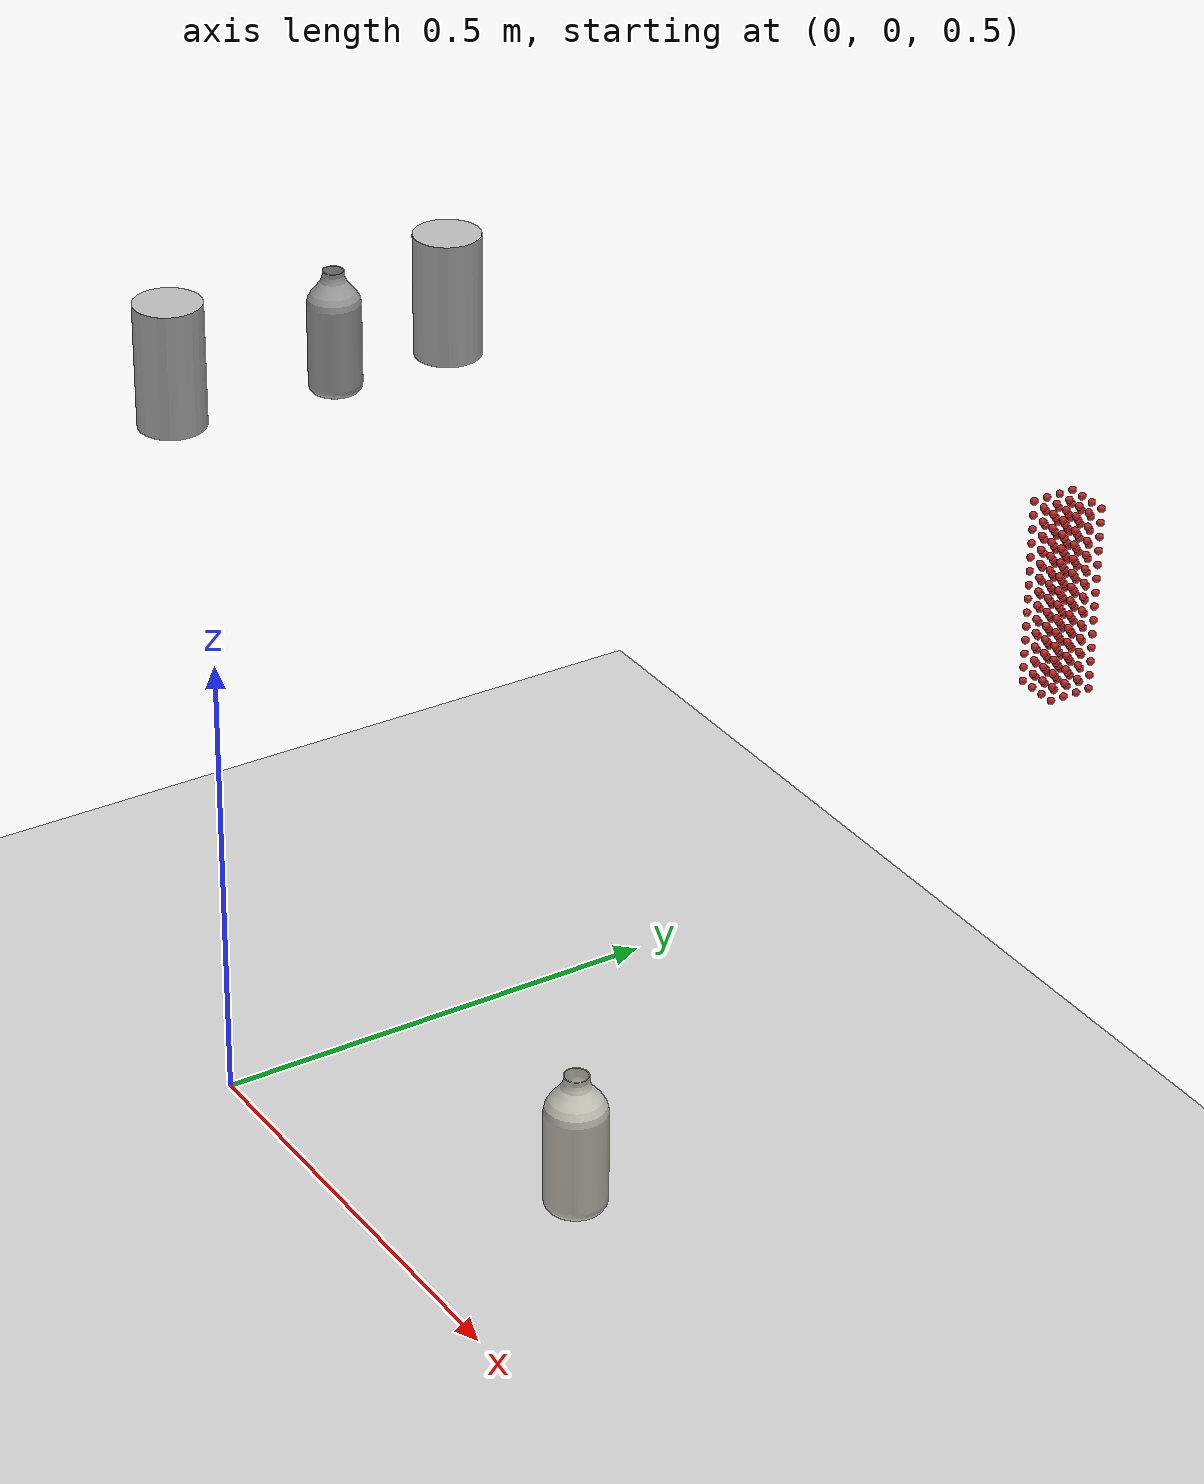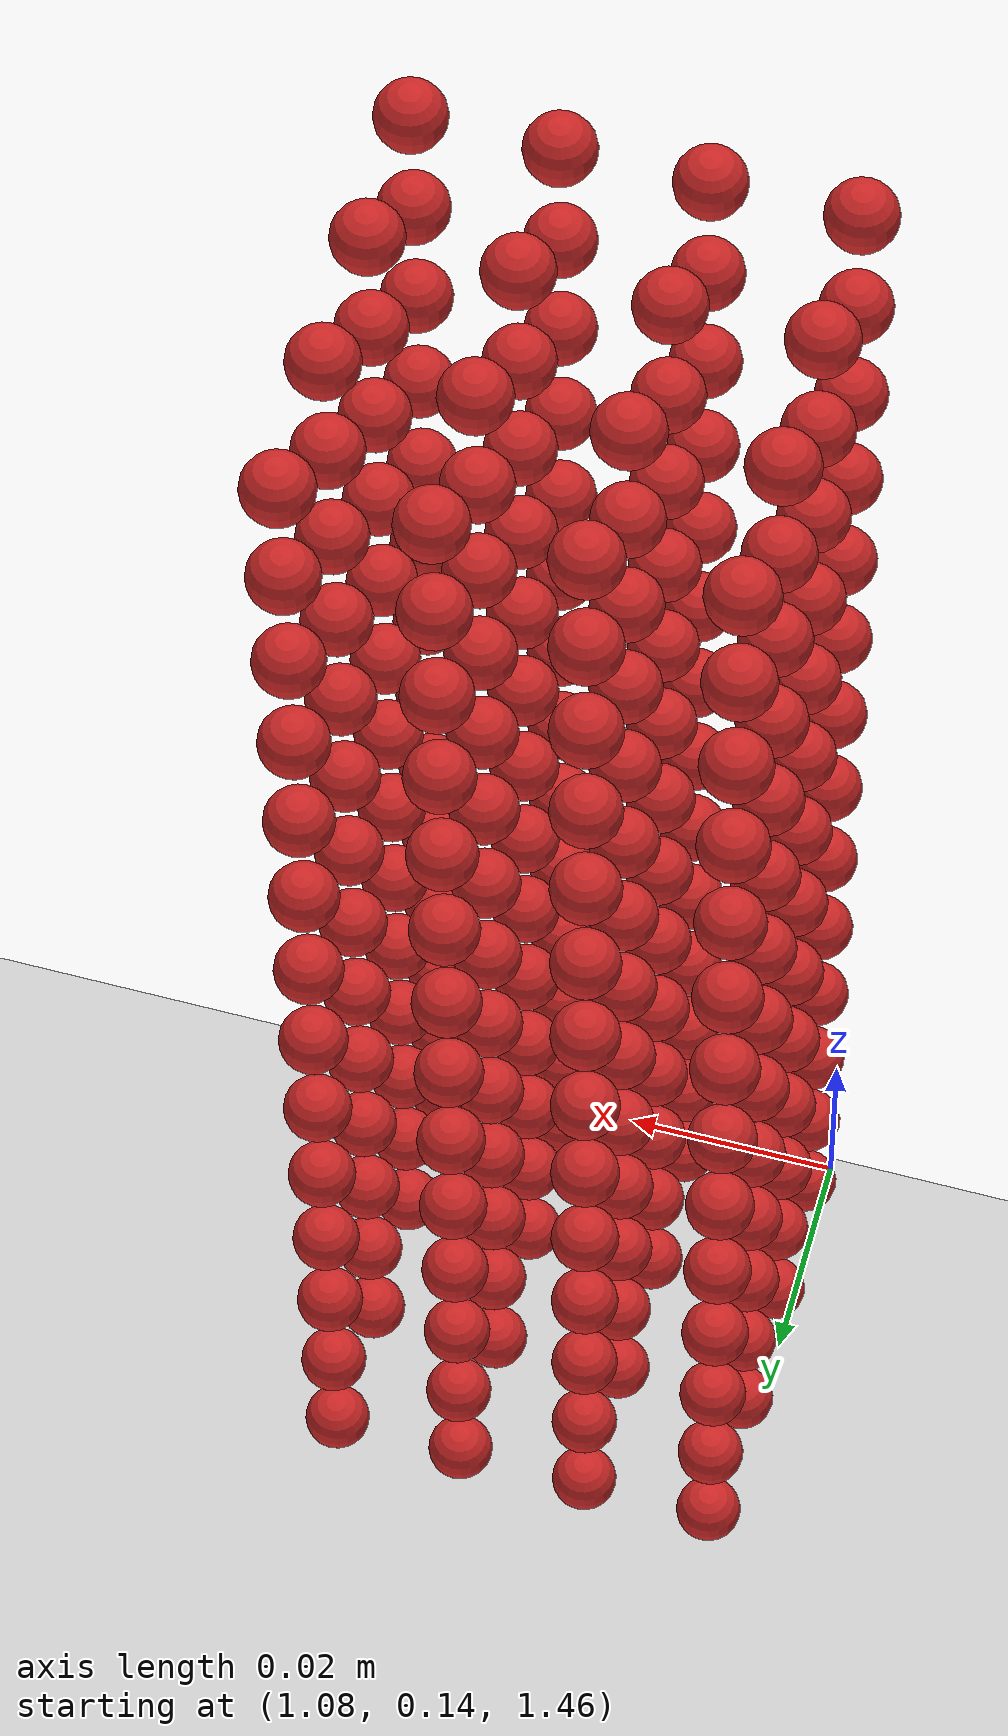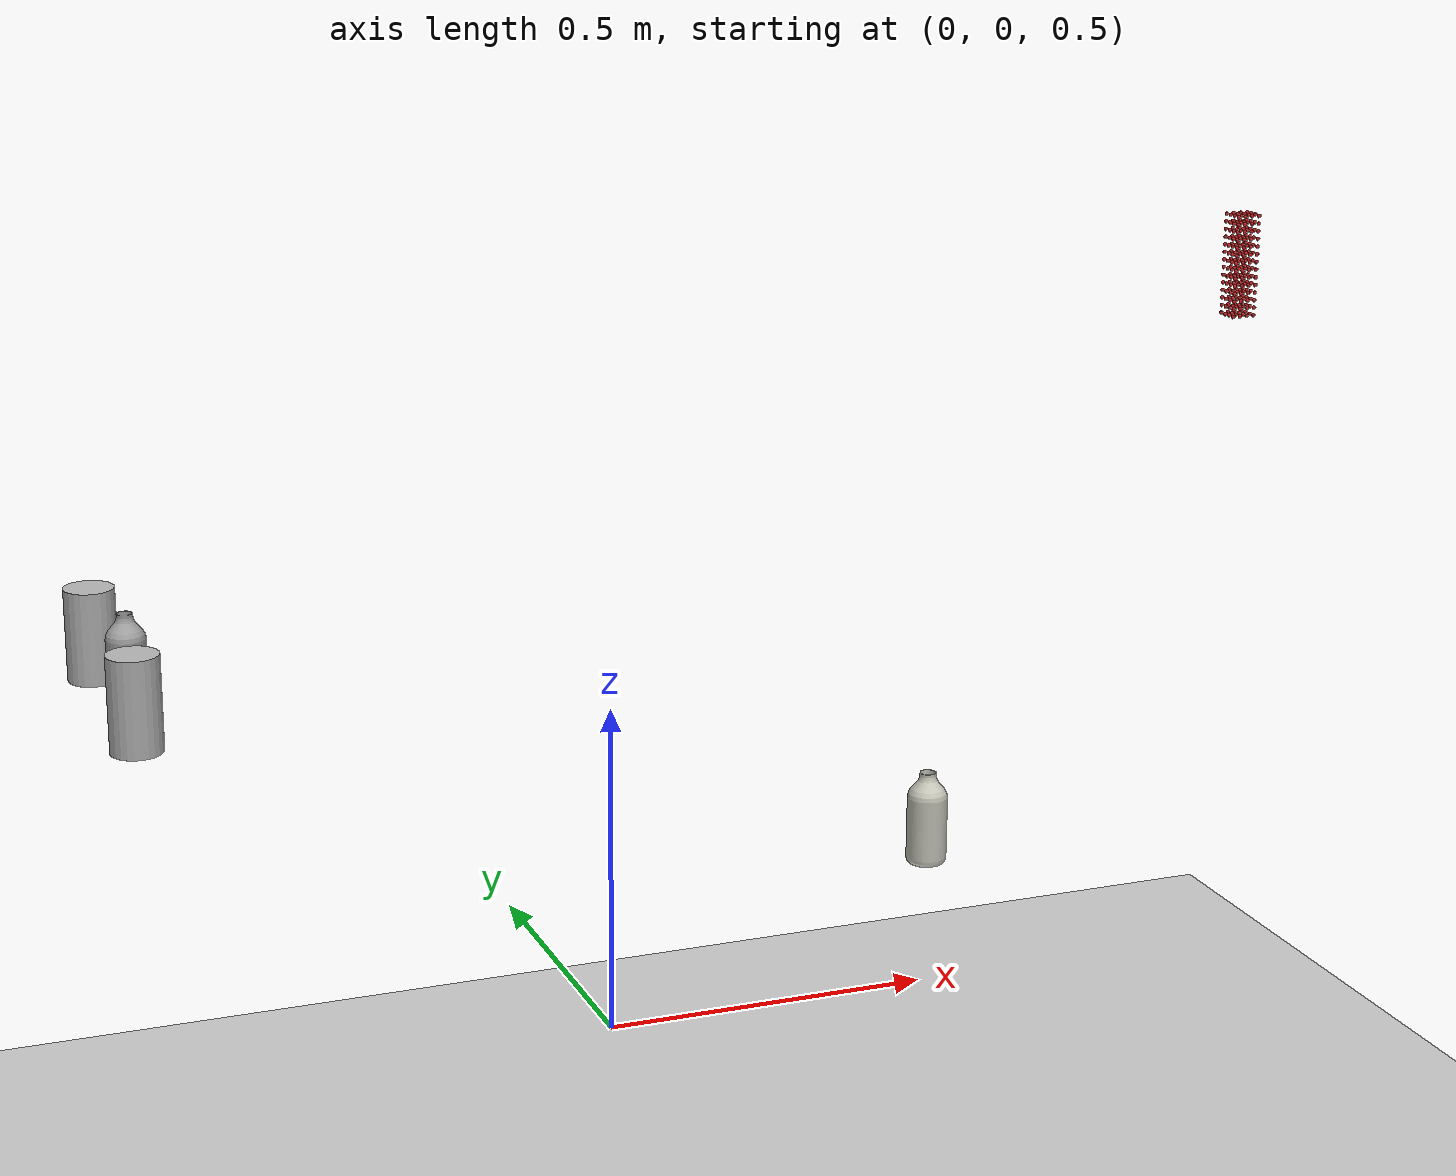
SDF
<sdf version="1.4">
 <world name="default">
  <physics type="ode">
   <gravity>0 0 -9.81</gravity>
   <ode>
    <solver><type>quick</type><iters>20</iters><sor>1</sor></solver>
    <constraints>
     <cfm>0</cfm>
     <erp>0.2</erp>
     <contact_max_correcting_vel>100</contact_max_correcting_vel>
     <contact_surface_layer>0</contact_surface_layer>
    </constraints>
   </ode>
   <real_time_update_rate>1000</real_time_update_rate>
   <max_step_size>0.001</max_step_size>
   <real_time_factor>1</real_time_factor>
  </physics>
  <light name="sun" type="directional">
   <pose>0 0 10 0 -0 0</pose>
   <diffuse>0.8 0.8 0.8 1</diffuse>
   <specular>0.2 0.2 0.2 1</specular>
   <attenuation>
    <range>1000</range>
    <constant>0.9</constant>
    <linear>0.01</linear>
    <quadratic>0.001</quadratic>
   </attenuation>
   <direction>-0.5 0.1 -0.9</direction>
  </light>
  <model name="ground_plane">
   <static>1</static>
   <link name="link">
    <collision name="collision">
     <geometry><plane><normal>0 0 1</normal><size>100 100</size></plane></geometry>
     <surface><friction><ode><mu>100</mu><mu2>50</mu2></ode></friction></surface>
    </collision>
    <visual name="visual">
     <cast_shadows>0</cast_shadows>
     <geometry><plane><normal>0 0 1</normal><size>100 100</size></plane></geometry>
     <material>
      <script><uri>file://media/materials/scripts/gazebo.material</uri><name>Gazebo/Grey</name></script>
     </material>
    </visual>
    <velocity_decay><linear>0</linear><angular>0</angular></velocity_decay>
   </link>
  </model>
  <scene><ambient>0.4 0.4 0.4 1</ambient><background>0.7 0.7 0.7 1</background><shadows>1</shadows></scene>
  <spherical_coordinates>
   <surface_model>EARTH_WGS84</surface_model>
   <latitude_deg>0</latitude_deg>
   <longitude_deg>0</longitude_deg>
   <elevation>0</elevation>
   <heading_deg>0</heading_deg>
  </spherical_coordinates>
  <model name="milk_bottle">
   <static>0</static>
   <link name="link">
    <inertial>
     <mass>0.05</mass>
     <inertia>
      <ixx>5.2083e-05</ixx>
      <ixy>0</ixy>
      <ixz>0</ixz>
      <iyy>5.2083e-05</iyy>
      <iyz>0</iyz>
      <izz>1e-06</izz>
     </inertia>
    </inertial>
    <collision name="colision1">
     <geometry>
      <mesh><uri>model://milk_bottle/meshes/milk_bottle.dae</uri><scale>0.7 0.7 0.7</scale></mesh>
     </geometry>
    </collision>
    <visual name="visual1">
     <geometry>
      <mesh><uri>model://milk_bottle/meshes/milk_bottle.dae</uri><scale>0.7 0.7 0.7</scale></mesh>
     </geometry>
     <material>
      <script><uri>file://media/materials/scripts/gazebo.material</uri><name>Gazebo/PaintedWall</name></script>
     </material>
    </visual>
    <velocity_decay><linear>0</linear><angular>0</angular></velocity_decay>
   </link>
   <pose>0.546545 0.079517 0.724885 0.000166 -7.3e-05 2.15699</pose>
  </model>
  <model name="milk_bottle_0">
   <static>0</static>
   <link name="link">
    <inertial>
     <mass>0.05</mass>
     <inertia>
      <ixx>5.2083e-05</ixx>
      <ixy>0</ixy>
      <ixz>0</ixz>
      <iyy>5.2083e-05</iyy>
      <iyz>0</iyz>
      <izz>1e-06</izz>
     </inertia>
    </inertial>
    <collision name="collision">
     <geometry><box><size>0.06 0.06 0.14</size></box></geometry>
     <surface>
      <friction><ode><mu>100</mu><mu2>50</mu2><fdir1>1 1 0</fdir1></ode></friction>
      <contact><ode><kp>2.14748e+11</kp><kd>0.1</kd></ode></contact>
     </surface>
    </collision>
    <visual name="visual1">
     <geometry>
      <mesh><uri>model://milk_bottle/meshes/milk_bottle.dae</uri><scale>0.7 0.7 0.7</scale></mesh>
     </geometry>
    </visual>
    <velocity_decay><linear>0</linear><angular>0</angular></velocity_decay>
   </link>
   <pose>-0.609663 0.476733 0.99 5e-06 -1e-06 -0.002362</pose>
  </model>
  <model name="cocacola">
   <static>0</static>
   <link name="link">
    <inertial>
     <mass>0.25</mass>
     <inertia><ixx>0</ixx><ixy>0</ixy><ixz>0</ixz><iyy>0</iyy><iyz>0</iyz><izz>0</izz></inertia>
    </inertial>
    <collision name="collision">
     <pose>0 0 0.075 -3.14159 -0 0</pose>
     <geometry><cylinder><radius>0.04</radius><length>0.15</length></cylinder></geometry>
    </collision>
    <visual name="visual">
     <pose>0 0 0.075 -3.14159 -0 0</pose>
     <geometry><cylinder><radius>0.04</radius><length>0.15</length></cylinder></geometry>
     <material>
      <script>
       <uri>model://cocacola/material/scripts</uri>
       <uri>model://cocacola/material/textures</uri>
       <name>Custom/cocacola</name>
      </script>
     </material>
    </visual>
    <velocity_decay><linear>0</linear><angular>0</angular></velocity_decay>
   </link>
   <pose>-0.635135 0.281961 0.920003 4.4e-05 -0.000314 -0.00223</pose>
  </model>
  <model name="sprite">
   <static>0</static>
   <link name="link">
    <inertial>
     <mass>0.25</mass>
     <inertia><ixx>0</ixx><ixy>0</ixy><ixz>0</ixz><iyy>0</iyy><iyz>0</iyz><izz>0</izz></inertia>
    </inertial>
    <collision name="collision">
     <pose>0 0 0.075 -3.14159 -0 0</pose>
     <geometry><cylinder><radius>0.04</radius><length>0.15</length></cylinder></geometry>
    </collision>
    <visual name="visual">
     <pose>0 0 0.075 -3.14159 -0 0</pose>
     <geometry><cylinder><radius>0.04</radius><length>0.15</length></cylinder></geometry>
     <material>
      <script>
       <uri>model://sprite/material/scripts</uri>
       <uri>model://sprite/material/textures</uri>
       <name>Custom/sprite</name>
      </script>
     </material>
    </visual>
    <velocity_decay><linear>0</linear><angular>0</angular></velocity_decay>
   </link>
   <pose>-0.633912 0.639664 0.919999 0.000205 -6.7e-05 0.020234</pose>
  </model>
  <model name="sphere0">
   <pose>0.546545 0.079517 0.734885 0 0 0</pose>
   <link name="link">
    <pose>0.534545 0.067517 0.734885 0 0 0</pose>
    <inertial>
     <mass>0.001</mass>
     <inertia>
      <ixx>0.004</ixx>
      <ixy>0.000000</ixy>
      <ixz>0.000000</ixz>
      <iyy>0.004</iyy>
      <iyz>0.000000</iyz>
      <izz>0.004</izz>
     </inertia>
    </inertial>
    <collision name="collision">
     <surface>
      <contact><ode><kp>10000000000.000000</kp><kd>1</kd></ode></contact>
      <friction><ode><mu>0.01</mu><mu2>0.01</mu2></ode></friction>
     </surface>
     <geometry><sphere><radius>0.003</radius></sphere></geometry>
    </collision>
    <visual name="visual">
     <geometry><sphere><radius>0.003</radius></sphere></geometry>
     <material>
      <script><uri>file://media/materials/scripts/gazebo.material</uri><name>Gazebo/Red</name></script>
     </material>
    </visual>
   </link>
  </model>
  <model name="sphere1">
   <pose>0.552545 0.079517 0.734885 0 0 0</pose>
   <link name="link">
    <pose>0.540545 0.067517 0.734885 0 0 0</pose>
    <inertial>
     <mass>0.001</mass>
     <inertia>
      <ixx>0.004</ixx>
      <ixy>0.000000</ixy>
      <ixz>0.000000</ixz>
      <iyy>0.004</iyy>
      <iyz>0.000000</iyz>
      <izz>0.004</izz>
     </inertia>
    </inertial>
    <collision name="collision">
     <surface>
      <contact><ode><kp>10000000000.000000</kp><kd>1</kd></ode></contact>
      <friction><ode><mu>0.01</mu><mu2>0.01</mu2></ode></friction>
     </surface>
     <geometry><sphere><radius>0.003</radius></sphere></geometry>
    </collision>
    <visual name="visual">
     <geometry><sphere><radius>0.003</radius></sphere></geometry>
     <material>
      <script><uri>file://media/materials/scripts/gazebo.material</uri><name>Gazebo/Red</name></script>
     </material>
    </visual>
   </link>
  </model>
  <model name="sphere2">
   <pose>0.558545 0.079517 0.734885 0 0 0</pose>
   <link name="link">
    <pose>0.546545 0.067517 0.734885 0 0 0</pose>
    <inertial>
     <mass>0.001</mass>
     <inertia>
      <ixx>0.004</ixx>
      <ixy>0.000000</ixy>
      <ixz>0.000000</ixz>
      <iyy>0.004</iyy>
      <iyz>0.000000</iyz>
      <izz>0.004</izz>
     </inertia>
    </inertial>
    <collision name="collision">
     <surface>
      <contact><ode><kp>10000000000.000000</kp><kd>1</kd></ode></contact>
      <friction><ode><mu>0.01</mu><mu2>0.01</mu2></ode></friction>
     </surface>
     <geometry><sphere><radius>0.003</radius></sphere></geometry>
    </collision>
    <visual name="visual">
     <geometry><sphere><radius>0.003</radius></sphere></geometry>
     <material>
      <script><uri>file://media/materials/scripts/gazebo.material</uri><name>Gazebo/Red</name></script>
     </material>
    </visual>
   </link>
  </model>
  <model name="sphere3">
   <pose>0.564545 0.079517 0.734885 0 0 0</pose>
   <link name="link">
    <pose>0.552545 0.067517 0.734885 0 0 0</pose>
    <inertial>
     <mass>0.001</mass>
     <inertia>
      <ixx>0.004</ixx>
      <ixy>0.000000</ixy>
      <ixz>0.000000</ixz>
      <iyy>0.004</iyy>
      <iyz>0.000000</iyz>
      <izz>0.004</izz>
     </inertia>
    </inertial>
    <collision name="collision">
     <surface>
      <contact><ode><kp>10000000000.000000</kp><kd>1</kd></ode></contact>
      <friction><ode><mu>0.01</mu><mu2>0.01</mu2></ode></friction>
     </surface>
     <geometry><sphere><radius>0.003</radius></sphere></geometry>
    </collision>
    <visual name="visual">
     <geometry><sphere><radius>0.003</radius></sphere></geometry>
     <material>
      <script><uri>file://media/materials/scripts/gazebo.material</uri><name>Gazebo/Red</name></script>
     </material>
    </visual>
   </link>
  </model>
  <model name="sphere4">
   <pose>0.546545 0.085517 0.734885 0 0 0</pose>
   <link name="link">
    <pose>0.534545 0.073517 0.734885 0 0 0</pose>
    <inertial>
     <mass>0.001</mass>
     <inertia>
      <ixx>0.004</ixx>
      <ixy>0.000000</ixy>
      <ixz>0.000000</ixz>
      <iyy>0.004</iyy>
      <iyz>0.000000</iyz>
      <izz>0.004</izz>
     </inertia>
    </inertial>
    <collision name="collision">
     <surface>
      <contact><ode><kp>10000000000.000000</kp><kd>1</kd></ode></contact>
      <friction><ode><mu>0.01</mu><mu2>0.01</mu2></ode></friction>
     </surface>
     <geometry><sphere><radius>0.003</radius></sphere></geometry>
    </collision>
    <visual name="visual">
     <geometry><sphere><radius>0.003</radius></sphere></geometry>
     <material>
      <script><uri>file://media/materials/scripts/gazebo.material</uri><name>Gazebo/Red</name></script>
     </material>
    </visual>
   </link>
  </model>
  <model name="sphere5">
   <pose>0.552545 0.085517 0.734885 0 0 0</pose>
   <link name="link">
    <pose>0.540545 0.073517 0.734885 0 0 0</pose>
    <inertial>
     <mass>0.001</mass>
     <inertia>
      <ixx>0.004</ixx>
      <ixy>0.000000</ixy>
      <ixz>0.000000</ixz>
      <iyy>0.004</iyy>
      <iyz>0.000000</iyz>
      <izz>0.004</izz>
     </inertia>
    </inertial>
    <collision name="collision">
     <surface>
      <contact><ode><kp>10000000000.000000</kp><kd>1</kd></ode></contact>
      <friction><ode><mu>0.01</mu><mu2>0.01</mu2></ode></friction>
     </surface>
     <geometry><sphere><radius>0.003</radius></sphere></geometry>
    </collision>
    <visual name="visual">
     <geometry><sphere><radius>0.003</radius></sphere></geometry>
     <material>
      <script><uri>file://media/materials/scripts/gazebo.material</uri><name>Gazebo/Red</name></script>
     </material>
    </visual>
   </link>
  </model>
  <model name="sphere6">
   <pose>0.558545 0.085517 0.734885 0 0 0</pose>
   <link name="link">
    <pose>0.546545 0.073517 0.734885 0 0 0</pose>
    <inertial>
     <mass>0.001</mass>
     <inertia>
      <ixx>0.004</ixx>
      <ixy>0.000000</ixy>
      <ixz>0.000000</ixz>
      <iyy>0.004</iyy>
      <iyz>0.000000</iyz>
      <izz>0.004</izz>
     </inertia>
    </inertial>
    <collision name="collision">
     <surface>
      <contact><ode><kp>10000000000.000000</kp><kd>1</kd></ode></contact>
      <friction><ode><mu>0.01</mu><mu2>0.01</mu2></ode></friction>
     </surface>
     <geometry><sphere><radius>0.003</radius></sphere></geometry>
    </collision>
    <visual name="visual">
     <geometry><sphere><radius>0.003</radius></sphere></geometry>
     <material>
      <script><uri>file://media/materials/scripts/gazebo.material</uri><name>Gazebo/Red</name></script>
     </material>
    </visual>
   </link>
  </model>
  <model name="sphere7">
   <pose>0.564545 0.085517 0.734885 0 0 0</pose>
   <link name="link">
    <pose>0.552545 0.073517 0.734885 0 0 0</pose>
    <inertial>
     <mass>0.001</mass>
     <inertia>
      <ixx>0.004</ixx>
      <ixy>0.000000</ixy>
      <ixz>0.000000</ixz>
      <iyy>0.004</iyy>
      <iyz>0.000000</iyz>
      <izz>0.004</izz>
     </inertia>
    </inertial>
    <collision name="collision">
     <surface>
      <contact><ode><kp>10000000000.000000</kp><kd>1</kd></ode></contact>
      <friction><ode><mu>0.01</mu><mu2>0.01</mu2></ode></friction>
     </surface>
     <geometry><sphere><radius>0.003</radius></sphere></geometry>
    </collision>
    <visual name="visual">
     <geometry><sphere><radius>0.003</radius></sphere></geometry>
     <material>
      <script><uri>file://media/materials/scripts/gazebo.material</uri><name>Gazebo/Red</name></script>
     </material>
    </visual>
   </link>
  </model>
  <model name="sphere8">
   <pose>0.546545 0.091517 0.734885 0 0 0</pose>
   <link name="link">
    <pose>0.534545 0.079517 0.734885 0 0 0</pose>
    <inertial>
     <mass>0.001</mass>
     <inertia>
      <ixx>0.004</ixx>
      <ixy>0.000000</ixy>
      <ixz>0.000000</ixz>
      <iyy>0.004</iyy>
      <iyz>0.000000</iyz>
      <izz>0.004</izz>
     </inertia>
    </inertial>
    <collision name="collision">
     <surface>
      <contact><ode><kp>10000000000.000000</kp><kd>1</kd></ode></contact>
      <friction><ode><mu>0.01</mu><mu2>0.01</mu2></ode></friction>
     </surface>
     <geometry><sphere><radius>0.003</radius></sphere></geometry>
    </collision>
    <visual name="visual">
     <geometry><sphere><radius>0.003</radius></sphere></geometry>
     <material>
      <script><uri>file://media/materials/scripts/gazebo.material</uri><name>Gazebo/Red</name></script>
     </material>
    </visual>
   </link>
  </model>
  <model name="sphere9">
   <pose>0.552545 0.091517 0.734885 0 0 0</pose>
   <link name="link">
    <pose>0.540545 0.079517 0.734885 0 0 0</pose>
    <inertial>
     <mass>0.001</mass>
     <inertia>
      <ixx>0.004</ixx>
      <ixy>0.000000</ixy>
      <ixz>0.000000</ixz>
      <iyy>0.004</iyy>
      <iyz>0.000000</iyz>
      <izz>0.004</izz>
     </inertia>
    </inertial>
    <collision name="collision">
     <surface>
      <contact><ode><kp>10000000000.000000</kp><kd>1</kd></ode></contact>
      <friction><ode><mu>0.01</mu><mu2>0.01</mu2></ode></friction>
     </surface>
     <geometry><sphere><radius>0.003</radius></sphere></geometry>
    </collision>
    <visual name="visual">
     <geometry><sphere><radius>0.003</radius></sphere></geometry>
     <material>
      <script><uri>file://media/materials/scripts/gazebo.material</uri><name>Gazebo/Red</name></script>
     </material>
    </visual>
   </link>
  </model>
  <model name="sphere10">
   <pose>0.558545 0.091517 0.734885 0 0 0</pose>
   <link name="link">
    <pose>0.546545 0.079517 0.734885 0 0 0</pose>
    <inertial>
     <mass>0.001</mass>
     <inertia>
      <ixx>0.004</ixx>
      <ixy>0.000000</ixy>
      <ixz>0.000000</ixz>
      <iyy>0.004</iyy>
      <iyz>0.000000</iyz>
      <izz>0.004</izz>
     </inertia>
    </inertial>
    <collision name="collision">
     <surface>
      <contact><ode><kp>10000000000.000000</kp><kd>1</kd></ode></contact>
      <friction><ode><mu>0.01</mu><mu2>0.01</mu2></ode></friction>
     </surface>
     <geometry><sphere><radius>0.003</radius></sphere></geometry>
    </collision>
    <visual name="visual">
     <geometry><sphere><radius>0.003</radius></sphere></geometry>
     <material>
      <script><uri>file://media/materials/scripts/gazebo.material</uri><name>Gazebo/Red</name></script>
     </material>
    </visual>
   </link>
  </model>
  <model name="sphere11">
   <pose>0.564545 0.091517 0.734885 0 0 0</pose>
   <link name="link">
    <pose>0.552545 0.079517 0.734885 0 0 0</pose>
    <inertial>
     <mass>0.001</mass>
     <inertia>
      <ixx>0.004</ixx>
      <ixy>0.000000</ixy>
      <ixz>0.000000</ixz>
      <iyy>0.004</iyy>
      <iyz>0.000000</iyz>
      <izz>0.004</izz>
     </inertia>
    </inertial>
    <collision name="collision">
     <surface>
      <contact><ode><kp>10000000000.000000</kp><kd>1</kd></ode></contact>
      <friction><ode><mu>0.01</mu><mu2>0.01</mu2></ode></friction>
     </surface>
     <geometry><sphere><radius>0.003</radius></sphere></geometry>
    </collision>
    <visual name="visual">
     <geometry><sphere><radius>0.003</radius></sphere></geometry>
     <material>
      <script><uri>file://media/materials/scripts/gazebo.material</uri><name>Gazebo/Red</name></script>
     </material>
    </visual>
   </link>
  </model>
  <model name="sphere12">
   <pose>0.546545 0.097517 0.734885 0 0 0</pose>
   <link name="link">
    <pose>0.534545 0.085517 0.734885 0 0 0</pose>
    <inertial>
     <mass>0.001</mass>
     <inertia>
      <ixx>0.004</ixx>
      <ixy>0.000000</ixy>
      <ixz>0.000000</ixz>
      <iyy>0.004</iyy>
      <iyz>0.000000</iyz>
      <izz>0.004</izz>
     </inertia>
    </inertial>
    <collision name="collision">
     <surface>
      <contact><ode><kp>10000000000.000000</kp><kd>1</kd></ode></contact>
      <friction><ode><mu>0.01</mu><mu2>0.01</mu2></ode></friction>
     </surface>
     <geometry><sphere><radius>0.003</radius></sphere></geometry>
    </collision>
    <visual name="visual">
     <geometry><sphere><radius>0.003</radius></sphere></geometry>
     <material>
      <script><uri>file://media/materials/scripts/gazebo.material</uri><name>Gazebo/Red</name></script>
     </material>
    </visual>
   </link>
  </model>
  <model name="sphere13">
   <pose>0.552545 0.097517 0.734885 0 0 0</pose>
   <link name="link">
    <pose>0.540545 0.085517 0.734885 0 0 0</pose>
    <inertial>
     <mass>0.001</mass>
     <inertia>
      <ixx>0.004</ixx>
      <ixy>0.000000</ixy>
      <ixz>0.000000</ixz>
      <iyy>0.004</iyy>
      <iyz>0.000000</iyz>
      <izz>0.004</izz>
     </inertia>
    </inertial>
    <collision name="collision">
     <surface>
      <contact><ode><kp>10000000000.000000</kp><kd>1</kd></ode></contact>
      <friction><ode><mu>0.01</mu><mu2>0.01</mu2></ode></friction>
     </surface>
     <geometry><sphere><radius>0.003</radius></sphere></geometry>
    </collision>
    <visual name="visual">
     <geometry><sphere><radius>0.003</radius></sphere></geometry>
     <material>
      <script><uri>file://media/materials/scripts/gazebo.material</uri><name>Gazebo/Red</name></script>
     </material>
    </visual>
   </link>
  </model>
  <model name="sphere14">
   <pose>0.558545 0.097517 0.734885 0 0 0</pose>
   <link name="link">
    <pose>0.546545 0.085517 0.734885 0 0 0</pose>
    <inertial>
     <mass>0.001</mass>
     <inertia>
      <ixx>0.004</ixx>
      <ixy>0.000000</ixy>
      <ixz>0.000000</ixz>
      <iyy>0.004</iyy>
      <iyz>0.000000</iyz>
      <izz>0.004</izz>
     </inertia>
    </inertial>
    <collision name="collision">
     <surface>
      <contact><ode><kp>10000000000.000000</kp><kd>1</kd></ode></contact>
      <friction><ode><mu>0.01</mu><mu2>0.01</mu2></ode></friction>
     </surface>
     <geometry><sphere><radius>0.003</radius></sphere></geometry>
    </collision>
    <visual name="visual">
     <geometry><sphere><radius>0.003</radius></sphere></geometry>
     <material>
      <script><uri>file://media/materials/scripts/gazebo.material</uri><name>Gazebo/Red</name></script>
     </material>
    </visual>
   </link>
  </model>
  <model name="sphere15">
   <pose>0.564545 0.097517 0.734885 0 0 0</pose>
   <link name="link">
    <pose>0.552545 0.085517 0.734885 0 0 0</pose>
    <inertial>
     <mass>0.001</mass>
     <inertia>
      <ixx>0.004</ixx>
      <ixy>0.000000</ixy>
      <ixz>0.000000</ixz>
      <iyy>0.004</iyy>
      <iyz>0.000000</iyz>
      <izz>0.004</izz>
     </inertia>
    </inertial>
    <collision name="collision">
     <surface>
      <contact><ode><kp>10000000000.000000</kp><kd>1</kd></ode></contact>
      <friction><ode><mu>0.01</mu><mu2>0.01</mu2></ode></friction>
     </surface>
     <geometry><sphere><radius>0.003</radius></sphere></geometry>
    </collision>
    <visual name="visual">
     <geometry><sphere><radius>0.003</radius></sphere></geometry>
     <material>
      <script><uri>file://media/materials/scripts/gazebo.material</uri><name>Gazebo/Red</name></script>
     </material>
    </visual>
   </link>
  </model>
  <model name="sphere16">
   <pose>0.546545 0.079517 0.740885 0 0 0</pose>
   <link name="link">
    <pose>0.534545 0.067517 0.740885 0 0 0</pose>
    <inertial>
     <mass>0.001</mass>
     <inertia>
      <ixx>0.004</ixx>
      <ixy>0.000000</ixy>
      <ixz>0.000000</ixz>
      <iyy>0.004</iyy>
      <iyz>0.000000</iyz>
      <izz>0.004</izz>
     </inertia>
    </inertial>
    <collision name="collision">
     <surface>
      <contact><ode><kp>10000000000.000000</kp><kd>1</kd></ode></contact>
      <friction><ode><mu>0.01</mu><mu2>0.01</mu2></ode></friction>
     </surface>
     <geometry><sphere><radius>0.003</radius></sphere></geometry>
    </collision>
    <visual name="visual">
     <geometry><sphere><radius>0.003</radius></sphere></geometry>
     <material>
      <script><uri>file://media/materials/scripts/gazebo.material</uri><name>Gazebo/Red</name></script>
     </material>
    </visual>
   </link>
  </model>
  <model name="sphere17">
   <pose>0.552545 0.079517 0.740885 0 0 0</pose>
   <link name="link">
    <pose>0.540545 0.067517 0.740885 0 0 0</pose>
    <inertial>
     <mass>0.001</mass>
     <inertia>
      <ixx>0.004</ixx>
      <ixy>0.000000</ixy>
      <ixz>0.000000</ixz>
      <iyy>0.004</iyy>
      <iyz>0.000000</iyz>
      <izz>0.004</izz>
     </inertia>
    </inertial>
    <collision name="collision">
     <surface>
      <contact><ode><kp>10000000000.000000</kp><kd>1</kd></ode></contact>
      <friction><ode><mu>0.01</mu><mu2>0.01</mu2></ode></friction>
     </surface>
     <geometry><sphere><radius>0.003</radius></sphere></geometry>
    </collision>
    <visual name="visual">
     <geometry><sphere><radius>0.003</radius></sphere></geometry>
     <material>
      <script><uri>file://media/materials/scripts/gazebo.material</uri><name>Gazebo/Red</name></script>
     </material>
    </visual>
   </link>
  </model>
  <model name="sphere18">
   <pose>0.558545 0.079517 0.740885 0 0 0</pose>
   <link name="link">
    <pose>0.546545 0.067517 0.740885 0 0 0</pose>
    <inertial>
     <mass>0.001</mass>
     <inertia>
      <ixx>0.004</ixx>
      <ixy>0.000000</ixy>
      <ixz>0.000000</ixz>
      <iyy>0.004</iyy>
      <iyz>0.000000</iyz>
      <izz>0.004</izz>
     </inertia>
    </inertial>
    <collision name="collision">
     <surface>
      <contact><ode><kp>10000000000.000000</kp><kd>1</kd></ode></contact>
      <friction><ode><mu>0.01</mu><mu2>0.01</mu2></ode></friction>
     </surface>
     <geometry><sphere><radius>0.003</radius></sphere></geometry>
    </collision>
    <visual name="visual">
     <geometry><sphere><radius>0.003</radius></sphere></geometry>
     <material>
      <script><uri>file://media/materials/scripts/gazebo.material</uri><name>Gazebo/Red</name></script>
     </material>
    </visual>
   </link>
  </model>
  <model name="sphere19">
   <pose>0.564545 0.079517 0.740885 0 0 0</pose>
   <link name="link">
    <pose>0.552545 0.067517 0.740885 0 0 0</pose>
    <inertial>
     <mass>0.001</mass>
     <inertia>
      <ixx>0.004</ixx>
      <ixy>0.000000</ixy>
      <ixz>0.000000</ixz>
      <iyy>0.004</iyy>
      <iyz>0.000000</iyz>
      <izz>0.004</izz>
     </inertia>
    </inertial>
    <collision name="collision">
     <surface>
      <contact><ode><kp>10000000000.000000</kp><kd>1</kd></ode></contact>
      <friction><ode><mu>0.01</mu><mu2>0.01</mu2></ode></friction>
     </surface>
     <geometry><sphere><radius>0.003</radius></sphere></geometry>
    </collision>
    <visual name="visual">
     <geometry><sphere><radius>0.003</radius></sphere></geometry>
     <material>
      <script><uri>file://media/materials/scripts/gazebo.material</uri><name>Gazebo/Red</name></script>
     </material>
    </visual>
   </link>
  </model>
  <model name="sphere20">
   <pose>0.546545 0.085517 0.740885 0 0 0</pose>
   <link name="link">
    <pose>0.534545 0.073517 0.740885 0 0 0</pose>
    <inertial>
     <mass>0.001</mass>
     <inertia>
      <ixx>0.004</ixx>
      <ixy>0.000000</ixy>
      <ixz>0.000000</ixz>
      <iyy>0.004</iyy>
      <iyz>0.000000</iyz>
      <izz>0.004</izz>
     </inertia>
    </inertial>
    <collision name="collision">
     <surface>
      <contact><ode><kp>10000000000.000000</kp><kd>1</kd></ode></contact>
      <friction><ode><mu>0.01</mu><mu2>0.01</mu2></ode></friction>
     </surface>
     <geometry><sphere><radius>0.003</radius></sphere></geometry>
    </collision>
    <visual name="visual">
     <geometry><sphere><radius>0.003</radius></sphere></geometry>
     <material>
      <script><uri>file://media/materials/scripts/gazebo.material</uri><name>Gazebo/Red</name></script>
     </material>
    </visual>
   </link>
  </model>
  <model name="sphere21">
   <pose>0.552545 0.085517 0.740885 0 0 0</pose>
   <link name="link">
    <pose>0.540545 0.073517 0.740885 0 0 0</pose>
    <inertial>
     <mass>0.001</mass>
     <inertia>
      <ixx>0.004</ixx>
      <ixy>0.000000</ixy>
      <ixz>0.000000</ixz>
      <iyy>0.004</iyy>
      <iyz>0.000000</iyz>
      <izz>0.004</izz>
     </inertia>
    </inertial>
    <collision name="collision">
     <surface>
      <contact><ode><kp>10000000000.000000</kp><kd>1</kd></ode></contact>
      <friction><ode><mu>0.01</mu><mu2>0.01</mu2></ode></friction>
     </surface>
     <geometry><sphere><radius>0.003</radius></sphere></geometry>
    </collision>
    <visual name="visual">
     <geometry><sphere><radius>0.003</radius></sphere></geometry>
     <material>
      <script><uri>file://media/materials/scripts/gazebo.material</uri><name>Gazebo/Red</name></script>
     </material>
    </visual>
   </link>
  </model>
  <model name="sphere22">
   <pose>0.558545 0.085517 0.740885 0 0 0</pose>
   <link name="link">
    <pose>0.546545 0.073517 0.740885 0 0 0</pose>
    <inertial>
     <mass>0.001</mass>
     <inertia>
      <ixx>0.004</ixx>
      <ixy>0.000000</ixy>
      <ixz>0.000000</ixz>
      <iyy>0.004</iyy>
      <iyz>0.000000</iyz>
      <izz>0.004</izz>
     </inertia>
    </inertial>
    <collision name="collision">
     <surface>
      <contact><ode><kp>10000000000.000000</kp><kd>1</kd></ode></contact>
      <friction><ode><mu>0.01</mu><mu2>0.01</mu2></ode></friction>
     </surface>
     <geometry><sphere><radius>0.003</radius></sphere></geometry>
    </collision>
    <visual name="visual">
     <geometry><sphere><radius>0.003</radius></sphere></geometry>
     <material>
      <script><uri>file://media/materials/scripts/gazebo.material</uri><name>Gazebo/Red</name></script>
     </material>
    </visual>
   </link>
  </model>
  <model name="sphere23">
   <pose>0.564545 0.085517 0.740885 0 0 0</pose>
   <link name="link">
    <pose>0.552545 0.073517 0.740885 0 0 0</pose>
    <inertial>
     <mass>0.001</mass>
     <inertia>
      <ixx>0.004</ixx>
      <ixy>0.000000</ixy>
      <ixz>0.000000</ixz>
      <iyy>0.004</iyy>
      <iyz>0.000000</iyz>
      <izz>0.004</izz>
     </inertia>
    </inertial>
    <collision name="collision">
     <surface>
      <contact><ode><kp>10000000000.000000</kp><kd>1</kd></ode></contact>
      <friction><ode><mu>0.01</mu><mu2>0.01</mu2></ode></friction>
     </surface>
     <geometry><sphere><radius>0.003</radius></sphere></geometry>
    </collision>
    <visual name="visual">
     <geometry><sphere><radius>0.003</radius></sphere></geometry>
     <material>
      <script><uri>file://media/materials/scripts/gazebo.material</uri><name>Gazebo/Red</name></script>
     </material>
    </visual>
   </link>
  </model>
  <model name="sphere24">
   <pose>0.546545 0.091517 0.740885 0 0 0</pose>
   <link name="link">
    <pose>0.534545 0.079517 0.740885 0 0 0</pose>
    <inertial>
     <mass>0.001</mass>
     <inertia>
      <ixx>0.004</ixx>
      <ixy>0.000000</ixy>
      <ixz>0.000000</ixz>
      <iyy>0.004</iyy>
      <iyz>0.000000</iyz>
      <izz>0.004</izz>
     </inertia>
    </inertial>
    <collision name="collision">
     <surface>
      <contact><ode><kp>10000000000.000000</kp><kd>1</kd></ode></contact>
      <friction><ode><mu>0.01</mu><mu2>0.01</mu2></ode></friction>
     </surface>
     <geometry><sphere><radius>0.003</radius></sphere></geometry>
    </collision>
    <visual name="visual">
     <geometry><sphere><radius>0.003</radius></sphere></geometry>
     <material>
      <script><uri>file://media/materials/scripts/gazebo.material</uri><name>Gazebo/Red</name></script>
     </material>
    </visual>
   </link>
  </model>
  <model name="sphere25">
   <pose>0.552545 0.091517 0.740885 0 0 0</pose>
   <link name="link">
    <pose>0.540545 0.079517 0.740885 0 0 0</pose>
    <inertial>
     <mass>0.001</mass>
     <inertia>
      <ixx>0.004</ixx>
      <ixy>0.000000</ixy>
      <ixz>0.000000</ixz>
      <iyy>0.004</iyy>
      <iyz>0.000000</iyz>
      <izz>0.004</izz>
     </inertia>
    </inertial>
    <collision name="collision">
     <surface>
      <contact><ode><kp>10000000000.000000</kp><kd>1</kd></ode></contact>
      <friction><ode><mu>0.01</mu><mu2>0.01</mu2></ode></friction>
     </surface>
     <geometry><sphere><radius>0.003</radius></sphere></geometry>
    </collision>
    <visual name="visual">
     <geometry><sphere><radius>0.003</radius></sphere></geometry>
     <material>
      <script><uri>file://media/materials/scripts/gazebo.material</uri><name>Gazebo/Red</name></script>
     </material>
    </visual>
   </link>
  </model>
  <model name="sphere26">
   <pose>0.558545 0.091517 0.740885 0 0 0</pose>
   <link name="link">
    <pose>0.546545 0.079517 0.740885 0 0 0</pose>
    <inertial>
     <mass>0.001</mass>
     <inertia>
      <ixx>0.004</ixx>
      <ixy>0.000000</ixy>
      <ixz>0.000000</ixz>
      <iyy>0.004</iyy>
      <iyz>0.000000</iyz>
      <izz>0.004</izz>
     </inertia>
    </inertial>
    <collision name="collision">
     <surface>
      <contact><ode><kp>10000000000.000000</kp><kd>1</kd></ode></contact>
      <friction><ode><mu>0.01</mu><mu2>0.01</mu2></ode></friction>
     </surface>
     <geometry><sphere><radius>0.003</radius></sphere></geometry>
    </collision>
    <visual name="visual">
     <geometry><sphere><radius>0.003</radius></sphere></geometry>
     <material>
      <script><uri>file://media/materials/scripts/gazebo.material</uri><name>Gazebo/Red</name></script>
     </material>
    </visual>
   </link>
  </model>
  <model name="sphere27">
   <pose>0.564545 0.091517 0.740885 0 0 0</pose>
   <link name="link">
    <pose>0.552545 0.079517 0.740885 0 0 0</pose>
    <inertial>
     <mass>0.001</mass>
     <inertia>
      <ixx>0.004</ixx>
      <ixy>0.000000</ixy>
      <ixz>0.000000</ixz>
      <iyy>0.004</iyy>
      <iyz>0.000000</iyz>
      <izz>0.004</izz>
     </inertia>
    </inertial>
    <collision name="collision">
     <surface>
      <contact><ode><kp>10000000000.000000</kp><kd>1</kd></ode></contact>
      <friction><ode><mu>0.01</mu><mu2>0.01</mu2></ode></friction>
     </surface>
     <geometry><sphere><radius>0.003</radius></sphere></geometry>
    </collision>
    <visual name="visual">
     <geometry><sphere><radius>0.003</radius></sphere></geometry>
     <material>
      <script><uri>file://media/materials/scripts/gazebo.material</uri><name>Gazebo/Red</name></script>
     </material>
    </visual>
   </link>
  </model>
  <model name="sphere28">
   <pose>0.546545 0.097517 0.740885 0 0 0</pose>
   <link name="link">
    <pose>0.534545 0.085517 0.740885 0 0 0</pose>
    <inertial>
     <mass>0.001</mass>
     <inertia>
      <ixx>0.004</ixx>
      <ixy>0.000000</ixy>
      <ixz>0.000000</ixz>
      <iyy>0.004</iyy>
      <iyz>0.000000</iyz>
      <izz>0.004</izz>
     </inertia>
    </inertial>
    <collision name="collision">
     <surface>
      <contact><ode><kp>10000000000.000000</kp><kd>1</kd></ode></contact>
      <friction><ode><mu>0.01</mu><mu2>0.01</mu2></ode></friction>
     </surface>
     <geometry><sphere><radius>0.003</radius></sphere></geometry>
    </collision>
    <visual name="visual">
     <geometry><sphere><radius>0.003</radius></sphere></geometry>
     <material>
      <script><uri>file://media/materials/scripts/gazebo.material</uri><name>Gazebo/Red</name></script>
     </material>
    </visual>
   </link>
  </model>
  <model name="sphere29">
   <pose>0.552545 0.097517 0.740885 0 0 0</pose>
   <link name="link">
    <pose>0.540545 0.085517 0.740885 0 0 0</pose>
    <inertial>
     <mass>0.001</mass>
     <inertia>
      <ixx>0.004</ixx>
      <ixy>0.000000</ixy>
      <ixz>0.000000</ixz>
      <iyy>0.004</iyy>
      <iyz>0.000000</iyz>
      <izz>0.004</izz>
     </inertia>
    </inertial>
    <collision name="collision">
     <surface>
      <contact><ode><kp>10000000000.000000</kp><kd>1</kd></ode></contact>
      <friction><ode><mu>0.01</mu><mu2>0.01</mu2></ode></friction>
     </surface>
     <geometry><sphere><radius>0.003</radius></sphere></geometry>
    </collision>
    <visual name="visual">
     <geometry><sphere><radius>0.003</radius></sphere></geometry>
     <material>
      <script><uri>file://media/materials/scripts/gazebo.material</uri><name>Gazebo/Red</name></script>
     </material>
    </visual>
   </link>
  </model>
  <model name="sphere30">
   <pose>0.558545 0.097517 0.740885 0 0 0</pose>
   <link name="link">
    <pose>0.546545 0.085517 0.740885 0 0 0</pose>
    <inertial>
     <mass>0.001</mass>
     <inertia>
      <ixx>0.004</ixx>
      <ixy>0.000000</ixy>
      <ixz>0.000000</ixz>
      <iyy>0.004</iyy>
      <iyz>0.000000</iyz>
      <izz>0.004</izz>
     </inertia>
    </inertial>
    <collision name="collision">
     <surface>
      <contact><ode><kp>10000000000.000000</kp><kd>1</kd></ode></contact>
      <friction><ode><mu>0.01</mu><mu2>0.01</mu2></ode></friction>
     </surface>
     <geometry><sphere><radius>0.003</radius></sphere></geometry>
    </collision>
    <visual name="visual">
     <geometry><sphere><radius>0.003</radius></sphere></geometry>
     <material>
      <script><uri>file://media/materials/scripts/gazebo.material</uri><name>Gazebo/Red</name></script>
     </material>
    </visual>
   </link>
  </model>
  <model name="sphere31">
   <pose>0.564545 0.097517 0.740885 0 0 0</pose>
   <link name="link">
    <pose>0.552545 0.085517 0.740885 0 0 0</pose>
    <inertial>
     <mass>0.001</mass>
     <inertia>
      <ixx>0.004</ixx>
      <ixy>0.000000</ixy>
      <ixz>0.000000</ixz>
      <iyy>0.004</iyy>
      <iyz>0.000000</iyz>
      <izz>0.004</izz>
     </inertia>
    </inertial>
    <collision name="collision">
     <surface>
      <contact><ode><kp>10000000000.000000</kp><kd>1</kd></ode></contact>
      <friction><ode><mu>0.01</mu><mu2>0.01</mu2></ode></friction>
     </surface>
     <geometry><sphere><radius>0.003</radius></sphere></geometry>
    </collision>
    <visual name="visual">
     <geometry><sphere><radius>0.003</radius></sphere></geometry>
     <material>
      <script><uri>file://media/materials/scripts/gazebo.material</uri><name>Gazebo/Red</name></script>
     </material>
    </visual>
   </link>
  </model>
  <model name="sphere32">
   <pose>0.546545 0.079517 0.746885 0 0 0</pose>
   <link name="link">
    <pose>0.534545 0.067517 0.746885 0 0 0</pose>
    <inertial>
     <mass>0.001</mass>
     <inertia>
      <ixx>0.004</ixx>
      <ixy>0.000000</ixy>
      <ixz>0.000000</ixz>
      <iyy>0.004</iyy>
      <iyz>0.000000</iyz>
      <izz>0.004</izz>
     </inertia>
    </inertial>
    <collision name="collision">
     <surface>
      <contact><ode><kp>10000000000.000000</kp><kd>1</kd></ode></contact>
      <friction><ode><mu>0.01</mu><mu2>0.01</mu2></ode></friction>
     </surface>
     <geometry><sphere><radius>0.003</radius></sphere></geometry>
    </collision>
    <visual name="visual">
     <geometry><sphere><radius>0.003</radius></sphere></geometry>
     <material>
      <script><uri>file://media/materials/scripts/gazebo.material</uri><name>Gazebo/Red</name></script>
     </material>
    </visual>
   </link>
  </model>
  <model name="sphere33">
   <pose>0.552545 0.079517 0.746885 0 0 0</pose>
   <link name="link">
    <pose>0.540545 0.067517 0.746885 0 0 0</pose>
    <inertial>
     <mass>0.001</mass>
     <inertia>
      <ixx>0.004</ixx>
      <ixy>0.000000</ixy>
      <ixz>0.000000</ixz>
      <iyy>0.004</iyy>
      <iyz>0.000000</iyz>
      <izz>0.004</izz>
     </inertia>
    </inertial>
    <collision name="collision">
     <surface>
      <contact><ode><kp>10000000000.000000</kp><kd>1</kd></ode></contact>
      <friction><ode><mu>0.01</mu><mu2>0.01</mu2></ode></friction>
     </surface>
     <geometry><sphere><radius>0.003</radius></sphere></geometry>
    </collision>
    <visual name="visual">
     <geometry><sphere><radius>0.003</radius></sphere></geometry>
     <material>
      <script><uri>file://media/materials/scripts/gazebo.material</uri><name>Gazebo/Red</name></script>
     </material>
    </visual>
   </link>
  </model>
  <model name="sphere34">
   <pose>0.558545 0.079517 0.746885 0 0 0</pose>
   <link name="link">
    <pose>0.546545 0.067517 0.746885 0 0 0</pose>
    <inertial>
     <mass>0.001</mass>
     <inertia>
      <ixx>0.004</ixx>
      <ixy>0.000000</ixy>
      <ixz>0.000000</ixz>
      <iyy>0.004</iyy>
      <iyz>0.000000</iyz>
      <izz>0.004</izz>
     </inertia>
    </inertial>
    <collision name="collision">
     <surface>
      <contact><ode><kp>10000000000.000000</kp><kd>1</kd></ode></contact>
      <friction><ode><mu>0.01</mu><mu2>0.01</mu2></ode></friction>
     </surface>
     <geometry><sphere><radius>0.003</radius></sphere></geometry>
    </collision>
    <visual name="visual">
     <geometry><sphere><radius>0.003</radius></sphere></geometry>
     <material>
      <script><uri>file://media/materials/scripts/gazebo.material</uri><name>Gazebo/Red</name></script>
     </material>
    </visual>
   </link>
  </model>
  <model name="sphere35">
   <pose>0.564545 0.079517 0.746885 0 0 0</pose>
   <link name="link">
    <pose>0.552545 0.067517 0.746885 0 0 0</pose>
    <inertial>
     <mass>0.001</mass>
     <inertia>
      <ixx>0.004</ixx>
      <ixy>0.000000</ixy>
      <ixz>0.000000</ixz>
      <iyy>0.004</iyy>
      <iyz>0.000000</iyz>
      <izz>0.004</izz>
     </inertia>
    </inertial>
    <collision name="collision">
     <surface>
      <contact><ode><kp>10000000000.000000</kp><kd>1</kd></ode></contact>
      <friction><ode><mu>0.01</mu><mu2>0.01</mu2></ode></friction>
     </surface>
     <geometry><sphere><radius>0.003</radius></sphere></geometry>
    </collision>
    <visual name="visual">
     <geometry><sphere><radius>0.003</radius></sphere></geometry>
     <material>
      <script><uri>file://media/materials/scripts/gazebo.material</uri><name>Gazebo/Red</name></script>
     </material>
    </visual>
   </link>
  </model>
  <model name="sphere36">
   <pose>0.546545 0.085517 0.746885 0 0 0</pose>
   <link name="link">
    <pose>0.534545 0.073517 0.746885 0 0 0</pose>
    <inertial>
     <mass>0.001</mass>
     <inertia>
      <ixx>0.004</ixx>
      <ixy>0.000000</ixy>
      <ixz>0.000000</ixz>
      <iyy>0.004</iyy>
      <iyz>0.000000</iyz>
      <izz>0.004</izz>
     </inertia>
    </inertial>
    <collision name="collision">
     <surface>
      <contact><ode><kp>10000000000.000000</kp><kd>1</kd></ode></contact>
      <friction><ode><mu>0.01</mu><mu2>0.01</mu2></ode></friction>
     </surface>
     <geometry><sphere><radius>0.003</radius></sphere></geometry>
    </collision>
    <visual name="visual">
     <geometry><sphere><radius>0.003</radius></sphere></geometry>
     <material>
      <script><uri>file://media/materials/scripts/gazebo.material</uri><name>Gazebo/Red</name></script>
     </material>
    </visual>
   </link>
  </model>
  <model name="sphere37">
   <pose>0.552545 0.085517 0.746885 0 0 0</pose>
   <link name="link">
    <pose>0.540545 0.073517 0.746885 0 0 0</pose>
    <inertial>
     <mass>0.001</mass>
     <inertia>
      <ixx>0.004</ixx>
      <ixy>0.000000</ixy>
      <ixz>0.000000</ixz>
      <iyy>0.004</iyy>
      <iyz>0.000000</iyz>
      <izz>0.004</izz>
     </inertia>
    </inertial>
    <collision name="collision">
     <surface>
      <contact><ode><kp>10000000000.000000</kp><kd>1</kd></ode></contact>
      <friction><ode><mu>0.01</mu><mu2>0.01</mu2></ode></friction>
     </surface>
     <geometry><sphere><radius>0.003</radius></sphere></geometry>
    </collision>
    <visual name="visual">
     <geometry><sphere><radius>0.003</radius></sphere></geometry>
     <material>
      <script><uri>file://media/materials/scripts/gazebo.material</uri><name>Gazebo/Red</name></script>
     </material>
    </visual>
   </link>
  </model>
  <model name="sphere38">
   <pose>0.558545 0.085517 0.746885 0 0 0</pose>
   <link name="link">
    <pose>0.546545 0.073517 0.746885 0 0 0</pose>
    <inertial>
     <mass>0.001</mass>
     <inertia>
      <ixx>0.004</ixx>
      <ixy>0.000000</ixy>
      <ixz>0.000000</ixz>
      <iyy>0.004</iyy>
      <iyz>0.000000</iyz>
      <izz>0.004</izz>
     </inertia>
    </inertial>
    <collision name="collision">
     <surface>
      <contact><ode><kp>10000000000.000000</kp><kd>1</kd></ode></contact>
      <friction><ode><mu>0.01</mu><mu2>0.01</mu2></ode></friction>
     </surface>
     <geometry><sphere><radius>0.003</radius></sphere></geometry>
    </collision>
    <visual name="visual">
     <geometry><sphere><radius>0.003</radius></sphere></geometry>
     <material>
      <script><uri>file://media/materials/scripts/gazebo.material</uri><name>Gazebo/Red</name></script>
     </material>
    </visual>
   </link>
  </model>
  <model name="sphere39">
   <pose>0.564545 0.085517 0.746885 0 0 0</pose>
   <link name="link">
    <pose>0.552545 0.073517 0.746885 0 0 0</pose>
    <inertial>
     <mass>0.001</mass>
     <inertia>
      <ixx>0.004</ixx>
      <ixy>0.000000</ixy>
      <ixz>0.000000</ixz>
      <iyy>0.004</iyy>
      <iyz>0.000000</iyz>
      <izz>0.004</izz>
     </inertia>
    </inertial>
    <collision name="collision">
     <surface>
      <contact><ode><kp>10000000000.000000</kp><kd>1</kd></ode></contact>
      <friction><ode><mu>0.01</mu><mu2>0.01</mu2></ode></friction>
     </surface>
     <geometry><sphere><radius>0.003</radius></sphere></geometry>
    </collision>
    <visual name="visual">
     <geometry><sphere><radius>0.003</radius></sphere></geometry>
     <material>
      <script><uri>file://media/materials/scripts/gazebo.material</uri><name>Gazebo/Red</name></script>
     </material>
    </visual>
   </link>
  </model>
  <model name="sphere40">
   <pose>0.546545 0.091517 0.746885 0 0 0</pose>
   <link name="link">
    <pose>0.534545 0.079517 0.746885 0 0 0</pose>
    <inertial>
     <mass>0.001</mass>
     <inertia>
      <ixx>0.004</ixx>
      <ixy>0.000000</ixy>
      <ixz>0.000000</ixz>
      <iyy>0.004</iyy>
      <iyz>0.000000</iyz>
      <izz>0.004</izz>
     </inertia>
    </inertial>
    <collision name="collision">
     <surface>
      <contact><ode><kp>10000000000.000000</kp><kd>1</kd></ode></contact>
      <friction><ode><mu>0.01</mu><mu2>0.01</mu2></ode></friction>
     </surface>
     <geometry><sphere><radius>0.003</radius></sphere></geometry>
    </collision>
    <visual name="visual">
     <geometry><sphere><radius>0.003</radius></sphere></geometry>
     <material>
      <script><uri>file://media/materials/scripts/gazebo.material</uri><name>Gazebo/Red</name></script>
     </material>
    </visual>
   </link>
  </model>
  <model name="sphere41">
   <pose>0.552545 0.091517 0.746885 0 0 0</pose>
   <link name="link">
    <pose>0.540545 0.079517 0.746885 0 0 0</pose>
    <inertial>
     <mass>0.001</mass>
     <inertia>
      <ixx>0.004</ixx>
      <ixy>0.000000</ixy>
      <ixz>0.000000</ixz>
      <iyy>0.004</iyy>
      <iyz>0.000000</iyz>
      <izz>0.004</izz>
     </inertia>
    </inertial>
    <collision name="collision">
     <surface>
      <contact><ode><kp>10000000000.000000</kp><kd>1</kd></ode></contact>
      <friction><ode><mu>0.01</mu><mu2>0.01</mu2></ode></friction>
     </surface>
     <geometry><sphere><radius>0.003</radius></sphere></geometry>
    </collision>
    <visual name="visual">
     <geometry><sphere><radius>0.003</radius></sphere></geometry>
     <material>
      <script><uri>file://media/materials/scripts/gazebo.material</uri><name>Gazebo/Red</name></script>
     </material>
    </visual>
   </link>
  </model>
  <model name="sphere42">
   <pose>0.558545 0.091517 0.746885 0 0 0</pose>
   <link name="link">
    <pose>0.546545 0.079517 0.746885 0 0 0</pose>
    <inertial>
     <mass>0.001</mass>
     <inertia>
      <ixx>0.004</ixx>
      <ixy>0.000000</ixy>
      <ixz>0.000000</ixz>
      <iyy>0.004</iyy>
      <iyz>0.000000</iyz>
      <izz>0.004</izz>
     </inertia>
    </inertial>
    <collision name="collision">
     <surface>
      <contact><ode><kp>10000000000.000000</kp><kd>1</kd></ode></contact>
      <friction><ode><mu>0.01</mu><mu2>0.01</mu2></ode></friction>
     </surface>
     <geometry><sphere><radius>0.003</radius></sphere></geometry>
    </collision>
    <visual name="visual">
     <geometry><sphere><radius>0.003</radius></sphere></geometry>
     <material>
      <script><uri>file://media/materials/scripts/gazebo.material</uri><name>Gazebo/Red</name></script>
     </material>
    </visual>
   </link>
  </model>
  <model name="sphere43">
   <pose>0.564545 0.091517 0.746885 0 0 0</pose>
   <link name="link">
    <pose>0.552545 0.079517 0.746885 0 0 0</pose>
    <inertial>
     <mass>0.001</mass>
     <inertia>
      <ixx>0.004</ixx>
      <ixy>0.000000</ixy>
      <ixz>0.000000</ixz>
      <iyy>0.004</iyy>
      <iyz>0.000000</iyz>
      <izz>0.004</izz>
     </inertia>
    </inertial>
    <collision name="collision">
     <surface>
      <contact><ode><kp>10000000000.000000</kp><kd>1</kd></ode></contact>
      <friction><ode><mu>0.01</mu><mu2>0.01</mu2></ode></friction>
     </surface>
     <geometry><sphere><radius>0.003</radius></sphere></geometry>
    </collision>
    <visual name="visual">
     <geometry><sphere><radius>0.003</radius></sphere></geometry>
     <material>
      <script><uri>file://media/materials/scripts/gazebo.material</uri><name>Gazebo/Red</name></script>
     </material>
    </visual>
   </link>
  </model>
  <model name="sphere44">
   <pose>0.546545 0.097517 0.746885 0 0 0</pose>
   <link name="link">
    <pose>0.534545 0.085517 0.746885 0 0 0</pose>
    <inertial>
     <mass>0.001</mass>
     <inertia>
      <ixx>0.004</ixx>
      <ixy>0.000000</ixy>
      <ixz>0.000000</ixz>
      <iyy>0.004</iyy>
      <iyz>0.000000</iyz>
      <izz>0.004</izz>
     </inertia>
    </inertial>
    <collision name="collision">
     <surface>
      <contact><ode><kp>10000000000.000000</kp><kd>1</kd></ode></contact>
      <friction><ode><mu>0.01</mu><mu2>0.01</mu2></ode></friction>
     </surface>
     <geometry><sphere><radius>0.003</radius></sphere></geometry>
    </collision>
    <visual name="visual">
     <geometry><sphere><radius>0.003</radius></sphere></geometry>
     <material>
      <script><uri>file://media/materials/scripts/gazebo.material</uri><name>Gazebo/Red</name></script>
     </material>
    </visual>
   </link>
  </model>
  <model name="sphere45">
   <pose>0.552545 0.097517 0.746885 0 0 0</pose>
   <link name="link">
    <pose>0.540545 0.085517 0.746885 0 0 0</pose>
    <inertial>
     <mass>0.001</mass>
     <inertia>
      <ixx>0.004</ixx>
      <ixy>0.000000</ixy>
      <ixz>0.000000</ixz>
      <iyy>0.004</iyy>
      <iyz>0.000000</iyz>
      <izz>0.004</izz>
     </inertia>
    </inertial>
    <collision name="collision">
     <surface>
      <contact><ode><kp>10000000000.000000</kp><kd>1</kd></ode></contact>
      <friction><ode><mu>0.01</mu><mu2>0.01</mu2></ode></friction>
     </surface>
     <geometry><sphere><radius>0.003</radius></sphere></geometry>
    </collision>
    <visual name="visual">
     <geometry><sphere><radius>0.003</radius></sphere></geometry>
     <material>
      <script><uri>file://media/materials/scripts/gazebo.material</uri><name>Gazebo/Red</name></script>
     </material>
    </visual>
   </link>
  </model>
  <model name="sphere46">
   <pose>0.558545 0.097517 0.746885 0 0 0</pose>
   <link name="link">
    <pose>0.546545 0.085517 0.746885 0 0 0</pose>
    <inertial>
     <mass>0.001</mass>
     <inertia>
      <ixx>0.004</ixx>
      <ixy>0.000000</ixy>
      <ixz>0.000000</ixz>
      <iyy>0.004</iyy>
      <iyz>0.000000</iyz>
      <izz>0.004</izz>
     </inertia>
    </inertial>
    <collision name="collision">
     <surface>
      <contact><ode><kp>10000000000.000000</kp><kd>1</kd></ode></contact>
      <friction><ode><mu>0.01</mu><mu2>0.01</mu2></ode></friction>
     </surface>
     <geometry><sphere><radius>0.003</radius></sphere></geometry>
    </collision>
    <visual name="visual">
     <geometry><sphere><radius>0.003</radius></sphere></geometry>
     <material>
      <script><uri>file://media/materials/scripts/gazebo.material</uri><name>Gazebo/Red</name></script>
     </material>
    </visual>
   </link>
  </model>
  <model name="sphere47">
   <pose>0.564545 0.097517 0.746885 0 0 0</pose>
   <link name="link">
    <pose>0.552545 0.085517 0.746885 0 0 0</pose>
    <inertial>
     <mass>0.001</mass>
     <inertia>
      <ixx>0.004</ixx>
      <ixy>0.000000</ixy>
      <ixz>0.000000</ixz>
      <iyy>0.004</iyy>
      <iyz>0.000000</iyz>
      <izz>0.004</izz>
     </inertia>
    </inertial>
    <collision name="collision">
     <surface>
      <contact><ode><kp>10000000000.000000</kp><kd>1</kd></ode></contact>
      <friction><ode><mu>0.01</mu><mu2>0.01</mu2></ode></friction>
     </surface>
     <geometry><sphere><radius>0.003</radius></sphere></geometry>
    </collision>
    <visual name="visual">
     <geometry><sphere><radius>0.003</radius></sphere></geometry>
     <material>
      <script><uri>file://media/materials/scripts/gazebo.material</uri><name>Gazebo/Red</name></script>
     </material>
    </visual>
   </link>
  </model>
  <model name="sphere48">
   <pose>0.546545 0.079517 0.752885 0 0 0</pose>
   <link name="link">
    <pose>0.534545 0.067517 0.752885 0 0 0</pose>
    <inertial>
     <mass>0.001</mass>
     <inertia>
      <ixx>0.004</ixx>
      <ixy>0.000000</ixy>
      <ixz>0.000000</ixz>
      <iyy>0.004</iyy>
      <iyz>0.000000</iyz>
      <izz>0.004</izz>
     </inertia>
    </inertial>
    <collision name="collision">
     <surface>
      <contact><ode><kp>10000000000.000000</kp><kd>1</kd></ode></contact>
      <friction><ode><mu>0.01</mu><mu2>0.01</mu2></ode></friction>
     </surface>
     <geometry><sphere><radius>0.003</radius></sphere></geometry>
    </collision>
    <visual name="visual">
     <geometry><sphere><radius>0.003</radius></sphere></geometry>
     <material>
      <script><uri>file://media/materials/scripts/gazebo.material</uri><name>Gazebo/Red</name></script>
     </material>
    </visual>
   </link>
  </model>
  <model name="sphere49">
   <pose>0.552545 0.079517 0.752885 0 0 0</pose>
   <link name="link">
    <pose>0.540545 0.067517 0.752885 0 0 0</pose>
    <inertial>
     <mass>0.001</mass>
     <inertia>
      <ixx>0.004</ixx>
      <ixy>0.000000</ixy>
      <ixz>0.000000</ixz>
      <iyy>0.004</iyy>
      <iyz>0.000000</iyz>
      <izz>0.004</izz>
     </inertia>
    </inertial>
    <collision name="collision">
     <surface>
      <contact><ode><kp>10000000000.000000</kp><kd>1</kd></ode></contact>
      <friction><ode><mu>0.01</mu><mu2>0.01</mu2></ode></friction>
     </surface>
     <geometry><sphere><radius>0.003</radius></sphere></geometry>
    </collision>
    <visual name="visual">
     <geometry><sphere><radius>0.003</radius></sphere></geometry>
     <material>
      <script><uri>file://media/materials/scripts/gazebo.material</uri><name>Gazebo/Red</name></script>
     </material>
    </visual>
   </link>
  </model>
  <model name="sphere50">
   <pose>0.558545 0.079517 0.752885 0 0 0</pose>
   <link name="link">
    <pose>0.546545 0.067517 0.752885 0 0 0</pose>
    <inertial>
     <mass>0.001</mass>
     <inertia>
      <ixx>0.004</ixx>
      <ixy>0.000000</ixy>
      <ixz>0.000000</ixz>
      <iyy>0.004</iyy>
      <iyz>0.000000</iyz>
      <izz>0.004</izz>
     </inertia>
    </inertial>
    <collision name="collision">
     <surface>
      <contact><ode><kp>10000000000.000000</kp><kd>1</kd></ode></contact>
      <friction><ode><mu>0.01</mu><mu2>0.01</mu2></ode></friction>
     </surface>
     <geometry><sphere><radius>0.003</radius></sphere></geometry>
    </collision>
    <visual name="visual">
     <geometry><sphere><radius>0.003</radius></sphere></geometry>
     <material>
      <script><uri>file://media/materials/scripts/gazebo.material</uri><name>Gazebo/Red</name></script>
     </material>
    </visual>
   </link>
  </model>
  <model name="sphere51">
   <pose>0.564545 0.079517 0.752885 0 0 0</pose>
   <link name="link">
    <pose>0.552545 0.067517 0.752885 0 0 0</pose>
    <inertial>
     <mass>0.001</mass>
     <inertia>
      <ixx>0.004</ixx>
      <ixy>0.000000</ixy>
      <ixz>0.000000</ixz>
      <iyy>0.004</iyy>
      <iyz>0.000000</iyz>
      <izz>0.004</izz>
     </inertia>
    </inertial>
    <collision name="collision">
     <surface>
      <contact><ode><kp>10000000000.000000</kp><kd>1</kd></ode></contact>
      <friction><ode><mu>0.01</mu><mu2>0.01</mu2></ode></friction>
     </surface>
     <geometry><sphere><radius>0.003</radius></sphere></geometry>
    </collision>
    <visual name="visual">
     <geometry><sphere><radius>0.003</radius></sphere></geometry>
     <material>
      <script><uri>file://media/materials/scripts/gazebo.material</uri><name>Gazebo/Red</name></script>
     </material>
    </visual>
   </link>
  </model>
  <model name="sphere52">
   <pose>0.546545 0.085517 0.752885 0 0 0</pose>
   <link name="link">
    <pose>0.534545 0.073517 0.752885 0 0 0</pose>
    <inertial>
     <mass>0.001</mass>
     <inertia>
      <ixx>0.004</ixx>
      <ixy>0.000000</ixy>
      <ixz>0.000000</ixz>
      <iyy>0.004</iyy>
      <iyz>0.000000</iyz>
      <izz>0.004</izz>
     </inertia>
    </inertial>
    <collision name="collision">
     <surface>
      <contact><ode><kp>10000000000.000000</kp><kd>1</kd></ode></contact>
      <friction><ode><mu>0.01</mu><mu2>0.01</mu2></ode></friction>
     </surface>
     <geometry><sphere><radius>0.003</radius></sphere></geometry>
    </collision>
    <visual name="visual">
     <geometry><sphere><radius>0.003</radius></sphere></geometry>
     <material>
      <script><uri>file://media/materials/scripts/gazebo.material</uri><name>Gazebo/Red</name></script>
     </material>
    </visual>
   </link>
  </model>
  <model name="sphere53">
   <pose>0.552545 0.085517 0.752885 0 0 0</pose>
   <link name="link">
    <pose>0.540545 0.073517 0.752885 0 0 0</pose>
    <inertial>
     <mass>0.001</mass>
     <inertia>
      <ixx>0.004</ixx>
      <ixy>0.000000</ixy>
      <ixz>0.000000</ixz>
      <iyy>0.004</iyy>
      <iyz>0.000000</iyz>
      <izz>0.004</izz>
     </inertia>
    </inertial>
    <collision name="collision">
     <surface>
      <contact><ode><kp>10000000000.000000</kp><kd>1</kd></ode></contact>
      <friction><ode><mu>0.01</mu><mu2>0.01</mu2></ode></friction>
     </surface>
     <geometry><sphere><radius>0.003</radius></sphere></geometry>
    </collision>
    <visual name="visual">
     <geometry><sphere><radius>0.003</radius></sphere></geometry>
     <material>
      <script><uri>file://media/materials/scripts/gazebo.material</uri><name>Gazebo/Red</name></script>
     </material>
    </visual>
   </link>
  </model>
  <model name="sphere54">
   <pose>0.558545 0.085517 0.752885 0 0 0</pose>
   <link name="link">
    <pose>0.546545 0.073517 0.752885 0 0 0</pose>
    <inertial>
     <mass>0.001</mass>
     <inertia>
      <ixx>0.004</ixx>
      <ixy>0.000000</ixy>
      <ixz>0.000000</ixz>
      <iyy>0.004</iyy>
      <iyz>0.000000</iyz>
      <izz>0.004</izz>
     </inertia>
    </inertial>
    <collision name="collision">
     <surface>
      <contact><ode><kp>10000000000.000000</kp><kd>1</kd></ode></contact>
      <friction><ode><mu>0.01</mu><mu2>0.01</mu2></ode></friction>
     </surface>
     <geometry><sphere><radius>0.003</radius></sphere></geometry>
    </collision>
    <visual name="visual">
     <geometry><sphere><radius>0.003</radius></sphere></geometry>
     <material>
      <script><uri>file://media/materials/scripts/gazebo.material</uri><name>Gazebo/Red</name></script>
     </material>
    </visual>
   </link>
  </model>
  <model name="sphere55">
   <pose>0.564545 0.085517 0.752885 0 0 0</pose>
   <link name="link">
    <pose>0.552545 0.073517 0.752885 0 0 0</pose>
    <inertial>
     <mass>0.001</mass>
     <inertia>
      <ixx>0.004</ixx>
      <ixy>0.000000</ixy>
      <ixz>0.000000</ixz>
      <iyy>0.004</iyy>
      <iyz>0.000000</iyz>
      <izz>0.004</izz>
     </inertia>
    </inertial>
    <collision name="collision">
     <surface>
      <contact><ode><kp>10000000000.000000</kp><kd>1</kd></ode></contact>
      <friction><ode><mu>0.01</mu><mu2>0.01</mu2></ode></friction>
     </surface>
     <geometry><sphere><radius>0.003</radius></sphere></geometry>
    </collision>
    <visual name="visual">
     <geometry><sphere><radius>0.003</radius></sphere></geometry>
     <material>
      <script><uri>file://media/materials/scripts/gazebo.material</uri><name>Gazebo/Red</name></script>
     </material>
    </visual>
   </link>
  </model>
  <model name="sphere56">
   <pose>0.546545 0.091517 0.752885 0 0 0</pose>
   <link name="link">
    <pose>0.534545 0.079517 0.752885 0 0 0</pose>
    <inertial>
     <mass>0.001</mass>
     <inertia>
      <ixx>0.004</ixx>
      <ixy>0.000000</ixy>
      <ixz>0.000000</ixz>
      <iyy>0.004</iyy>
      <iyz>0.000000</iyz>
      <izz>0.004</izz>
     </inertia>
    </inertial>
    <collision name="collision">
     <surface>
      <contact><ode><kp>10000000000.000000</kp><kd>1</kd></ode></contact>
      <friction><ode><mu>0.01</mu><mu2>0.01</mu2></ode></friction>
     </surface>
     <geometry><sphere><radius>0.003</radius></sphere></geometry>
    </collision>
    <visual name="visual">
     <geometry><sphere><radius>0.003</radius></sphere></geometry>
     <material>
      <script><uri>file://media/materials/scripts/gazebo.material</uri><name>Gazebo/Red</name></script>
     </material>
    </visual>
   </link>
  </model>
  <model name="sphere57">
   <pose>0.552545 0.091517 0.752885 0 0 0</pose>
   <link name="link">
    <pose>0.540545 0.079517 0.752885 0 0 0</pose>
    <inertial>
     <mass>0.001</mass>
     <inertia>
      <ixx>0.004</ixx>
      <ixy>0.000000</ixy>
      <ixz>0.000000</ixz>
      <iyy>0.004</iyy>
      <iyz>0.000000</iyz>
      <izz>0.004</izz>
     </inertia>
    </inertial>
    <collision name="collision">
     <surface>
      <contact><ode><kp>10000000000.000000</kp><kd>1</kd></ode></contact>
      <friction><ode><mu>0.01</mu><mu2>0.01</mu2></ode></friction>
     </surface>
     <geometry><sphere><radius>0.003</radius></sphere></geometry>
    </collision>
    <visual name="visual">
     <geometry><sphere><radius>0.003</radius></sphere></geometry>
     <material>
      <script><uri>file://media/materials/scripts/gazebo.material</uri><name>Gazebo/Red</name></script>
     </material>
    </visual>
   </link>
  </model>
  <model name="sphere58">
   <pose>0.558545 0.091517 0.752885 0 0 0</pose>
   <link name="link">
    <pose>0.546545 0.079517 0.752885 0 0 0</pose>
    <inertial>
     <mass>0.001</mass>
     <inertia>
      <ixx>0.004</ixx>
      <ixy>0.000000</ixy>
      <ixz>0.000000</ixz>
      <iyy>0.004</iyy>
      <iyz>0.000000</iyz>
      <izz>0.004</izz>
     </inertia>
    </inertial>
    <collision name="collision">
     <surface>
      <contact><ode><kp>10000000000.000000</kp><kd>1</kd></ode></contact>
      <friction><ode><mu>0.01</mu><mu2>0.01</mu2></ode></friction>
     </surface>
     <geometry><sphere><radius>0.003</radius></sphere></geometry>
    </collision>
    <visual name="visual">
     <geometry><sphere><radius>0.003</radius></sphere></geometry>
     <material>
      <script><uri>file://media/materials/scripts/gazebo.material</uri><name>Gazebo/Red</name></script>
     </material>
    </visual>
   </link>
  </model>
  <model name="sphere59">
   <pose>0.564545 0.091517 0.752885 0 0 0</pose>
   <link name="link">
    <pose>0.552545 0.079517 0.752885 0 0 0</pose>
    <inertial>
     <mass>0.001</mass>
     <inertia>
      <ixx>0.004</ixx>
      <ixy>0.000000</ixy>
      <ixz>0.000000</ixz>
      <iyy>0.004</iyy>
      <iyz>0.000000</iyz>
      <izz>0.004</izz>
     </inertia>
    </inertial>
    <collision name="collision">
     <surface>
      <contact><ode><kp>10000000000.000000</kp><kd>1</kd></ode></contact>
      <friction><ode><mu>0.01</mu><mu2>0.01</mu2></ode></friction>
     </surface>
     <geometry><sphere><radius>0.003</radius></sphere></geometry>
    </collision>
    <visual name="visual">
     <geometry><sphere><radius>0.003</radius></sphere></geometry>
     <material>
      <script><uri>file://media/materials/scripts/gazebo.material</uri><name>Gazebo/Red</name></script>
     </material>
    </visual>
   </link>
  </model>
  <model name="sphere60">
   <pose>0.546545 0.097517 0.752885 0 0 0</pose>
   <link name="link">
    <pose>0.534545 0.085517 0.752885 0 0 0</pose>
    <inertial>
     <mass>0.001</mass>
     <inertia>
      <ixx>0.004</ixx>
      <ixy>0.000000</ixy>
      <ixz>0.000000</ixz>
      <iyy>0.004</iyy>
      <iyz>0.000000</iyz>
      <izz>0.004</izz>
     </inertia>
    </inertial>
    <collision name="collision">
     <surface>
      <contact><ode><kp>10000000000.000000</kp><kd>1</kd></ode></contact>
      <friction><ode><mu>0.01</mu><mu2>0.01</mu2></ode></friction>
     </surface>
     <geometry><sphere><radius>0.003</radius></sphere></geometry>
    </collision>
    <visual name="visual">
     <geometry><sphere><radius>0.003</radius></sphere></geometry>
     <material>
      <script><uri>file://media/materials/scripts/gazebo.material</uri><name>Gazebo/Red</name></script>
     </material>
    </visual>
   </link>
  </model>
  <model name="sphere61">
   <pose>0.552545 0.097517 0.752885 0 0 0</pose>
   <link name="link">
    <pose>0.540545 0.085517 0.752885 0 0 0</pose>
    <inertial>
     <mass>0.001</mass>
     <inertia>
      <ixx>0.004</ixx>
      <ixy>0.000000</ixy>
      <ixz>0.000000</ixz>
      <iyy>0.004</iyy>
      <iyz>0.000000</iyz>
      <izz>0.004</izz>
     </inertia>
    </inertial>
    <collision name="collision">
     <surface>
      <contact><ode><kp>10000000000.000000</kp><kd>1</kd></ode></contact>
      <friction><ode><mu>0.01</mu><mu2>0.01</mu2></ode></friction>
     </surface>
     <geometry><sphere><radius>0.003</radius></sphere></geometry>
    </collision>
    <visual name="visual">
     <geometry><sphere><radius>0.003</radius></sphere></geometry>
     <material>
      <script><uri>file://media/materials/scripts/gazebo.material</uri><name>Gazebo/Red</name></script>
     </material>
    </visual>
   </link>
  </model>
  <model name="sphere62">
   <pose>0.558545 0.097517 0.752885 0 0 0</pose>
   <link name="link">
    <pose>0.546545 0.085517 0.752885 0 0 0</pose>
    <inertial>
     <mass>0.001</mass>
     <inertia>
      <ixx>0.004</ixx>
      <ixy>0.000000</ixy>
      <ixz>0.000000</ixz>
      <iyy>0.004</iyy>
      <iyz>0.000000</iyz>
      <izz>0.004</izz>
     </inertia>
    </inertial>
    <collision name="collision">
     <surface>
      <contact><ode><kp>10000000000.000000</kp><kd>1</kd></ode></contact>
      <friction><ode><mu>0.01</mu><mu2>0.01</mu2></ode></friction>
     </surface>
     <geometry><sphere><radius>0.003</radius></sphere></geometry>
    </collision>
    <visual name="visual">
     <geometry><sphere><radius>0.003</radius></sphere></geometry>
     <material>
      <script><uri>file://media/materials/scripts/gazebo.material</uri><name>Gazebo/Red</name></script>
     </material>
    </visual>
   </link>
  </model>
  <model name="sphere63">
   <pose>0.564545 0.097517 0.752885 0 0 0</pose>
   <link name="link">
    <pose>0.552545 0.085517 0.752885 0 0 0</pose>
    <inertial>
     <mass>0.001</mass>
     <inertia>
      <ixx>0.004</ixx>
      <ixy>0.000000</ixy>
      <ixz>0.000000</ixz>
      <iyy>0.004</iyy>
      <iyz>0.000000</iyz>
      <izz>0.004</izz>
     </inertia>
    </inertial>
    <collision name="collision">
     <surface>
      <contact><ode><kp>10000000000.000000</kp><kd>1</kd></ode></contact>
      <friction><ode><mu>0.01</mu><mu2>0.01</mu2></ode></friction>
     </surface>
     <geometry><sphere><radius>0.003</radius></sphere></geometry>
    </collision>
    <visual name="visual">
     <geometry><sphere><radius>0.003</radius></sphere></geometry>
     <material>
      <script><uri>file://media/materials/scripts/gazebo.material</uri><name>Gazebo/Red</name></script>
     </material>
    </visual>
   </link>
  </model>
  <model name="sphere64">
   <pose>0.546545 0.079517 0.758885 0 0 0</pose>
   <link name="link">
    <pose>0.534545 0.067517 0.758885 0 0 0</pose>
    <inertial>
     <mass>0.001</mass>
     <inertia>
      <ixx>0.004</ixx>
      <ixy>0.000000</ixy>
      <ixz>0.000000</ixz>
      <iyy>0.004</iyy>
      <iyz>0.000000</iyz>
      <izz>0.004</izz>
     </inertia>
    </inertial>
    <collision name="collision">
     <surface>
      <contact><ode><kp>10000000000.000000</kp><kd>1</kd></ode></contact>
      <friction><ode><mu>0.01</mu><mu2>0.01</mu2></ode></friction>
     </surface>
     <geometry><sphere><radius>0.003</radius></sphere></geometry>
    </collision>
    <visual name="visual">
     <geometry><sphere><radius>0.003</radius></sphere></geometry>
     <material>
      <script><uri>file://media/materials/scripts/gazebo.material</uri><name>Gazebo/Red</name></script>
     </material>
    </visual>
   </link>
  </model>
  <model name="sphere65">
   <pose>0.552545 0.079517 0.758885 0 0 0</pose>
   <link name="link">
    <pose>0.540545 0.067517 0.758885 0 0 0</pose>
    <inertial>
     <mass>0.001</mass>
     <inertia>
      <ixx>0.004</ixx>
      <ixy>0.000000</ixy>
      <ixz>0.000000</ixz>
      <iyy>0.004</iyy>
      <iyz>0.000000</iyz>
      <izz>0.004</izz>
     </inertia>
    </inertial>
    <collision name="collision">
     <surface>
      <contact><ode><kp>10000000000.000000</kp><kd>1</kd></ode></contact>
      <friction><ode><mu>0.01</mu><mu2>0.01</mu2></ode></friction>
     </surface>
     <geometry><sphere><radius>0.003</radius></sphere></geometry>
    </collision>
    <visual name="visual">
     <geometry><sphere><radius>0.003</radius></sphere></geometry>
     <material>
      <script><uri>file://media/materials/scripts/gazebo.material</uri><name>Gazebo/Red</name></script>
     </material>
    </visual>
   </link>
  </model>
  <model name="sphere66">
   <pose>0.558545 0.079517 0.758885 0 0 0</pose>
   <link name="link">
    <pose>0.546545 0.067517 0.758885 0 0 0</pose>
    <inertial>
     <mass>0.001</mass>
     <inertia>
      <ixx>0.004</ixx>
      <ixy>0.000000</ixy>
      <ixz>0.000000</ixz>
      <iyy>0.004</iyy>
      <iyz>0.000000</iyz>
      <izz>0.004</izz>
     </inertia>
    </inertial>
    <collision name="collision">
     <surface>
      <contact><ode><kp>10000000000.000000</kp><kd>1</kd></ode></contact>
      <friction><ode><mu>0.01</mu><mu2>0.01</mu2></ode></friction>
     </surface>
     <geometry><sphere><radius>0.003</radius></sphere></geometry>
    </collision>
    <visual name="visual">
     <geometry><sphere><radius>0.003</radius></sphere></geometry>
     <material>
      <script><uri>file://media/materials/scripts/gazebo.material</uri><name>Gazebo/Red</name></script>
     </material>
    </visual>
   </link>
  </model>
  <model name="sphere67">
   <pose>0.564545 0.079517 0.758885 0 0 0</pose>
   <link name="link">
    <pose>0.552545 0.067517 0.758885 0 0 0</pose>
    <inertial>
     <mass>0.001</mass>
     <inertia>
      <ixx>0.004</ixx>
      <ixy>0.000000</ixy>
      <ixz>0.000000</ixz>
      <iyy>0.004</iyy>
      <iyz>0.000000</iyz>
      <izz>0.004</izz>
     </inertia>
    </inertial>
    <collision name="collision">
     <surface>
      <contact><ode><kp>10000000000.000000</kp><kd>1</kd></ode></contact>
      <friction><ode><mu>0.01</mu><mu2>0.01</mu2></ode></friction>
     </surface>
     <geometry><sphere><radius>0.003</radius></sphere></geometry>
    </collision>
    <visual name="visual">
     <geometry><sphere><radius>0.003</radius></sphere></geometry>
     <material>
      <script><uri>file://media/materials/scripts/gazebo.material</uri><name>Gazebo/Red</name></script>
     </material>
    </visual>
   </link>
  </model>
  <model name="sphere68">
   <pose>0.546545 0.085517 0.758885 0 0 0</pose>
   <link name="link">
    <pose>0.534545 0.073517 0.758885 0 0 0</pose>
    <inertial>
     <mass>0.001</mass>
     <inertia>
      <ixx>0.004</ixx>
      <ixy>0.000000</ixy>
      <ixz>0.000000</ixz>
      <iyy>0.004</iyy>
      <iyz>0.000000</iyz>
      <izz>0.004</izz>
     </inertia>
    </inertial>
    <collision name="collision">
     <surface>
      <contact><ode><kp>10000000000.000000</kp><kd>1</kd></ode></contact>
      <friction><ode><mu>0.01</mu><mu2>0.01</mu2></ode></friction>
     </surface>
     <geometry><sphere><radius>0.003</radius></sphere></geometry>
    </collision>
    <visual name="visual">
     <geometry><sphere><radius>0.003</radius></sphere></geometry>
     <material>
      <script><uri>file://media/materials/scripts/gazebo.material</uri><name>Gazebo/Red</name></script>
     </material>
    </visual>
   </link>
  </model>
  <model name="sphere69">
   <pose>0.552545 0.085517 0.758885 0 0 0</pose>
   <link name="link">
    <pose>0.540545 0.073517 0.758885 0 0 0</pose>
    <inertial>
     <mass>0.001</mass>
     <inertia>
      <ixx>0.004</ixx>
      <ixy>0.000000</ixy>
      <ixz>0.000000</ixz>
      <iyy>0.004</iyy>
      <iyz>0.000000</iyz>
      <izz>0.004</izz>
     </inertia>
    </inertial>
    <collision name="collision">
     <surface>
      <contact><ode><kp>10000000000.000000</kp><kd>1</kd></ode></contact>
      <friction><ode><mu>0.01</mu><mu2>0.01</mu2></ode></friction>
     </surface>
     <geometry><sphere><radius>0.003</radius></sphere></geometry>
    </collision>
    <visual name="visual">
     <geometry><sphere><radius>0.003</radius></sphere></geometry>
     <material>
      <script><uri>file://media/materials/scripts/gazebo.material</uri><name>Gazebo/Red</name></script>
     </material>
    </visual>
   </link>
  </model>
  <model name="sphere70">
   <pose>0.558545 0.085517 0.758885 0 0 0</pose>
   <link name="link">
    <pose>0.546545 0.073517 0.758885 0 0 0</pose>
    <inertial>
     <mass>0.001</mass>
     <inertia>
      <ixx>0.004</ixx>
      <ixy>0.000000</ixy>
      <ixz>0.000000</ixz>
      <iyy>0.004</iyy>
      <iyz>0.000000</iyz>
      <izz>0.004</izz>
     </inertia>
    </inertial>
    <collision name="collision">
     <surface>
      <contact><ode><kp>10000000000.000000</kp><kd>1</kd></ode></contact>
      <friction><ode><mu>0.01</mu><mu2>0.01</mu2></ode></friction>
     </surface>
     <geometry><sphere><radius>0.003</radius></sphere></geometry>
    </collision>
    <visual name="visual">
     <geometry><sphere><radius>0.003</radius></sphere></geometry>
     <material>
      <script><uri>file://media/materials/scripts/gazebo.material</uri><name>Gazebo/Red</name></script>
     </material>
    </visual>
   </link>
  </model>
  <model name="sphere71">
   <pose>0.564545 0.085517 0.758885 0 0 0</pose>
   <link name="link">
    <pose>0.552545 0.073517 0.758885 0 0 0</pose>
    <inertial>
     <mass>0.001</mass>
     <inertia>
      <ixx>0.004</ixx>
      <ixy>0.000000</ixy>
      <ixz>0.000000</ixz>
      <iyy>0.004</iyy>
      <iyz>0.000000</iyz>
      <izz>0.004</izz>
     </inertia>
    </inertial>
    <collision name="collision">
     <surface>
      <contact><ode><kp>10000000000.000000</kp><kd>1</kd></ode></contact>
      <friction><ode><mu>0.01</mu><mu2>0.01</mu2></ode></friction>
     </surface>
     <geometry><sphere><radius>0.003</radius></sphere></geometry>
    </collision>
    <visual name="visual">
     <geometry><sphere><radius>0.003</radius></sphere></geometry>
     <material>
      <script><uri>file://media/materials/scripts/gazebo.material</uri><name>Gazebo/Red</name></script>
     </material>
    </visual>
   </link>
  </model>
  <model name="sphere72">
   <pose>0.546545 0.091517 0.758885 0 0 0</pose>
   <link name="link">
    <pose>0.534545 0.079517 0.758885 0 0 0</pose>
    <inertial>
     <mass>0.001</mass>
     <inertia>
      <ixx>0.004</ixx>
      <ixy>0.000000</ixy>
      <ixz>0.000000</ixz>
      <iyy>0.004</iyy>
      <iyz>0.000000</iyz>
      <izz>0.004</izz>
     </inertia>
    </inertial>
    <collision name="collision">
     <surface>
      <contact><ode><kp>10000000000.000000</kp><kd>1</kd></ode></contact>
      <friction><ode><mu>0.01</mu><mu2>0.01</mu2></ode></friction>
     </surface>
     <geometry><sphere><radius>0.003</radius></sphere></geometry>
    </collision>
    <visual name="visual">
     <geometry><sphere><radius>0.003</radius></sphere></geometry>
     <material>
      <script><uri>file://media/materials/scripts/gazebo.material</uri><name>Gazebo/Red</name></script>
     </material>
    </visual>
   </link>
  </model>
  <model name="sphere73">
   <pose>0.552545 0.091517 0.758885 0 0 0</pose>
   <link name="link">
    <pose>0.540545 0.079517 0.758885 0 0 0</pose>
    <inertial>
     <mass>0.001</mass>
     <inertia>
      <ixx>0.004</ixx>
      <ixy>0.000000</ixy>
      <ixz>0.000000</ixz>
      <iyy>0.004</iyy>
      <iyz>0.000000</iyz>
      <izz>0.004</izz>
     </inertia>
    </inertial>
    <collision name="collision">
     <surface>
      <contact><ode><kp>10000000000.000000</kp><kd>1</kd></ode></contact>
      <friction><ode><mu>0.01</mu><mu2>0.01</mu2></ode></friction>
     </surface>
     <geometry><sphere><radius>0.003</radius></sphere></geometry>
    </collision>
    <visual name="visual">
     <geometry><sphere><radius>0.003</radius></sphere></geometry>
     <material>
      <script><uri>file://media/materials/scripts/gazebo.material</uri><name>Gazebo/Red</name></script>
     </material>
    </visual>
   </link>
  </model>
  <model name="sphere74">
   <pose>0.558545 0.091517 0.758885 0 0 0</pose>
   <link name="link">
    <pose>0.546545 0.079517 0.758885 0 0 0</pose>
    <inertial>
     <mass>0.001</mass>
     <inertia>
      <ixx>0.004</ixx>
      <ixy>0.000000</ixy>
      <ixz>0.000000</ixz>
      <iyy>0.004</iyy>
      <iyz>0.000000</iyz>
      <izz>0.004</izz>
     </inertia>
    </inertial>
    <collision name="collision">
     <surface>
      <contact><ode><kp>10000000000.000000</kp><kd>1</kd></ode></contact>
      <friction><ode><mu>0.01</mu><mu2>0.01</mu2></ode></friction>
     </surface>
     <geometry><sphere><radius>0.003</radius></sphere></geometry>
    </collision>
    <visual name="visual">
     <geometry><sphere><radius>0.003</radius></sphere></geometry>
     <material>
      <script><uri>file://media/materials/scripts/gazebo.material</uri><name>Gazebo/Red</name></script>
     </material>
    </visual>
   </link>
  </model>
  <model name="sphere75">
   <pose>0.564545 0.091517 0.758885 0 0 0</pose>
   <link name="link">
    <pose>0.552545 0.079517 0.758885 0 0 0</pose>
    <inertial>
     <mass>0.001</mass>
     <inertia>
      <ixx>0.004</ixx>
      <ixy>0.000000</ixy>
      <ixz>0.000000</ixz>
      <iyy>0.004</iyy>
      <iyz>0.000000</iyz>
      <izz>0.004</izz>
     </inertia>
    </inertial>
    <collision name="collision">
     <surface>
      <contact><ode><kp>10000000000.000000</kp><kd>1</kd></ode></contact>
      <friction><ode><mu>0.01</mu><mu2>0.01</mu2></ode></friction>
     </surface>
     <geometry><sphere><radius>0.003</radius></sphere></geometry>
    </collision>
    <visual name="visual">
     <geometry><sphere><radius>0.003</radius></sphere></geometry>
     <material>
      <script><uri>file://media/materials/scripts/gazebo.material</uri><name>Gazebo/Red</name></script>
     </material>
    </visual>
   </link>
  </model>
  <model name="sphere76">
   <pose>0.546545 0.097517 0.758885 0 0 0</pose>
   <link name="link">
    <pose>0.534545 0.085517 0.758885 0 0 0</pose>
    <inertial>
     <mass>0.001</mass>
     <inertia>
      <ixx>0.004</ixx>
      <ixy>0.000000</ixy>
      <ixz>0.000000</ixz>
      <iyy>0.004</iyy>
      <iyz>0.000000</iyz>
      <izz>0.004</izz>
     </inertia>
    </inertial>
    <collision name="collision">
     <surface>
      <contact><ode><kp>10000000000.000000</kp><kd>1</kd></ode></contact>
      <friction><ode><mu>0.01</mu><mu2>0.01</mu2></ode></friction>
     </surface>
     <geometry><sphere><radius>0.003</radius></sphere></geometry>
    </collision>
    <visual name="visual">
     <geometry><sphere><radius>0.003</radius></sphere></geometry>
     <material>
      <script><uri>file://media/materials/scripts/gazebo.material</uri><name>Gazebo/Red</name></script>
     </material>
    </visual>
   </link>
  </model>
  <model name="sphere77">
   <pose>0.552545 0.097517 0.758885 0 0 0</pose>
   <link name="link">
    <pose>0.540545 0.085517 0.758885 0 0 0</pose>
    <inertial>
     <mass>0.001</mass>
     <inertia>
      <ixx>0.004</ixx>
      <ixy>0.000000</ixy>
      <ixz>0.000000</ixz>
      <iyy>0.004</iyy>
      <iyz>0.000000</iyz>
      <izz>0.004</izz>
     </inertia>
    </inertial>
    <collision name="collision">
     <surface>
      <contact><ode><kp>10000000000.000000</kp><kd>1</kd></ode></contact>
      <friction><ode><mu>0.01</mu><mu2>0.01</mu2></ode></friction>
     </surface>
     <geometry><sphere><radius>0.003</radius></sphere></geometry>
    </collision>
    <visual name="visual">
     <geometry><sphere><radius>0.003</radius></sphere></geometry>
     <material>
      <script><uri>file://media/materials/scripts/gazebo.material</uri><name>Gazebo/Red</name></script>
     </material>
    </visual>
   </link>
  </model>
  <model name="sphere78">
   <pose>0.558545 0.097517 0.758885 0 0 0</pose>
   <link name="link">
    <pose>0.546545 0.085517 0.758885 0 0 0</pose>
    <inertial>
     <mass>0.001</mass>
     <inertia>
      <ixx>0.004</ixx>
      <ixy>0.000000</ixy>
      <ixz>0.000000</ixz>
      <iyy>0.004</iyy>
      <iyz>0.000000</iyz>
      <izz>0.004</izz>
     </inertia>
    </inertial>
    <collision name="collision">
     <surface>
      <contact><ode><kp>10000000000.000000</kp><kd>1</kd></ode></contact>
      <friction><ode><mu>0.01</mu><mu2>0.01</mu2></ode></friction>
     </surface>
     <geometry><sphere><radius>0.003</radius></sphere></geometry>
    </collision>
    <visual name="visual">
     <geometry><sphere><radius>0.003</radius></sphere></geometry>
     <material>
      <script><uri>file://media/materials/scripts/gazebo.material</uri><name>Gazebo/Red</name></script>
     </material>
    </visual>
   </link>
  </model>
  <model name="sphere79">
   <pose>0.564545 0.097517 0.758885 0 0 0</pose>
   <link name="link">
    <pose>0.552545 0.085517 0.758885 0 0 0</pose>
    <inertial>
     <mass>0.001</mass>
     <inertia>
      <ixx>0.004</ixx>
      <ixy>0.000000</ixy>
      <ixz>0.000000</ixz>
      <iyy>0.004</iyy>
      <iyz>0.000000</iyz>
      <izz>0.004</izz>
     </inertia>
    </inertial>
    <collision name="collision">
     <surface>
      <contact><ode><kp>10000000000.000000</kp><kd>1</kd></ode></contact>
      <friction><ode><mu>0.01</mu><mu2>0.01</mu2></ode></friction>
     </surface>
     <geometry><sphere><radius>0.003</radius></sphere></geometry>
    </collision>
    <visual name="visual">
     <geometry><sphere><radius>0.003</radius></sphere></geometry>
     <material>
      <script><uri>file://media/materials/scripts/gazebo.material</uri><name>Gazebo/Red</name></script>
     </material>
    </visual>
   </link>
  </model>
  <model name="sphere80">
   <pose>0.546545 0.079517 0.764885 0 0 0</pose>
   <link name="link">
    <pose>0.534545 0.067517 0.764885 0 0 0</pose>
    <inertial>
     <mass>0.001</mass>
     <inertia>
      <ixx>0.004</ixx>
      <ixy>0.000000</ixy>
      <ixz>0.000000</ixz>
      <iyy>0.004</iyy>
      <iyz>0.000000</iyz>
      <izz>0.004</izz>
     </inertia>
    </inertial>
    <collision name="collision">
     <surface>
      <contact><ode><kp>10000000000.000000</kp><kd>1</kd></ode></contact>
      <friction><ode><mu>0.01</mu><mu2>0.01</mu2></ode></friction>
     </surface>
     <geometry><sphere><radius>0.003</radius></sphere></geometry>
    </collision>
    <visual name="visual">
     <geometry><sphere><radius>0.003</radius></sphere></geometry>
     <material>
      <script><uri>file://media/materials/scripts/gazebo.material</uri><name>Gazebo/Red</name></script>
     </material>
    </visual>
   </link>
  </model>
  <model name="sphere81">
   <pose>0.552545 0.079517 0.764885 0 0 0</pose>
   <link name="link">
    <pose>0.540545 0.067517 0.764885 0 0 0</pose>
    <inertial>
     <mass>0.001</mass>
     <inertia>
      <ixx>0.004</ixx>
      <ixy>0.000000</ixy>
      <ixz>0.000000</ixz>
      <iyy>0.004</iyy>
      <iyz>0.000000</iyz>
      <izz>0.004</izz>
     </inertia>
    </inertial>
    <collision name="collision">
     <surface>
      <contact><ode><kp>10000000000.000000</kp><kd>1</kd></ode></contact>
      <friction><ode><mu>0.01</mu><mu2>0.01</mu2></ode></friction>
     </surface>
     <geometry><sphere><radius>0.003</radius></sphere></geometry>
    </collision>
    <visual name="visual">
     <geometry><sphere><radius>0.003</radius></sphere></geometry>
     <material>
      <script><uri>file://media/materials/scripts/gazebo.material</uri><name>Gazebo/Red</name></script>
     </material>
    </visual>
   </link>
  </model>
  <model name="sphere82">
   <pose>0.558545 0.079517 0.764885 0 0 0</pose>
   <link name="link">
    <pose>0.546545 0.067517 0.764885 0 0 0</pose>
    <inertial>
     <mass>0.001</mass>
     <inertia>
      <ixx>0.004</ixx>
      <ixy>0.000000</ixy>
      <ixz>0.000000</ixz>
      <iyy>0.004</iyy>
      <iyz>0.000000</iyz>
      <izz>0.004</izz>
     </inertia>
    </inertial>
    <collision name="collision">
     <surface>
      <contact><ode><kp>10000000000.000000</kp><kd>1</kd></ode></contact>
      <friction><ode><mu>0.01</mu><mu2>0.01</mu2></ode></friction>
     </surface>
     <geometry><sphere><radius>0.003</radius></sphere></geometry>
    </collision>
    <visual name="visual">
     <geometry><sphere><radius>0.003</radius></sphere></geometry>
     <material>
      <script><uri>file://media/materials/scripts/gazebo.material</uri><name>Gazebo/Red</name></script>
     </material>
    </visual>
   </link>
  </model>
  <model name="sphere83">
   <pose>0.564545 0.079517 0.764885 0 0 0</pose>
   <link name="link">
    <pose>0.552545 0.067517 0.764885 0 0 0</pose>
    <inertial>
     <mass>0.001</mass>
     <inertia>
      <ixx>0.004</ixx>
      <ixy>0.000000</ixy>
      <ixz>0.000000</ixz>
      <iyy>0.004</iyy>
      <iyz>0.000000</iyz>
      <izz>0.004</izz>
     </inertia>
    </inertial>
    <collision name="collision">
     <surface>
      <contact><ode><kp>10000000000.000000</kp><kd>1</kd></ode></contact>
      <friction><ode><mu>0.01</mu><mu2>0.01</mu2></ode></friction>
     </surface>
     <geometry><sphere><radius>0.003</radius></sphere></geometry>
    </collision>
    <visual name="visual">
     <geometry><sphere><radius>0.003</radius></sphere></geometry>
     <material>
      <script><uri>file://media/materials/scripts/gazebo.material</uri><name>Gazebo/Red</name></script>
     </material>
    </visual>
   </link>
  </model>
  <model name="sphere84">
   <pose>0.546545 0.085517 0.764885 0 0 0</pose>
   <link name="link">
    <pose>0.534545 0.073517 0.764885 0 0 0</pose>
    <inertial>
     <mass>0.001</mass>
     <inertia>
      <ixx>0.004</ixx>
      <ixy>0.000000</ixy>
      <ixz>0.000000</ixz>
      <iyy>0.004</iyy>
      <iyz>0.000000</iyz>
      <izz>0.004</izz>
     </inertia>
    </inertial>
    <collision name="collision">
     <surface>
      <contact><ode><kp>10000000000.000000</kp><kd>1</kd></ode></contact>
      <friction><ode><mu>0.01</mu><mu2>0.01</mu2></ode></friction>
     </surface>
     <geometry><sphere><radius>0.003</radius></sphere></geometry>
    </collision>
    <visual name="visual">
     <geometry><sphere><radius>0.003</radius></sphere></geometry>
     <material>
      <script><uri>file://media/materials/scripts/gazebo.material</uri><name>Gazebo/Red</name></script>
     </material>
    </visual>
   </link>
  </model>
  <model name="sphere85">
   <pose>0.552545 0.085517 0.764885 0 0 0</pose>
   <link name="link">
    <pose>0.540545 0.073517 0.764885 0 0 0</pose>
    <inertial>
     <mass>0.001</mass>
     <inertia>
      <ixx>0.004</ixx>
      <ixy>0.000000</ixy>
      <ixz>0.000000</ixz>
      <iyy>0.004</iyy>
      <iyz>0.000000</iyz>
      <izz>0.004</izz>
     </inertia>
    </inertial>
    <collision name="collision">
     <surface>
      <contact><ode><kp>10000000000.000000</kp><kd>1</kd></ode></contact>
      <friction><ode><mu>0.01</mu><mu2>0.01</mu2></ode></friction>
     </surface>
     <geometry><sphere><radius>0.003</radius></sphere></geometry>
    </collision>
    <visual name="visual">
     <geometry><sphere><radius>0.003</radius></sphere></geometry>
     <material>
      <script><uri>file://media/materials/scripts/gazebo.material</uri><name>Gazebo/Red</name></script>
     </material>
    </visual>
   </link>
  </model>
  <model name="sphere86">
   <pose>0.558545 0.085517 0.764885 0 0 0</pose>
   <link name="link">
    <pose>0.546545 0.073517 0.764885 0 0 0</pose>
    <inertial>
     <mass>0.001</mass>
     <inertia>
      <ixx>0.004</ixx>
      <ixy>0.000000</ixy>
      <ixz>0.000000</ixz>
      <iyy>0.004</iyy>
      <iyz>0.000000</iyz>
      <izz>0.004</izz>
     </inertia>
    </inertial>
    <collision name="collision">
     <surface>
      <contact><ode><kp>10000000000.000000</kp><kd>1</kd></ode></contact>
      <friction><ode><mu>0.01</mu><mu2>0.01</mu2></ode></friction>
     </surface>
     <geometry><sphere><radius>0.003</radius></sphere></geometry>
    </collision>
    <visual name="visual">
     <geometry><sphere><radius>0.003</radius></sphere></geometry>
     <material>
      <script><uri>file://media/materials/scripts/gazebo.material</uri><name>Gazebo/Red</name></script>
     </material>
    </visual>
   </link>
  </model>
  <model name="sphere87">
   <pose>0.564545 0.085517 0.764885 0 0 0</pose>
   <link name="link">
    <pose>0.552545 0.073517 0.764885 0 0 0</pose>
    <inertial>
     <mass>0.001</mass>
     <inertia>
      <ixx>0.004</ixx>
      <ixy>0.000000</ixy>
      <ixz>0.000000</ixz>
      <iyy>0.004</iyy>
      <iyz>0.000000</iyz>
      <izz>0.004</izz>
     </inertia>
    </inertial>
    <collision name="collision">
     <surface>
      <contact><ode><kp>10000000000.000000</kp><kd>1</kd></ode></contact>
      <friction><ode><mu>0.01</mu><mu2>0.01</mu2></ode></friction>
     </surface>
     <geometry><sphere><radius>0.003</radius></sphere></geometry>
    </collision>
    <visual name="visual">
     <geometry><sphere><radius>0.003</radius></sphere></geometry>
     <material>
      <script><uri>file://media/materials/scripts/gazebo.material</uri><name>Gazebo/Red</name></script>
     </material>
    </visual>
   </link>
  </model>
  <model name="sphere88">
   <pose>0.546545 0.091517 0.764885 0 0 0</pose>
   <link name="link">
    <pose>0.534545 0.079517 0.764885 0 0 0</pose>
    <inertial>
     <mass>0.001</mass>
     <inertia>
      <ixx>0.004</ixx>
      <ixy>0.000000</ixy>
      <ixz>0.000000</ixz>
      <iyy>0.004</iyy>
      <iyz>0.000000</iyz>
      <izz>0.004</izz>
     </inertia>
    </inertial>
    <collision name="collision">
     <surface>
      <contact><ode><kp>10000000000.000000</kp><kd>1</kd></ode></contact>
      <friction><ode><mu>0.01</mu><mu2>0.01</mu2></ode></friction>
     </surface>
     <geometry><sphere><radius>0.003</radius></sphere></geometry>
    </collision>
    <visual name="visual">
     <geometry><sphere><radius>0.003</radius></sphere></geometry>
     <material>
      <script><uri>file://media/materials/scripts/gazebo.material</uri><name>Gazebo/Red</name></script>
     </material>
    </visual>
   </link>
  </model>
  <model name="sphere89">
   <pose>0.552545 0.091517 0.764885 0 0 0</pose>
   <link name="link">
    <pose>0.540545 0.079517 0.764885 0 0 0</pose>
    <inertial>
     <mass>0.001</mass>
     <inertia>
      <ixx>0.004</ixx>
      <ixy>0.000000</ixy>
      <ixz>0.000000</ixz>
      <iyy>0.004</iyy>
      <iyz>0.000000</iyz>
      <izz>0.004</izz>
     </inertia>
    </inertial>
    <collision name="collision">
     <surface>
      <contact><ode><kp>10000000000.000000</kp><kd>1</kd></ode></contact>
      <friction><ode><mu>0.01</mu><mu2>0.01</mu2></ode></friction>
     </surface>
     <geometry><sphere><radius>0.003</radius></sphere></geometry>
    </collision>
    <visual name="visual">
     <geometry><sphere><radius>0.003</radius></sphere></geometry>
     <material>
      <script><uri>file://media/materials/scripts/gazebo.material</uri><name>Gazebo/Red</name></script>
     </material>
    </visual>
   </link>
  </model>
  <model name="sphere90">
   <pose>0.558545 0.091517 0.764885 0 0 0</pose>
   <link name="link">
    <pose>0.546545 0.079517 0.764885 0 0 0</pose>
    <inertial>
     <mass>0.001</mass>
     <inertia>
      <ixx>0.004</ixx>
      <ixy>0.000000</ixy>
      <ixz>0.000000</ixz>
      <iyy>0.004</iyy>
      <iyz>0.000000</iyz>
      <izz>0.004</izz>
     </inertia>
    </inertial>
    <collision name="collision">
     <surface>
      <contact><ode><kp>10000000000.000000</kp><kd>1</kd></ode></contact>
      <friction><ode><mu>0.01</mu><mu2>0.01</mu2></ode></friction>
     </surface>
     <geometry><sphere><radius>0.003</radius></sphere></geometry>
    </collision>
    <visual name="visual">
     <geometry><sphere><radius>0.003</radius></sphere></geometry>
     <material>
      <script><uri>file://media/materials/scripts/gazebo.material</uri><name>Gazebo/Red</name></script>
     </material>
    </visual>
   </link>
  </model>
  <model name="sphere91">
   <pose>0.564545 0.091517 0.764885 0 0 0</pose>
   <link name="link">
    <pose>0.552545 0.079517 0.764885 0 0 0</pose>
    <inertial>
     <mass>0.001</mass>
     <inertia>
      <ixx>0.004</ixx>
      <ixy>0.000000</ixy>
      <ixz>0.000000</ixz>
      <iyy>0.004</iyy>
      <iyz>0.000000</iyz>
      <izz>0.004</izz>
     </inertia>
    </inertial>
    <collision name="collision">
     <surface>
      <contact><ode><kp>10000000000.000000</kp><kd>1</kd></ode></contact>
      <friction><ode><mu>0.01</mu><mu2>0.01</mu2></ode></friction>
     </surface>
     <geometry><sphere><radius>0.003</radius></sphere></geometry>
    </collision>
    <visual name="visual">
     <geometry><sphere><radius>0.003</radius></sphere></geometry>
     <material>
      <script><uri>file://media/materials/scripts/gazebo.material</uri><name>Gazebo/Red</name></script>
     </material>
    </visual>
   </link>
  </model>
  <model name="sphere92">
   <pose>0.546545 0.097517 0.764885 0 0 0</pose>
   <link name="link">
    <pose>0.534545 0.085517 0.764885 0 0 0</pose>
    <inertial>
     <mass>0.001</mass>
     <inertia>
      <ixx>0.004</ixx>
      <ixy>0.000000</ixy>
      <ixz>0.000000</ixz>
      <iyy>0.004</iyy>
      <iyz>0.000000</iyz>
      <izz>0.004</izz>
     </inertia>
    </inertial>
    <collision name="collision">
     <surface>
      <contact><ode><kp>10000000000.000000</kp><kd>1</kd></ode></contact>
      <friction><ode><mu>0.01</mu><mu2>0.01</mu2></ode></friction>
     </surface>
     <geometry><sphere><radius>0.003</radius></sphere></geometry>
    </collision>
    <visual name="visual">
     <geometry><sphere><radius>0.003</radius></sphere></geometry>
     <material>
      <script><uri>file://media/materials/scripts/gazebo.material</uri><name>Gazebo/Red</name></script>
     </material>
    </visual>
   </link>
  </model>
  <model name="sphere93">
   <pose>0.552545 0.097517 0.764885 0 0 0</pose>
   <link name="link">
    <pose>0.540545 0.085517 0.764885 0 0 0</pose>
    <inertial>
     <mass>0.001</mass>
     <inertia>
      <ixx>0.004</ixx>
      <ixy>0.000000</ixy>
      <ixz>0.000000</ixz>
      <iyy>0.004</iyy>
      <iyz>0.000000</iyz>
      <izz>0.004</izz>
     </inertia>
    </inertial>
    <collision name="collision">
     <surface>
      <contact><ode><kp>10000000000.000000</kp><kd>1</kd></ode></contact>
      <friction><ode><mu>0.01</mu><mu2>0.01</mu2></ode></friction>
     </surface>
     <geometry><sphere><radius>0.003</radius></sphere></geometry>
    </collision>
    <visual name="visual">
     <geometry><sphere><radius>0.003</radius></sphere></geometry>
     <material>
      <script><uri>file://media/materials/scripts/gazebo.material</uri><name>Gazebo/Red</name></script>
     </material>
    </visual>
   </link>
  </model>
  <model name="sphere94">
   <pose>0.558545 0.097517 0.764885 0 0 0</pose>
   <link name="link">
    <pose>0.546545 0.085517 0.764885 0 0 0</pose>
    <inertial>
     <mass>0.001</mass>
     <inertia>
      <ixx>0.004</ixx>
      <ixy>0.000000</ixy>
      <ixz>0.000000</ixz>
      <iyy>0.004</iyy>
      <iyz>0.000000</iyz>
      <izz>0.004</izz>
     </inertia>
    </inertial>
    <collision name="collision">
     <surface>
      <contact><ode><kp>10000000000.000000</kp><kd>1</kd></ode></contact>
      <friction><ode><mu>0.01</mu><mu2>0.01</mu2></ode></friction>
     </surface>
     <geometry><sphere><radius>0.003</radius></sphere></geometry>
    </collision>
    <visual name="visual">
     <geometry><sphere><radius>0.003</radius></sphere></geometry>
     <material>
      <script><uri>file://media/materials/scripts/gazebo.material</uri><name>Gazebo/Red</name></script>
     </material>
    </visual>
   </link>
  </model>
  <model name="sphere95">
   <pose>0.564545 0.097517 0.764885 0 0 0</pose>
   <link name="link">
    <pose>0.552545 0.085517 0.764885 0 0 0</pose>
    <inertial>
     <mass>0.001</mass>
     <inertia>
      <ixx>0.004</ixx>
      <ixy>0.000000</ixy>
      <ixz>0.000000</ixz>
      <iyy>0.004</iyy>
      <iyz>0.000000</iyz>
      <izz>0.004</izz>
     </inertia>
    </inertial>
    <collision name="collision">
     <surface>
      <contact><ode><kp>10000000000.000000</kp><kd>1</kd></ode></contact>
      <friction><ode><mu>0.01</mu><mu2>0.01</mu2></ode></friction>
     </surface>
     <geometry><sphere><radius>0.003</radius></sphere></geometry>
    </collision>
    <visual name="visual">
     <geometry><sphere><radius>0.003</radius></sphere></geometry>
     <material>
      <script><uri>file://media/materials/scripts/gazebo.material</uri><name>Gazebo/Red</name></script>
     </material>
    </visual>
   </link>
  </model>
  <model name="sphere96">
   <pose>0.546545 0.079517 0.770885 0 0 0</pose>
   <link name="link">
    <pose>0.534545 0.067517 0.770885 0 0 0</pose>
    <inertial>
     <mass>0.001</mass>
     <inertia>
      <ixx>0.004</ixx>
      <ixy>0.000000</ixy>
      <ixz>0.000000</ixz>
      <iyy>0.004</iyy>
      <iyz>0.000000</iyz>
      <izz>0.004</izz>
     </inertia>
    </inertial>
    <collision name="collision">
     <surface>
      <contact><ode><kp>10000000000.000000</kp><kd>1</kd></ode></contact>
      <friction><ode><mu>0.01</mu><mu2>0.01</mu2></ode></friction>
     </surface>
     <geometry><sphere><radius>0.003</radius></sphere></geometry>
    </collision>
    <visual name="visual">
     <geometry><sphere><radius>0.003</radius></sphere></geometry>
     <material>
      <script><uri>file://media/materials/scripts/gazebo.material</uri><name>Gazebo/Red</name></script>
     </material>
    </visual>
   </link>
  </model>
  <model name="sphere97">
   <pose>0.552545 0.079517 0.770885 0 0 0</pose>
   <link name="link">
    <pose>0.540545 0.067517 0.770885 0 0 0</pose>
    <inertial>
     <mass>0.001</mass>
     <inertia>
      <ixx>0.004</ixx>
      <ixy>0.000000</ixy>
      <ixz>0.000000</ixz>
      <iyy>0.004</iyy>
      <iyz>0.000000</iyz>
      <izz>0.004</izz>
     </inertia>
    </inertial>
    <collision name="collision">
     <surface>
      <contact><ode><kp>10000000000.000000</kp><kd>1</kd></ode></contact>
      <friction><ode><mu>0.01</mu><mu2>0.01</mu2></ode></friction>
     </surface>
     <geometry><sphere><radius>0.003</radius></sphere></geometry>
    </collision>
    <visual name="visual">
     <geometry><sphere><radius>0.003</radius></sphere></geometry>
     <material>
      <script><uri>file://media/materials/scripts/gazebo.material</uri><name>Gazebo/Red</name></script>
     </material>
    </visual>
   </link>
  </model>
  <model name="sphere98">
   <pose>0.558545 0.079517 0.770885 0 0 0</pose>
   <link name="link">
    <pose>0.546545 0.067517 0.770885 0 0 0</pose>
    <inertial>
     <mass>0.001</mass>
     <inertia>
      <ixx>0.004</ixx>
      <ixy>0.000000</ixy>
      <ixz>0.000000</ixz>
      <iyy>0.004</iyy>
      <iyz>0.000000</iyz>
      <izz>0.004</izz>
     </inertia>
    </inertial>
    <collision name="collision">
     <surface>
      <contact><ode><kp>10000000000.000000</kp><kd>1</kd></ode></contact>
      <friction><ode><mu>0.01</mu><mu2>0.01</mu2></ode></friction>
     </surface>
     <geometry><sphere><radius>0.003</radius></sphere></geometry>
    </collision>
    <visual name="visual">
     <geometry><sphere><radius>0.003</radius></sphere></geometry>
     <material>
      <script><uri>file://media/materials/scripts/gazebo.material</uri><name>Gazebo/Red</name></script>
     </material>
    </visual>
   </link>
  </model>
  <model name="sphere99">
   <pose>0.564545 0.079517 0.770885 0 0 0</pose>
   <link name="link">
    <pose>0.552545 0.067517 0.770885 0 0 0</pose>
    <inertial>
     <mass>0.001</mass>
     <inertia>
      <ixx>0.004</ixx>
      <ixy>0.000000</ixy>
      <ixz>0.000000</ixz>
      <iyy>0.004</iyy>
      <iyz>0.000000</iyz>
      <izz>0.004</izz>
     </inertia>
    </inertial>
    <collision name="collision">
     <surface>
      <contact><ode><kp>10000000000.000000</kp><kd>1</kd></ode></contact>
      <friction><ode><mu>0.01</mu><mu2>0.01</mu2></ode></friction>
     </surface>
     <geometry><sphere><radius>0.003</radius></sphere></geometry>
    </collision>
    <visual name="visual">
     <geometry><sphere><radius>0.003</radius></sphere></geometry>
     <material>
      <script><uri>file://media/materials/scripts/gazebo.material</uri><name>Gazebo/Red</name></script>
     </material>
    </visual>
   </link>
  </model>
  <model name="sphere100">
   <pose>0.546545 0.085517 0.770885 0 0 0</pose>
   <link name="link">
    <pose>0.534545 0.073517 0.770885 0 0 0</pose>
    <inertial>
     <mass>0.001</mass>
     <inertia>
      <ixx>0.004</ixx>
      <ixy>0.000000</ixy>
      <ixz>0.000000</ixz>
      <iyy>0.004</iyy>
      <iyz>0.000000</iyz>
      <izz>0.004</izz>
     </inertia>
    </inertial>
    <collision name="collision">
     <surface>
      <contact><ode><kp>10000000000.000000</kp><kd>1</kd></ode></contact>
      <friction><ode><mu>0.01</mu><mu2>0.01</mu2></ode></friction>
     </surface>
     <geometry><sphere><radius>0.003</radius></sphere></geometry>
    </collision>
    <visual name="visual">
     <geometry><sphere><radius>0.003</radius></sphere></geometry>
     <material>
      <script><uri>file://media/materials/scripts/gazebo.material</uri><name>Gazebo/Red</name></script>
     </material>
    </visual>
   </link>
  </model>
  <model name="sphere101">
   <pose>0.552545 0.085517 0.770885 0 0 0</pose>
   <link name="link">
    <pose>0.540545 0.073517 0.770885 0 0 0</pose>
    <inertial>
     <mass>0.001</mass>
     <inertia>
      <ixx>0.004</ixx>
      <ixy>0.000000</ixy>
      <ixz>0.000000</ixz>
      <iyy>0.004</iyy>
      <iyz>0.000000</iyz>
      <izz>0.004</izz>
     </inertia>
    </inertial>
    <collision name="collision">
     <surface>
      <contact><ode><kp>10000000000.000000</kp><kd>1</kd></ode></contact>
      <friction><ode><mu>0.01</mu><mu2>0.01</mu2></ode></friction>
     </surface>
     <geometry><sphere><radius>0.003</radius></sphere></geometry>
    </collision>
    <visual name="visual">
     <geometry><sphere><radius>0.003</radius></sphere></geometry>
     <material>
      <script><uri>file://media/materials/scripts/gazebo.material</uri><name>Gazebo/Red</name></script>
     </material>
    </visual>
   </link>
  </model>
  <model name="sphere102">
   <pose>0.558545 0.085517 0.770885 0 0 0</pose>
   <link name="link">
    <pose>0.546545 0.073517 0.770885 0 0 0</pose>
    <inertial>
     <mass>0.001</mass>
     <inertia>
      <ixx>0.004</ixx>
      <ixy>0.000000</ixy>
      <ixz>0.000000</ixz>
      <iyy>0.004</iyy>
      <iyz>0.000000</iyz>
      <izz>0.004</izz>
     </inertia>
    </inertial>
    <collision name="collision">
     <surface>
      <contact><ode><kp>10000000000.000000</kp><kd>1</kd></ode></contact>
      <friction><ode><mu>0.01</mu><mu2>0.01</mu2></ode></friction>
     </surface>
     <geometry><sphere><radius>0.003</radius></sphere></geometry>
    </collision>
    <visual name="visual">
     <geometry><sphere><radius>0.003</radius></sphere></geometry>
     <material>
      <script><uri>file://media/materials/scripts/gazebo.material</uri><name>Gazebo/Red</name></script>
     </material>
    </visual>
   </link>
  </model>
  <model name="sphere103">
   <pose>0.564545 0.085517 0.770885 0 0 0</pose>
   <link name="link">
    <pose>0.552545 0.073517 0.770885 0 0 0</pose>
    <inertial>
     <mass>0.001</mass>
     <inertia>
      <ixx>0.004</ixx>
      <ixy>0.000000</ixy>
      <ixz>0.000000</ixz>
      <iyy>0.004</iyy>
      <iyz>0.000000</iyz>
      <izz>0.004</izz>
     </inertia>
    </inertial>
    <collision name="collision">
     <surface>
      <contact><ode><kp>10000000000.000000</kp><kd>1</kd></ode></contact>
      <friction><ode><mu>0.01</mu><mu2>0.01</mu2></ode></friction>
     </surface>
     <geometry><sphere><radius>0.003</radius></sphere></geometry>
    </collision>
    <visual name="visual">
     <geometry><sphere><radius>0.003</radius></sphere></geometry>
     <material>
      <script><uri>file://media/materials/scripts/gazebo.material</uri><name>Gazebo/Red</name></script>
     </material>
    </visual>
   </link>
  </model>
  <model name="sphere104">
   <pose>0.546545 0.091517 0.770885 0 0 0</pose>
   <link name="link">
    <pose>0.534545 0.079517 0.770885 0 0 0</pose>
    <inertial>
     <mass>0.001</mass>
     <inertia>
      <ixx>0.004</ixx>
      <ixy>0.000000</ixy>
      <ixz>0.000000</ixz>
      <iyy>0.004</iyy>
      <iyz>0.000000</iyz>
      <izz>0.004</izz>
     </inertia>
    </inertial>
    <collision name="collision">
     <surface>
      <contact><ode><kp>10000000000.000000</kp><kd>1</kd></ode></contact>
      <friction><ode><mu>0.01</mu><mu2>0.01</mu2></ode></friction>
     </surface>
     <geometry><sphere><radius>0.003</radius></sphere></geometry>
    </collision>
    <visual name="visual">
     <geometry><sphere><radius>0.003</radius></sphere></geometry>
     <material>
      <script><uri>file://media/materials/scripts/gazebo.material</uri><name>Gazebo/Red</name></script>
     </material>
    </visual>
   </link>
  </model>
  <model name="sphere105">
   <pose>0.552545 0.091517 0.770885 0 0 0</pose>
   <link name="link">
    <pose>0.540545 0.079517 0.770885 0 0 0</pose>
    <inertial>
     <mass>0.001</mass>
     <inertia>
      <ixx>0.004</ixx>
      <ixy>0.000000</ixy>
      <ixz>0.000000</ixz>
      <iyy>0.004</iyy>
      <iyz>0.000000</iyz>
      <izz>0.004</izz>
     </inertia>
    </inertial>
    <collision name="collision">
     <surface>
      <contact><ode><kp>10000000000.000000</kp><kd>1</kd></ode></contact>
      <friction><ode><mu>0.01</mu><mu2>0.01</mu2></ode></friction>
     </surface>
     <geometry><sphere><radius>0.003</radius></sphere></geometry>
    </collision>
    <visual name="visual">
     <geometry><sphere><radius>0.003</radius></sphere></geometry>
     <material>
      <script><uri>file://media/materials/scripts/gazebo.material</uri><name>Gazebo/Red</name></script>
     </material>
    </visual>
   </link>
  </model>
  <model name="sphere106">
   <pose>0.558545 0.091517 0.770885 0 0 0</pose>
   <link name="link">
    <pose>0.546545 0.079517 0.770885 0 0 0</pose>
    <inertial>
     <mass>0.001</mass>
     <inertia>
      <ixx>0.004</ixx>
      <ixy>0.000000</ixy>
      <ixz>0.000000</ixz>
      <iyy>0.004</iyy>
      <iyz>0.000000</iyz>
      <izz>0.004</izz>
     </inertia>
    </inertial>
    <collision name="collision">
     <surface>
      <contact><ode><kp>10000000000.000000</kp><kd>1</kd></ode></contact>
      <friction><ode><mu>0.01</mu><mu2>0.01</mu2></ode></friction>
     </surface>
     <geometry><sphere><radius>0.003</radius></sphere></geometry>
    </collision>
    <visual name="visual">
     <geometry><sphere><radius>0.003</radius></sphere></geometry>
     <material>
      <script><uri>file://media/materials/scripts/gazebo.material</uri><name>Gazebo/Red</name></script>
     </material>
    </visual>
   </link>
  </model>
  <model name="sphere107">
   <pose>0.564545 0.091517 0.770885 0 0 0</pose>
   <link name="link">
    <pose>0.552545 0.079517 0.770885 0 0 0</pose>
    <inertial>
     <mass>0.001</mass>
     <inertia>
      <ixx>0.004</ixx>
      <ixy>0.000000</ixy>
      <ixz>0.000000</ixz>
      <iyy>0.004</iyy>
      <iyz>0.000000</iyz>
      <izz>0.004</izz>
     </inertia>
    </inertial>
    <collision name="collision">
     <surface>
      <contact><ode><kp>10000000000.000000</kp><kd>1</kd></ode></contact>
      <friction><ode><mu>0.01</mu><mu2>0.01</mu2></ode></friction>
     </surface>
     <geometry><sphere><radius>0.003</radius></sphere></geometry>
    </collision>
    <visual name="visual">
     <geometry><sphere><radius>0.003</radius></sphere></geometry>
     <material>
      <script><uri>file://media/materials/scripts/gazebo.material</uri><name>Gazebo/Red</name></script>
     </material>
    </visual>
   </link>
  </model>
  <model name="sphere108">
   <pose>0.546545 0.097517 0.770885 0 0 0</pose>
   <link name="link">
    <pose>0.534545 0.085517 0.770885 0 0 0</pose>
    <inertial>
     <mass>0.001</mass>
     <inertia>
      <ixx>0.004</ixx>
      <ixy>0.000000</ixy>
      <ixz>0.000000</ixz>
      <iyy>0.004</iyy>
      <iyz>0.000000</iyz>
      <izz>0.004</izz>
     </inertia>
    </inertial>
    <collision name="collision">
     <surface>
      <contact><ode><kp>10000000000.000000</kp><kd>1</kd></ode></contact>
      <friction><ode><mu>0.01</mu><mu2>0.01</mu2></ode></friction>
     </surface>
     <geometry><sphere><radius>0.003</radius></sphere></geometry>
    </collision>
    <visual name="visual">
     <geometry><sphere><radius>0.003</radius></sphere></geometry>
     <material>
      <script><uri>file://media/materials/scripts/gazebo.material</uri><name>Gazebo/Red</name></script>
     </material>
    </visual>
   </link>
  </model>
  <model name="sphere109">
   <pose>0.552545 0.097517 0.770885 0 0 0</pose>
   <link name="link">
    <pose>0.540545 0.085517 0.770885 0 0 0</pose>
    <inertial>
     <mass>0.001</mass>
     <inertia>
      <ixx>0.004</ixx>
      <ixy>0.000000</ixy>
      <ixz>0.000000</ixz>
      <iyy>0.004</iyy>
      <iyz>0.000000</iyz>
      <izz>0.004</izz>
     </inertia>
    </inertial>
    <collision name="collision">
     <surface>
      <contact><ode><kp>10000000000.000000</kp><kd>1</kd></ode></contact>
      <friction><ode><mu>0.01</mu><mu2>0.01</mu2></ode></friction>
     </surface>
     <geometry><sphere><radius>0.003</radius></sphere></geometry>
    </collision>
    <visual name="visual">
     <geometry><sphere><radius>0.003</radius></sphere></geometry>
     <material>
      <script><uri>file://media/materials/scripts/gazebo.material</uri><name>Gazebo/Red</name></script>
     </material>
    </visual>
   </link>
  </model>
  <model name="sphere110">
   <pose>0.558545 0.097517 0.770885 0 0 0</pose>
   <link name="link">
    <pose>0.546545 0.085517 0.770885 0 0 0</pose>
    <inertial>
     <mass>0.001</mass>
     <inertia>
      <ixx>0.004</ixx>
      <ixy>0.000000</ixy>
      <ixz>0.000000</ixz>
      <iyy>0.004</iyy>
      <iyz>0.000000</iyz>
      <izz>0.004</izz>
     </inertia>
    </inertial>
    <collision name="collision">
     <surface>
      <contact><ode><kp>10000000000.000000</kp><kd>1</kd></ode></contact>
      <friction><ode><mu>0.01</mu><mu2>0.01</mu2></ode></friction>
     </surface>
     <geometry><sphere><radius>0.003</radius></sphere></geometry>
    </collision>
    <visual name="visual">
     <geometry><sphere><radius>0.003</radius></sphere></geometry>
     <material>
      <script><uri>file://media/materials/scripts/gazebo.material</uri><name>Gazebo/Red</name></script>
     </material>
    </visual>
   </link>
  </model>
  <model name="sphere111">
   <pose>0.564545 0.097517 0.770885 0 0 0</pose>
   <link name="link">
    <pose>0.552545 0.085517 0.770885 0 0 0</pose>
    <inertial>
     <mass>0.001</mass>
     <inertia>
      <ixx>0.004</ixx>
      <ixy>0.000000</ixy>
      <ixz>0.000000</ixz>
      <iyy>0.004</iyy>
      <iyz>0.000000</iyz>
      <izz>0.004</izz>
     </inertia>
    </inertial>
    <collision name="collision">
     <surface>
      <contact><ode><kp>10000000000.000000</kp><kd>1</kd></ode></contact>
      <friction><ode><mu>0.01</mu><mu2>0.01</mu2></ode></friction>
     </surface>
     <geometry><sphere><radius>0.003</radius></sphere></geometry>
    </collision>
    <visual name="visual">
     <geometry><sphere><radius>0.003</radius></sphere></geometry>
     <material>
      <script><uri>file://media/materials/scripts/gazebo.material</uri><name>Gazebo/Red</name></script>
     </material>
    </visual>
   </link>
  </model>
  <model name="sphere112">
   <pose>0.546545 0.079517 0.776885 0 0 0</pose>
   <link name="link">
    <pose>0.534545 0.067517 0.776885 0 0 0</pose>
    <inertial>
     <mass>0.001</mass>
     <inertia>
      <ixx>0.004</ixx>
      <ixy>0.000000</ixy>
      <ixz>0.000000</ixz>
      <iyy>0.004</iyy>
      <iyz>0.000000</iyz>
      <izz>0.004</izz>
     </inertia>
    </inertial>
    <collision name="collision">
     <surface>
      <contact><ode><kp>10000000000.000000</kp><kd>1</kd></ode></contact>
      <friction><ode><mu>0.01</mu><mu2>0.01</mu2></ode></friction>
     </surface>
     <geometry><sphere><radius>0.003</radius></sphere></geometry>
    </collision>
    <visual name="visual">
     <geometry><sphere><radius>0.003</radius></sphere></geometry>
     <material>
      <script><uri>file://media/materials/scripts/gazebo.material</uri><name>Gazebo/Red</name></script>
     </material>
    </visual>
   </link>
  </model>
  <model name="sphere113">
   <pose>0.552545 0.079517 0.776885 0 0 0</pose>
   <link name="link">
    <pose>0.540545 0.067517 0.776885 0 0 0</pose>
    <inertial>
     <mass>0.001</mass>
     <inertia>
      <ixx>0.004</ixx>
      <ixy>0.000000</ixy>
      <ixz>0.000000</ixz>
      <iyy>0.004</iyy>
      <iyz>0.000000</iyz>
      <izz>0.004</izz>
     </inertia>
    </inertial>
    <collision name="collision">
     <surface>
      <contact><ode><kp>10000000000.000000</kp><kd>1</kd></ode></contact>
      <friction><ode><mu>0.01</mu><mu2>0.01</mu2></ode></friction>
     </surface>
     <geometry><sphere><radius>0.003</radius></sphere></geometry>
    </collision>
    <visual name="visual">
     <geometry><sphere><radius>0.003</radius></sphere></geometry>
     <material>
      <script><uri>file://media/materials/scripts/gazebo.material</uri><name>Gazebo/Red</name></script>
     </material>
    </visual>
   </link>
  </model>
  <model name="sphere114">
   <pose>0.558545 0.079517 0.776885 0 0 0</pose>
   <link name="link">
    <pose>0.546545 0.067517 0.776885 0 0 0</pose>
    <inertial>
     <mass>0.001</mass>
     <inertia>
      <ixx>0.004</ixx>
      <ixy>0.000000</ixy>
      <ixz>0.000000</ixz>
      <iyy>0.004</iyy>
      <iyz>0.000000</iyz>
      <izz>0.004</izz>
     </inertia>
    </inertial>
    <collision name="collision">
     <surface>
      <contact><ode><kp>10000000000.000000</kp><kd>1</kd></ode></contact>
      <friction><ode><mu>0.01</mu><mu2>0.01</mu2></ode></friction>
     </surface>
     <geometry><sphere><radius>0.003</radius></sphere></geometry>
    </collision>
    <visual name="visual">
     <geometry><sphere><radius>0.003</radius></sphere></geometry>
     <material>
      <script><uri>file://media/materials/scripts/gazebo.material</uri><name>Gazebo/Red</name></script>
     </material>
    </visual>
   </link>
  </model>
  <model name="sphere115">
   <pose>0.564545 0.079517 0.776885 0 0 0</pose>
   <link name="link">
    <pose>0.552545 0.067517 0.776885 0 0 0</pose>
    <inertial>
     <mass>0.001</mass>
     <inertia>
      <ixx>0.004</ixx>
      <ixy>0.000000</ixy>
      <ixz>0.000000</ixz>
      <iyy>0.004</iyy>
      <iyz>0.000000</iyz>
      <izz>0.004</izz>
     </inertia>
    </inertial>
    <collision name="collision">
     <surface>
      <contact><ode><kp>10000000000.000000</kp><kd>1</kd></ode></contact>
      <friction><ode><mu>0.01</mu><mu2>0.01</mu2></ode></friction>
     </surface>
     <geometry><sphere><radius>0.003</radius></sphere></geometry>
    </collision>
    <visual name="visual">
     <geometry><sphere><radius>0.003</radius></sphere></geometry>
     <material>
      <script><uri>file://media/materials/scripts/gazebo.material</uri><name>Gazebo/Red</name></script>
     </material>
    </visual>
   </link>
  </model>
  <model name="sphere116">
   <pose>0.546545 0.085517 0.776885 0 0 0</pose>
   <link name="link">
    <pose>0.534545 0.073517 0.776885 0 0 0</pose>
    <inertial>
     <mass>0.001</mass>
     <inertia>
      <ixx>0.004</ixx>
      <ixy>0.000000</ixy>
      <ixz>0.000000</ixz>
      <iyy>0.004</iyy>
      <iyz>0.000000</iyz>
      <izz>0.004</izz>
     </inertia>
    </inertial>
    <collision name="collision">
     <surface>
      <contact><ode><kp>10000000000.000000</kp><kd>1</kd></ode></contact>
      <friction><ode><mu>0.01</mu><mu2>0.01</mu2></ode></friction>
     </surface>
     <geometry><sphere><radius>0.003</radius></sphere></geometry>
    </collision>
    <visual name="visual">
     <geometry><sphere><radius>0.003</radius></sphere></geometry>
     <material>
      <script><uri>file://media/materials/scripts/gazebo.material</uri><name>Gazebo/Red</name></script>
     </material>
    </visual>
   </link>
  </model>
  <model name="sphere117">
   <pose>0.552545 0.085517 0.776885 0 0 0</pose>
   <link name="link">
    <pose>0.540545 0.073517 0.776885 0 0 0</pose>
    <inertial>
     <mass>0.001</mass>
     <inertia>
      <ixx>0.004</ixx>
      <ixy>0.000000</ixy>
      <ixz>0.000000</ixz>
      <iyy>0.004</iyy>
      <iyz>0.000000</iyz>
      <izz>0.004</izz>
     </inertia>
    </inertial>
    <collision name="collision">
     <surface>
      <contact><ode><kp>10000000000.000000</kp><kd>1</kd></ode></contact>
      <friction><ode><mu>0.01</mu><mu2>0.01</mu2></ode></friction>
     </surface>
     <geometry><sphere><radius>0.003</radius></sphere></geometry>
    </collision>
    <visual name="visual">
     <geometry><sphere><radius>0.003</radius></sphere></geometry>
     <material>
      <script><uri>file://media/materials/scripts/gazebo.material</uri><name>Gazebo/Red</name></script>
     </material>
    </visual>
   </link>
  </model>
  <model name="sphere118">
   <pose>0.558545 0.085517 0.776885 0 0 0</pose>
   <link name="link">
    <pose>0.546545 0.073517 0.776885 0 0 0</pose>
    <inertial>
     <mass>0.001</mass>
     <inertia>
      <ixx>0.004</ixx>
      <ixy>0.000000</ixy>
      <ixz>0.000000</ixz>
      <iyy>0.004</iyy>
      <iyz>0.000000</iyz>
      <izz>0.004</izz>
     </inertia>
    </inertial>
    <collision name="collision">
     <surface>
      <contact><ode><kp>10000000000.000000</kp><kd>1</kd></ode></contact>
      <friction><ode><mu>0.01</mu><mu2>0.01</mu2></ode></friction>
     </surface>
     <geometry><sphere><radius>0.003</radius></sphere></geometry>
    </collision>
    <visual name="visual">
     <geometry><sphere><radius>0.003</radius></sphere></geometry>
     <material>
      <script><uri>file://media/materials/scripts/gazebo.material</uri><name>Gazebo/Red</name></script>
     </material>
    </visual>
   </link>
  </model>
  <model name="sphere119">
   <pose>0.564545 0.085517 0.776885 0 0 0</pose>
   <link name="link">
    <pose>0.552545 0.073517 0.776885 0 0 0</pose>
    <inertial>
     <mass>0.001</mass>
     <inertia>
      <ixx>0.004</ixx>
      <ixy>0.000000</ixy>
      <ixz>0.000000</ixz>
      <iyy>0.004</iyy>
      <iyz>0.000000</iyz>
      <izz>0.004</izz>
     </inertia>
    </inertial>
    <collision name="collision">
     <surface>
      <contact><ode><kp>10000000000.000000</kp><kd>1</kd></ode></contact>
      <friction><ode><mu>0.01</mu><mu2>0.01</mu2></ode></friction>
     </surface>
     <geometry><sphere><radius>0.003</radius></sphere></geometry>
    </collision>
    <visual name="visual">
     <geometry><sphere><radius>0.003</radius></sphere></geometry>
     <material>
      <script><uri>file://media/materials/scripts/gazebo.material</uri><name>Gazebo/Red</name></script>
     </material>
    </visual>
   </link>
  </model>
  <model name="sphere120">
   <pose>0.546545 0.091517 0.776885 0 0 0</pose>
   <link name="link">
    <pose>0.534545 0.079517 0.776885 0 0 0</pose>
    <inertial>
     <mass>0.001</mass>
     <inertia>
      <ixx>0.004</ixx>
      <ixy>0.000000</ixy>
      <ixz>0.000000</ixz>
      <iyy>0.004</iyy>
      <iyz>0.000000</iyz>
      <izz>0.004</izz>
     </inertia>
    </inertial>
    <collision name="collision">
     <surface>
      <contact><ode><kp>10000000000.000000</kp><kd>1</kd></ode></contact>
      <friction><ode><mu>0.01</mu><mu2>0.01</mu2></ode></friction>
     </surface>
     <geometry><sphere><radius>0.003</radius></sphere></geometry>
    </collision>
    <visual name="visual">
     <geometry><sphere><radius>0.003</radius></sphere></geometry>
     <material>
      <script><uri>file://media/materials/scripts/gazebo.material</uri><name>Gazebo/Red</name></script>
     </material>
    </visual>
   </link>
  </model>
  <model name="sphere121">
   <pose>0.552545 0.091517 0.776885 0 0 0</pose>
   <link name="link">
    <pose>0.540545 0.079517 0.776885 0 0 0</pose>
    <inertial>
     <mass>0.001</mass>
     <inertia>
      <ixx>0.004</ixx>
      <ixy>0.000000</ixy>
      <ixz>0.000000</ixz>
      <iyy>0.004</iyy>
      <iyz>0.000000</iyz>
      <izz>0.004</izz>
     </inertia>
    </inertial>
    <collision name="collision">
     <surface>
      <contact><ode><kp>10000000000.000000</kp><kd>1</kd></ode></contact>
      <friction><ode><mu>0.01</mu><mu2>0.01</mu2></ode></friction>
     </surface>
     <geometry><sphere><radius>0.003</radius></sphere></geometry>
    </collision>
    <visual name="visual">
     <geometry><sphere><radius>0.003</radius></sphere></geometry>
     <material>
      <script><uri>file://media/materials/scripts/gazebo.material</uri><name>Gazebo/Red</name></script>
     </material>
    </visual>
   </link>
  </model>
  <model name="sphere122">
   <pose>0.558545 0.091517 0.776885 0 0 0</pose>
   <link name="link">
    <pose>0.546545 0.079517 0.776885 0 0 0</pose>
    <inertial>
     <mass>0.001</mass>
     <inertia>
      <ixx>0.004</ixx>
      <ixy>0.000000</ixy>
      <ixz>0.000000</ixz>
      <iyy>0.004</iyy>
      <iyz>0.000000</iyz>
      <izz>0.004</izz>
     </inertia>
    </inertial>
    <collision name="collision">
     <surface>
      <contact><ode><kp>10000000000.000000</kp><kd>1</kd></ode></contact>
      <friction><ode><mu>0.01</mu><mu2>0.01</mu2></ode></friction>
     </surface>
     <geometry><sphere><radius>0.003</radius></sphere></geometry>
    </collision>
    <visual name="visual">
     <geometry><sphere><radius>0.003</radius></sphere></geometry>
     <material>
      <script><uri>file://media/materials/scripts/gazebo.material</uri><name>Gazebo/Red</name></script>
     </material>
    </visual>
   </link>
  </model>
  <model name="sphere123">
   <pose>0.564545 0.091517 0.776885 0 0 0</pose>
   <link name="link">
    <pose>0.552545 0.079517 0.776885 0 0 0</pose>
    <inertial>
     <mass>0.001</mass>
     <inertia>
      <ixx>0.004</ixx>
      <ixy>0.000000</ixy>
      <ixz>0.000000</ixz>
      <iyy>0.004</iyy>
      <iyz>0.000000</iyz>
      <izz>0.004</izz>
     </inertia>
    </inertial>
    <collision name="collision">
     <surface>
      <contact><ode><kp>10000000000.000000</kp><kd>1</kd></ode></contact>
      <friction><ode><mu>0.01</mu><mu2>0.01</mu2></ode></friction>
     </surface>
     <geometry><sphere><radius>0.003</radius></sphere></geometry>
    </collision>
    <visual name="visual">
     <geometry><sphere><radius>0.003</radius></sphere></geometry>
     <material>
      <script><uri>file://media/materials/scripts/gazebo.material</uri><name>Gazebo/Red</name></script>
     </material>
    </visual>
   </link>
  </model>
  <model name="sphere124">
   <pose>0.546545 0.097517 0.776885 0 0 0</pose>
   <link name="link">
    <pose>0.534545 0.085517 0.776885 0 0 0</pose>
    <inertial>
     <mass>0.001</mass>
     <inertia>
      <ixx>0.004</ixx>
      <ixy>0.000000</ixy>
      <ixz>0.000000</ixz>
      <iyy>0.004</iyy>
      <iyz>0.000000</iyz>
      <izz>0.004</izz>
     </inertia>
    </inertial>
    <collision name="collision">
     <surface>
      <contact><ode><kp>10000000000.000000</kp><kd>1</kd></ode></contact>
      <friction><ode><mu>0.01</mu><mu2>0.01</mu2></ode></friction>
     </surface>
     <geometry><sphere><radius>0.003</radius></sphere></geometry>
    </collision>
    <visual name="visual">
     <geometry><sphere><radius>0.003</radius></sphere></geometry>
     <material>
      <script><uri>file://media/materials/scripts/gazebo.material</uri><name>Gazebo/Red</name></script>
     </material>
    </visual>
   </link>
  </model>
  <model name="sphere125">
   <pose>0.552545 0.097517 0.776885 0 0 0</pose>
   <link name="link">
    <pose>0.540545 0.085517 0.776885 0 0 0</pose>
    <inertial>
     <mass>0.001</mass>
     <inertia>
      <ixx>0.004</ixx>
      <ixy>0.000000</ixy>
      <ixz>0.000000</ixz>
      <iyy>0.004</iyy>
      <iyz>0.000000</iyz>
      <izz>0.004</izz>
     </inertia>
    </inertial>
    <collision name="collision">
     <surface>
      <contact><ode><kp>10000000000.000000</kp><kd>1</kd></ode></contact>
      <friction><ode><mu>0.01</mu><mu2>0.01</mu2></ode></friction>
     </surface>
     <geometry><sphere><radius>0.003</radius></sphere></geometry>
    </collision>
    <visual name="visual">
     <geometry><sphere><radius>0.003</radius></sphere></geometry>
     <material>
      <script><uri>file://media/materials/scripts/gazebo.material</uri><name>Gazebo/Red</name></script>
     </material>
    </visual>
   </link>
  </model>
  <model name="sphere126">
   <pose>0.558545 0.097517 0.776885 0 0 0</pose>
   <link name="link">
    <pose>0.546545 0.085517 0.776885 0 0 0</pose>
    <inertial>
     <mass>0.001</mass>
     <inertia>
      <ixx>0.004</ixx>
      <ixy>0.000000</ixy>
      <ixz>0.000000</ixz>
      <iyy>0.004</iyy>
      <iyz>0.000000</iyz>
      <izz>0.004</izz>
     </inertia>
    </inertial>
    <collision name="collision">
     <surface>
      <contact><ode><kp>10000000000.000000</kp><kd>1</kd></ode></contact>
      <friction><ode><mu>0.01</mu><mu2>0.01</mu2></ode></friction>
     </surface>
     <geometry><sphere><radius>0.003</radius></sphere></geometry>
    </collision>
    <visual name="visual">
     <geometry><sphere><radius>0.003</radius></sphere></geometry>
     <material>
      <script><uri>file://media/materials/scripts/gazebo.material</uri><name>Gazebo/Red</name></script>
     </material>
    </visual>
   </link>
  </model>
  <model name="sphere127">
   <pose>0.564545 0.097517 0.776885 0 0 0</pose>
   <link name="link">
    <pose>0.552545 0.085517 0.776885 0 0 0</pose>
    <inertial>
     <mass>0.001</mass>
     <inertia>
      <ixx>0.004</ixx>
      <ixy>0.000000</ixy>
      <ixz>0.000000</ixz>
      <iyy>0.004</iyy>
      <iyz>0.000000</iyz>
      <izz>0.004</izz>
     </inertia>
    </inertial>
    <collision name="collision">
     <surface>
      <contact><ode><kp>10000000000.000000</kp><kd>1</kd></ode></contact>
      <friction><ode><mu>0.01</mu><mu2>0.01</mu2></ode></friction>
     </surface>
     <geometry><sphere><radius>0.003</radius></sphere></geometry>
    </collision>
    <visual name="visual">
     <geometry><sphere><radius>0.003</radius></sphere></geometry>
     <material>
      <script><uri>file://media/materials/scripts/gazebo.material</uri><name>Gazebo/Red</name></script>
     </material>
    </visual>
   </link>
  </model>
  <model name="sphere128">
   <pose>0.546545 0.079517 0.782885 0 0 0</pose>
   <link name="link">
    <pose>0.534545 0.067517 0.782885 0 0 0</pose>
    <inertial>
     <mass>0.001</mass>
     <inertia>
      <ixx>0.004</ixx>
      <ixy>0.000000</ixy>
      <ixz>0.000000</ixz>
      <iyy>0.004</iyy>
      <iyz>0.000000</iyz>
      <izz>0.004</izz>
     </inertia>
    </inertial>
    <collision name="collision">
     <surface>
      <contact><ode><kp>10000000000.000000</kp><kd>1</kd></ode></contact>
      <friction><ode><mu>0.01</mu><mu2>0.01</mu2></ode></friction>
     </surface>
     <geometry><sphere><radius>0.003</radius></sphere></geometry>
    </collision>
    <visual name="visual">
     <geometry><sphere><radius>0.003</radius></sphere></geometry>
     <material>
      <script><uri>file://media/materials/scripts/gazebo.material</uri><name>Gazebo/Red</name></script>
     </material>
    </visual>
   </link>
  </model>
  <model name="sphere129">
   <pose>0.552545 0.079517 0.782885 0 0 0</pose>
   <link name="link">
    <pose>0.540545 0.067517 0.782885 0 0 0</pose>
    <inertial>
     <mass>0.001</mass>
     <inertia>
      <ixx>0.004</ixx>
      <ixy>0.000000</ixy>
      <ixz>0.000000</ixz>
      <iyy>0.004</iyy>
      <iyz>0.000000</iyz>
      <izz>0.004</izz>
     </inertia>
    </inertial>
    <collision name="collision">
     <surface>
      <contact><ode><kp>10000000000.000000</kp><kd>1</kd></ode></contact>
      <friction><ode><mu>0.01</mu><mu2>0.01</mu2></ode></friction>
     </surface>
     <geometry><sphere><radius>0.003</radius></sphere></geometry>
    </collision>
    <visual name="visual">
     <geometry><sphere><radius>0.003</radius></sphere></geometry>
     <material>
      <script><uri>file://media/materials/scripts/gazebo.material</uri><name>Gazebo/Red</name></script>
     </material>
    </visual>
   </link>
  </model>
  <model name="sphere130">
   <pose>0.558545 0.079517 0.782885 0 0 0</pose>
   <link name="link">
    <pose>0.546545 0.067517 0.782885 0 0 0</pose>
    <inertial>
     <mass>0.001</mass>
     <inertia>
      <ixx>0.004</ixx>
      <ixy>0.000000</ixy>
      <ixz>0.000000</ixz>
      <iyy>0.004</iyy>
      <iyz>0.000000</iyz>
      <izz>0.004</izz>
     </inertia>
    </inertial>
    <collision name="collision">
     <surface>
      <contact><ode><kp>10000000000.000000</kp><kd>1</kd></ode></contact>
      <friction><ode><mu>0.01</mu><mu2>0.01</mu2></ode></friction>
     </surface>
     <geometry><sphere><radius>0.003</radius></sphere></geometry>
    </collision>
    <visual name="visual">
     <geometry><sphere><radius>0.003</radius></sphere></geometry>
     <material>
      <script><uri>file://media/materials/scripts/gazebo.material</uri><name>Gazebo/Red</name></script>
     </material>
    </visual>
   </link>
  </model>
  <model name="sphere131">
   <pose>0.564545 0.079517 0.782885 0 0 0</pose>
   <link name="link">
    <pose>0.552545 0.067517 0.782885 0 0 0</pose>
    <inertial>
     <mass>0.001</mass>
     <inertia>
      <ixx>0.004</ixx>
      <ixy>0.000000</ixy>
      <ixz>0.000000</ixz>
      <iyy>0.004</iyy>
      <iyz>0.000000</iyz>
      <izz>0.004</izz>
     </inertia>
    </inertial>
    <collision name="collision">
     <surface>
      <contact><ode><kp>10000000000.000000</kp><kd>1</kd></ode></contact>
      <friction><ode><mu>0.01</mu><mu2>0.01</mu2></ode></friction>
     </surface>
     <geometry><sphere><radius>0.003</radius></sphere></geometry>
    </collision>
    <visual name="visual">
     <geometry><sphere><radius>0.003</radius></sphere></geometry>
     <material>
      <script><uri>file://media/materials/scripts/gazebo.material</uri><name>Gazebo/Red</name></script>
     </material>
    </visual>
   </link>
  </model>
  <model name="sphere132">
   <pose>0.546545 0.085517 0.782885 0 0 0</pose>
   <link name="link">
    <pose>0.534545 0.073517 0.782885 0 0 0</pose>
    <inertial>
     <mass>0.001</mass>
     <inertia>
      <ixx>0.004</ixx>
      <ixy>0.000000</ixy>
      <ixz>0.000000</ixz>
      <iyy>0.004</iyy>
      <iyz>0.000000</iyz>
      <izz>0.004</izz>
     </inertia>
    </inertial>
    <collision name="collision">
     <surface>
      <contact><ode><kp>10000000000.000000</kp><kd>1</kd></ode></contact>
      <friction><ode><mu>0.01</mu><mu2>0.01</mu2></ode></friction>
     </surface>
     <geometry><sphere><radius>0.003</radius></sphere></geometry>
    </collision>
    <visual name="visual">
     <geometry><sphere><radius>0.003</radius></sphere></geometry>
     <material>
      <script><uri>file://media/materials/scripts/gazebo.material</uri><name>Gazebo/Red</name></script>
     </material>
    </visual>
   </link>
  </model>
  <model name="sphere133">
   <pose>0.552545 0.085517 0.782885 0 0 0</pose>
   <link name="link">
    <pose>0.540545 0.073517 0.782885 0 0 0</pose>
    <inertial>
     <mass>0.001</mass>
     <inertia>
      <ixx>0.004</ixx>
      <ixy>0.000000</ixy>
      <ixz>0.000000</ixz>
      <iyy>0.004</iyy>
      <iyz>0.000000</iyz>
      <izz>0.004</izz>
     </inertia>
    </inertial>
    <collision name="collision">
     <surface>
      <contact><ode><kp>10000000000.000000</kp><kd>1</kd></ode></contact>
      <friction><ode><mu>0.01</mu><mu2>0.01</mu2></ode></friction>
     </surface>
     <geometry><sphere><radius>0.003</radius></sphere></geometry>
    </collision>
    <visual name="visual">
     <geometry><sphere><radius>0.003</radius></sphere></geometry>
     <material>
      <script><uri>file://media/materials/scripts/gazebo.material</uri><name>Gazebo/Red</name></script>
     </material>
    </visual>
   </link>
  </model>
  <model name="sphere134">
   <pose>0.558545 0.085517 0.782885 0 0 0</pose>
   <link name="link">
    <pose>0.546545 0.073517 0.782885 0 0 0</pose>
    <inertial>
     <mass>0.001</mass>
     <inertia>
      <ixx>0.004</ixx>
      <ixy>0.000000</ixy>
      <ixz>0.000000</ixz>
      <iyy>0.004</iyy>
      <iyz>0.000000</iyz>
      <izz>0.004</izz>
     </inertia>
    </inertial>
    <collision name="collision">
     <surface>
      <contact><ode><kp>10000000000.000000</kp><kd>1</kd></ode></contact>
      <friction><ode><mu>0.01</mu><mu2>0.01</mu2></ode></friction>
     </surface>
     <geometry><sphere><radius>0.003</radius></sphere></geometry>
    </collision>
    <visual name="visual">
     <geometry><sphere><radius>0.003</radius></sphere></geometry>
     <material>
      <script><uri>file://media/materials/scripts/gazebo.material</uri><name>Gazebo/Red</name></script>
     </material>
    </visual>
   </link>
  </model>
  <model name="sphere135">
   <pose>0.564545 0.085517 0.782885 0 0 0</pose>
   <link name="link">
    <pose>0.552545 0.073517 0.782885 0 0 0</pose>
    <inertial>
     <mass>0.001</mass>
     <inertia>
      <ixx>0.004</ixx>
      <ixy>0.000000</ixy>
      <ixz>0.000000</ixz>
      <iyy>0.004</iyy>
      <iyz>0.000000</iyz>
      <izz>0.004</izz>
     </inertia>
    </inertial>
    <collision name="collision">
     <surface>
      <contact><ode><kp>10000000000.000000</kp><kd>1</kd></ode></contact>
      <friction><ode><mu>0.01</mu><mu2>0.01</mu2></ode></friction>
     </surface>
     <geometry><sphere><radius>0.003</radius></sphere></geometry>
    </collision>
    <visual name="visual">
     <geometry><sphere><radius>0.003</radius></sphere></geometry>
     <material>
      <script><uri>file://media/materials/scripts/gazebo.material</uri><name>Gazebo/Red</name></script>
     </material>
    </visual>
   </link>
  </model>
  <model name="sphere136">
   <pose>0.546545 0.091517 0.782885 0 0 0</pose>
   <link name="link">
    <pose>0.534545 0.079517 0.782885 0 0 0</pose>
    <inertial>
     <mass>0.001</mass>
     <inertia>
      <ixx>0.004</ixx>
      <ixy>0.000000</ixy>
      <ixz>0.000000</ixz>
      <iyy>0.004</iyy>
      <iyz>0.000000</iyz>
      <izz>0.004</izz>
     </inertia>
    </inertial>
    <collision name="collision">
     <surface>
      <contact><ode><kp>10000000000.000000</kp><kd>1</kd></ode></contact>
      <friction><ode><mu>0.01</mu><mu2>0.01</mu2></ode></friction>
     </surface>
     <geometry><sphere><radius>0.003</radius></sphere></geometry>
    </collision>
    <visual name="visual">
     <geometry><sphere><radius>0.003</radius></sphere></geometry>
     <material>
      <script><uri>file://media/materials/scripts/gazebo.material</uri><name>Gazebo/Red</name></script>
     </material>
    </visual>
   </link>
  </model>
  <model name="sphere137">
   <pose>0.552545 0.091517 0.782885 0 0 0</pose>
   <link name="link">
    <pose>0.540545 0.079517 0.782885 0 0 0</pose>
    <inertial>
     <mass>0.001</mass>
     <inertia>
      <ixx>0.004</ixx>
      <ixy>0.000000</ixy>
      <ixz>0.000000</ixz>
      <iyy>0.004</iyy>
      <iyz>0.000000</iyz>
      <izz>0.004</izz>
     </inertia>
    </inertial>
    <collision name="collision">
     <surface>
      <contact><ode><kp>10000000000.000000</kp><kd>1</kd></ode></contact>
      <friction><ode><mu>0.01</mu><mu2>0.01</mu2></ode></friction>
     </surface>
     <geometry><sphere><radius>0.003</radius></sphere></geometry>
    </collision>
    <visual name="visual">
     <geometry><sphere><radius>0.003</radius></sphere></geometry>
     <material>
      <script><uri>file://media/materials/scripts/gazebo.material</uri><name>Gazebo/Red</name></script>
     </material>
    </visual>
   </link>
  </model>
  <model name="sphere138">
   <pose>0.558545 0.091517 0.782885 0 0 0</pose>
   <link name="link">
    <pose>0.546545 0.079517 0.782885 0 0 0</pose>
    <inertial>
     <mass>0.001</mass>
     <inertia>
      <ixx>0.004</ixx>
      <ixy>0.000000</ixy>
      <ixz>0.000000</ixz>
      <iyy>0.004</iyy>
      <iyz>0.000000</iyz>
      <izz>0.004</izz>
     </inertia>
    </inertial>
    <collision name="collision">
     <surface>
      <contact><ode><kp>10000000000.000000</kp><kd>1</kd></ode></contact>
      <friction><ode><mu>0.01</mu><mu2>0.01</mu2></ode></friction>
     </surface>
     <geometry><sphere><radius>0.003</radius></sphere></geometry>
    </collision>
    <visual name="visual">
     <geometry><sphere><radius>0.003</radius></sphere></geometry>
     <material>
      <script><uri>file://media/materials/scripts/gazebo.material</uri><name>Gazebo/Red</name></script>
     </material>
    </visual>
   </link>
  </model>
  <model name="sphere139">
   <pose>0.564545 0.091517 0.782885 0 0 0</pose>
   <link name="link">
    <pose>0.552545 0.079517 0.782885 0 0 0</pose>
    <inertial>
     <mass>0.001</mass>
     <inertia>
      <ixx>0.004</ixx>
      <ixy>0.000000</ixy>
      <ixz>0.000000</ixz>
      <iyy>0.004</iyy>
      <iyz>0.000000</iyz>
      <izz>0.004</izz>
     </inertia>
    </inertial>
    <collision name="collision">
     <surface>
      <contact><ode><kp>10000000000.000000</kp><kd>1</kd></ode></contact>
      <friction><ode><mu>0.01</mu><mu2>0.01</mu2></ode></friction>
     </surface>
     <geometry><sphere><radius>0.003</radius></sphere></geometry>
    </collision>
    <visual name="visual">
     <geometry><sphere><radius>0.003</radius></sphere></geometry>
     <material>
      <script><uri>file://media/materials/scripts/gazebo.material</uri><name>Gazebo/Red</name></script>
     </material>
    </visual>
   </link>
  </model>
  <model name="sphere140">
   <pose>0.546545 0.097517 0.782885 0 0 0</pose>
   <link name="link">
    <pose>0.534545 0.085517 0.782885 0 0 0</pose>
    <inertial>
     <mass>0.001</mass>
     <inertia>
      <ixx>0.004</ixx>
      <ixy>0.000000</ixy>
      <ixz>0.000000</ixz>
      <iyy>0.004</iyy>
      <iyz>0.000000</iyz>
      <izz>0.004</izz>
     </inertia>
    </inertial>
    <collision name="collision">
     <surface>
      <contact><ode><kp>10000000000.000000</kp><kd>1</kd></ode></contact>
      <friction><ode><mu>0.01</mu><mu2>0.01</mu2></ode></friction>
     </surface>
     <geometry><sphere><radius>0.003</radius></sphere></geometry>
    </collision>
    <visual name="visual">
     <geometry><sphere><radius>0.003</radius></sphere></geometry>
     <material>
      <script><uri>file://media/materials/scripts/gazebo.material</uri><name>Gazebo/Red</name></script>
     </material>
    </visual>
   </link>
  </model>
  <model name="sphere141">
   <pose>0.552545 0.097517 0.782885 0 0 0</pose>
   <link name="link">
    <pose>0.540545 0.085517 0.782885 0 0 0</pose>
    <inertial>
     <mass>0.001</mass>
     <inertia>
      <ixx>0.004</ixx>
      <ixy>0.000000</ixy>
      <ixz>0.000000</ixz>
      <iyy>0.004</iyy>
      <iyz>0.000000</iyz>
      <izz>0.004</izz>
     </inertia>
    </inertial>
    <collision name="collision">
     <surface>
      <contact><ode><kp>10000000000.000000</kp><kd>1</kd></ode></contact>
      <friction><ode><mu>0.01</mu><mu2>0.01</mu2></ode></friction>
     </surface>
     <geometry><sphere><radius>0.003</radius></sphere></geometry>
    </collision>
    <visual name="visual">
     <geometry><sphere><radius>0.003</radius></sphere></geometry>
     <material>
      <script><uri>file://media/materials/scripts/gazebo.material</uri><name>Gazebo/Red</name></script>
     </material>
    </visual>
   </link>
  </model>
  <model name="sphere142">
   <pose>0.558545 0.097517 0.782885 0 0 0</pose>
   <link name="link">
    <pose>0.546545 0.085517 0.782885 0 0 0</pose>
    <inertial>
     <mass>0.001</mass>
     <inertia>
      <ixx>0.004</ixx>
      <ixy>0.000000</ixy>
      <ixz>0.000000</ixz>
      <iyy>0.004</iyy>
      <iyz>0.000000</iyz>
      <izz>0.004</izz>
     </inertia>
    </inertial>
    <collision name="collision">
     <surface>
      <contact><ode><kp>10000000000.000000</kp><kd>1</kd></ode></contact>
      <friction><ode><mu>0.01</mu><mu2>0.01</mu2></ode></friction>
     </surface>
     <geometry><sphere><radius>0.003</radius></sphere></geometry>
    </collision>
    <visual name="visual">
     <geometry><sphere><radius>0.003</radius></sphere></geometry>
     <material>
      <script><uri>file://media/materials/scripts/gazebo.material</uri><name>Gazebo/Red</name></script>
     </material>
    </visual>
   </link>
  </model>
  <model name="sphere143">
   <pose>0.564545 0.097517 0.782885 0 0 0</pose>
   <link name="link">
    <pose>0.552545 0.085517 0.782885 0 0 0</pose>
    <inertial>
     <mass>0.001</mass>
     <inertia>
      <ixx>0.004</ixx>
      <ixy>0.000000</ixy>
      <ixz>0.000000</ixz>
      <iyy>0.004</iyy>
      <iyz>0.000000</iyz>
      <izz>0.004</izz>
     </inertia>
    </inertial>
    <collision name="collision">
     <surface>
      <contact><ode><kp>10000000000.000000</kp><kd>1</kd></ode></contact>
      <friction><ode><mu>0.01</mu><mu2>0.01</mu2></ode></friction>
     </surface>
     <geometry><sphere><radius>0.003</radius></sphere></geometry>
    </collision>
    <visual name="visual">
     <geometry><sphere><radius>0.003</radius></sphere></geometry>
     <material>
      <script><uri>file://media/materials/scripts/gazebo.material</uri><name>Gazebo/Red</name></script>
     </material>
    </visual>
   </link>
  </model>
  <model name="sphere144">
   <pose>0.546545 0.079517 0.788885 0 0 0</pose>
   <link name="link">
    <pose>0.534545 0.067517 0.788885 0 0 0</pose>
    <inertial>
     <mass>0.001</mass>
     <inertia>
      <ixx>0.004</ixx>
      <ixy>0.000000</ixy>
      <ixz>0.000000</ixz>
      <iyy>0.004</iyy>
      <iyz>0.000000</iyz>
      <izz>0.004</izz>
     </inertia>
    </inertial>
    <collision name="collision">
     <surface>
      <contact><ode><kp>10000000000.000000</kp><kd>1</kd></ode></contact>
      <friction><ode><mu>0.01</mu><mu2>0.01</mu2></ode></friction>
     </surface>
     <geometry><sphere><radius>0.003</radius></sphere></geometry>
    </collision>
    <visual name="visual">
     <geometry><sphere><radius>0.003</radius></sphere></geometry>
     <material>
      <script><uri>file://media/materials/scripts/gazebo.material</uri><name>Gazebo/Red</name></script>
     </material>
    </visual>
   </link>
  </model>
  <model name="sphere145">
   <pose>0.552545 0.079517 0.788885 0 0 0</pose>
   <link name="link">
    <pose>0.540545 0.067517 0.788885 0 0 0</pose>
    <inertial>
     <mass>0.001</mass>
     <inertia>
      <ixx>0.004</ixx>
      <ixy>0.000000</ixy>
      <ixz>0.000000</ixz>
      <iyy>0.004</iyy>
      <iyz>0.000000</iyz>
      <izz>0.004</izz>
     </inertia>
    </inertial>
    <collision name="collision">
     <surface>
      <contact><ode><kp>10000000000.000000</kp><kd>1</kd></ode></contact>
      <friction><ode><mu>0.01</mu><mu2>0.01</mu2></ode></friction>
     </surface>
     <geometry><sphere><radius>0.003</radius></sphere></geometry>
    </collision>
    <visual name="visual">
     <geometry><sphere><radius>0.003</radius></sphere></geometry>
     <material>
      <script><uri>file://media/materials/scripts/gazebo.material</uri><name>Gazebo/Red</name></script>
     </material>
    </visual>
   </link>
  </model>
  <model name="sphere146">
   <pose>0.558545 0.079517 0.788885 0 0 0</pose>
   <link name="link">
    <pose>0.546545 0.067517 0.788885 0 0 0</pose>
    <inertial>
     <mass>0.001</mass>
     <inertia>
      <ixx>0.004</ixx>
      <ixy>0.000000</ixy>
      <ixz>0.000000</ixz>
      <iyy>0.004</iyy>
      <iyz>0.000000</iyz>
      <izz>0.004</izz>
     </inertia>
    </inertial>
    <collision name="collision">
     <surface>
      <contact><ode><kp>10000000000.000000</kp><kd>1</kd></ode></contact>
      <friction><ode><mu>0.01</mu><mu2>0.01</mu2></ode></friction>
     </surface>
     <geometry><sphere><radius>0.003</radius></sphere></geometry>
    </collision>
    <visual name="visual">
     <geometry><sphere><radius>0.003</radius></sphere></geometry>
     <material>
      <script><uri>file://media/materials/scripts/gazebo.material</uri><name>Gazebo/Red</name></script>
     </material>
    </visual>
   </link>
  </model>
  <model name="sphere147">
   <pose>0.564545 0.079517 0.788885 0 0 0</pose>
   <link name="link">
    <pose>0.552545 0.067517 0.788885 0 0 0</pose>
    <inertial>
     <mass>0.001</mass>
     <inertia>
      <ixx>0.004</ixx>
      <ixy>0.000000</ixy>
      <ixz>0.000000</ixz>
      <iyy>0.004</iyy>
      <iyz>0.000000</iyz>
      <izz>0.004</izz>
     </inertia>
    </inertial>
    <collision name="collision">
     <surface>
      <contact><ode><kp>10000000000.000000</kp><kd>1</kd></ode></contact>
      <friction><ode><mu>0.01</mu><mu2>0.01</mu2></ode></friction>
     </surface>
     <geometry><sphere><radius>0.003</radius></sphere></geometry>
    </collision>
    <visual name="visual">
     <geometry><sphere><radius>0.003</radius></sphere></geometry>
     <material>
      <script><uri>file://media/materials/scripts/gazebo.material</uri><name>Gazebo/Red</name></script>
     </material>
    </visual>
   </link>
  </model>
  <model name="sphere148">
   <pose>0.546545 0.085517 0.788885 0 0 0</pose>
   <link name="link">
    <pose>0.534545 0.073517 0.788885 0 0 0</pose>
    <inertial>
     <mass>0.001</mass>
     <inertia>
      <ixx>0.004</ixx>
      <ixy>0.000000</ixy>
      <ixz>0.000000</ixz>
      <iyy>0.004</iyy>
      <iyz>0.000000</iyz>
      <izz>0.004</izz>
     </inertia>
    </inertial>
    <collision name="collision">
     <surface>
      <contact><ode><kp>10000000000.000000</kp><kd>1</kd></ode></contact>
      <friction><ode><mu>0.01</mu><mu2>0.01</mu2></ode></friction>
     </surface>
     <geometry><sphere><radius>0.003</radius></sphere></geometry>
    </collision>
    <visual name="visual">
     <geometry><sphere><radius>0.003</radius></sphere></geometry>
     <material>
      <script><uri>file://media/materials/scripts/gazebo.material</uri><name>Gazebo/Red</name></script>
     </material>
    </visual>
   </link>
  </model>
  <model name="sphere149">
   <pose>0.552545 0.085517 0.788885 0 0 0</pose>
   <link name="link">
    <pose>0.540545 0.073517 0.788885 0 0 0</pose>
    <inertial>
     <mass>0.001</mass>
     <inertia>
      <ixx>0.004</ixx>
      <ixy>0.000000</ixy>
      <ixz>0.000000</ixz>
      <iyy>0.004</iyy>
      <iyz>0.000000</iyz>
      <izz>0.004</izz>
     </inertia>
    </inertial>
    <collision name="collision">
     <surface>
      <contact><ode><kp>10000000000.000000</kp><kd>1</kd></ode></contact>
      <friction><ode><mu>0.01</mu><mu2>0.01</mu2></ode></friction>
     </surface>
     <geometry><sphere><radius>0.003</radius></sphere></geometry>
    </collision>
    <visual name="visual">
     <geometry><sphere><radius>0.003</radius></sphere></geometry>
     <material>
      <script><uri>file://media/materials/scripts/gazebo.material</uri><name>Gazebo/Red</name></script>
     </material>
    </visual>
   </link>
  </model>
  <model name="sphere150">
   <pose>0.558545 0.085517 0.788885 0 0 0</pose>
   <link name="link">
    <pose>0.546545 0.073517 0.788885 0 0 0</pose>
    <inertial>
     <mass>0.001</mass>
     <inertia>
      <ixx>0.004</ixx>
      <ixy>0.000000</ixy>
      <ixz>0.000000</ixz>
      <iyy>0.004</iyy>
      <iyz>0.000000</iyz>
      <izz>0.004</izz>
     </inertia>
    </inertial>
    <collision name="collision">
     <surface>
      <contact><ode><kp>10000000000.000000</kp><kd>1</kd></ode></contact>
      <friction><ode><mu>0.01</mu><mu2>0.01</mu2></ode></friction>
     </surface>
     <geometry><sphere><radius>0.003</radius></sphere></geometry>
    </collision>
    <visual name="visual">
     <geometry><sphere><radius>0.003</radius></sphere></geometry>
     <material>
      <script><uri>file://media/materials/scripts/gazebo.material</uri><name>Gazebo/Red</name></script>
     </material>
    </visual>
   </link>
  </model>
  <model name="sphere151">
   <pose>0.564545 0.085517 0.788885 0 0 0</pose>
   <link name="link">
    <pose>0.552545 0.073517 0.788885 0 0 0</pose>
    <inertial>
     <mass>0.001</mass>
     <inertia>
      <ixx>0.004</ixx>
      <ixy>0.000000</ixy>
      <ixz>0.000000</ixz>
      <iyy>0.004</iyy>
      <iyz>0.000000</iyz>
      <izz>0.004</izz>
     </inertia>
    </inertial>
    <collision name="collision">
     <surface>
      <contact><ode><kp>10000000000.000000</kp><kd>1</kd></ode></contact>
      <friction><ode><mu>0.01</mu><mu2>0.01</mu2></ode></friction>
     </surface>
     <geometry><sphere><radius>0.003</radius></sphere></geometry>
    </collision>
    <visual name="visual">
     <geometry><sphere><radius>0.003</radius></sphere></geometry>
     <material>
      <script><uri>file://media/materials/scripts/gazebo.material</uri><name>Gazebo/Red</name></script>
     </material>
    </visual>
   </link>
  </model>
  <model name="sphere152">
   <pose>0.546545 0.091517 0.788885 0 0 0</pose>
   <link name="link">
    <pose>0.534545 0.079517 0.788885 0 0 0</pose>
    <inertial>
     <mass>0.001</mass>
     <inertia>
      <ixx>0.004</ixx>
      <ixy>0.000000</ixy>
      <ixz>0.000000</ixz>
      <iyy>0.004</iyy>
      <iyz>0.000000</iyz>
      <izz>0.004</izz>
     </inertia>
    </inertial>
    <collision name="collision">
     <surface>
      <contact><ode><kp>10000000000.000000</kp><kd>1</kd></ode></contact>
      <friction><ode><mu>0.01</mu><mu2>0.01</mu2></ode></friction>
     </surface>
     <geometry><sphere><radius>0.003</radius></sphere></geometry>
    </collision>
    <visual name="visual">
     <geometry><sphere><radius>0.003</radius></sphere></geometry>
     <material>
      <script><uri>file://media/materials/scripts/gazebo.material</uri><name>Gazebo/Red</name></script>
     </material>
    </visual>
   </link>
  </model>
  <model name="sphere153">
   <pose>0.552545 0.091517 0.788885 0 0 0</pose>
   <link name="link">
    <pose>0.540545 0.079517 0.788885 0 0 0</pose>
    <inertial>
     <mass>0.001</mass>
     <inertia>
      <ixx>0.004</ixx>
      <ixy>0.000000</ixy>
      <ixz>0.000000</ixz>
      <iyy>0.004</iyy>
      <iyz>0.000000</iyz>
      <izz>0.004</izz>
     </inertia>
    </inertial>
    <collision name="collision">
     <surface>
      <contact><ode><kp>10000000000.000000</kp><kd>1</kd></ode></contact>
      <friction><ode><mu>0.01</mu><mu2>0.01</mu2></ode></friction>
     </surface>
     <geometry><sphere><radius>0.003</radius></sphere></geometry>
    </collision>
    <visual name="visual">
     <geometry><sphere><radius>0.003</radius></sphere></geometry>
     <material>
      <script><uri>file://media/materials/scripts/gazebo.material</uri><name>Gazebo/Red</name></script>
     </material>
    </visual>
   </link>
  </model>
  <model name="sphere154">
   <pose>0.558545 0.091517 0.788885 0 0 0</pose>
   <link name="link">
    <pose>0.546545 0.079517 0.788885 0 0 0</pose>
    <inertial>
     <mass>0.001</mass>
     <inertia>
      <ixx>0.004</ixx>
      <ixy>0.000000</ixy>
      <ixz>0.000000</ixz>
      <iyy>0.004</iyy>
      <iyz>0.000000</iyz>
      <izz>0.004</izz>
     </inertia>
    </inertial>
    <collision name="collision">
     <surface>
      <contact><ode><kp>10000000000.000000</kp><kd>1</kd></ode></contact>
      <friction><ode><mu>0.01</mu><mu2>0.01</mu2></ode></friction>
     </surface>
     <geometry><sphere><radius>0.003</radius></sphere></geometry>
    </collision>
    <visual name="visual">
     <geometry><sphere><radius>0.003</radius></sphere></geometry>
     <material>
      <script><uri>file://media/materials/scripts/gazebo.material</uri><name>Gazebo/Red</name></script>
     </material>
    </visual>
   </link>
  </model>
  <model name="sphere155">
   <pose>0.564545 0.091517 0.788885 0 0 0</pose>
   <link name="link">
    <pose>0.552545 0.079517 0.788885 0 0 0</pose>
    <inertial>
     <mass>0.001</mass>
     <inertia>
      <ixx>0.004</ixx>
      <ixy>0.000000</ixy>
      <ixz>0.000000</ixz>
      <iyy>0.004</iyy>
      <iyz>0.000000</iyz>
      <izz>0.004</izz>
     </inertia>
    </inertial>
    <collision name="collision">
     <surface>
      <contact><ode><kp>10000000000.000000</kp><kd>1</kd></ode></contact>
      <friction><ode><mu>0.01</mu><mu2>0.01</mu2></ode></friction>
     </surface>
     <geometry><sphere><radius>0.003</radius></sphere></geometry>
    </collision>
    <visual name="visual">
     <geometry><sphere><radius>0.003</radius></sphere></geometry>
     <material>
      <script><uri>file://media/materials/scripts/gazebo.material</uri><name>Gazebo/Red</name></script>
     </material>
    </visual>
   </link>
  </model>
  <model name="sphere156">
   <pose>0.546545 0.097517 0.788885 0 0 0</pose>
   <link name="link">
    <pose>0.534545 0.085517 0.788885 0 0 0</pose>
    <inertial>
     <mass>0.001</mass>
     <inertia>
      <ixx>0.004</ixx>
      <ixy>0.000000</ixy>
      <ixz>0.000000</ixz>
      <iyy>0.004</iyy>
      <iyz>0.000000</iyz>
      <izz>0.004</izz>
     </inertia>
    </inertial>
    <collision name="collision">
     <surface>
      <contact><ode><kp>10000000000.000000</kp><kd>1</kd></ode></contact>
      <friction><ode><mu>0.01</mu><mu2>0.01</mu2></ode></friction>
     </surface>
     <geometry><sphere><radius>0.003</radius></sphere></geometry>
    </collision>
    <visual name="visual">
     <geometry><sphere><radius>0.003</radius></sphere></geometry>
     <material>
      <script><uri>file://media/materials/scripts/gazebo.material</uri><name>Gazebo/Red</name></script>
     </material>
    </visual>
   </link>
  </model>
  <model name="sphere157">
   <pose>0.552545 0.097517 0.788885 0 0 0</pose>
   <link name="link">
    <pose>0.540545 0.085517 0.788885 0 0 0</pose>
    <inertial>
     <mass>0.001</mass>
     <inertia>
      <ixx>0.004</ixx>
      <ixy>0.000000</ixy>
      <ixz>0.000000</ixz>
      <iyy>0.004</iyy>
      <iyz>0.000000</iyz>
      <izz>0.004</izz>
     </inertia>
    </inertial>
    <collision name="collision">
     <surface>
      <contact><ode><kp>10000000000.000000</kp><kd>1</kd></ode></contact>
      <friction><ode><mu>0.01</mu><mu2>0.01</mu2></ode></friction>
     </surface>
     <geometry><sphere><radius>0.003</radius></sphere></geometry>
    </collision>
    <visual name="visual">
     <geometry><sphere><radius>0.003</radius></sphere></geometry>
     <material>
      <script><uri>file://media/materials/scripts/gazebo.material</uri><name>Gazebo/Red</name></script>
     </material>
    </visual>
   </link>
  </model>
  <model name="sphere158">
   <pose>0.558545 0.097517 0.788885 0 0 0</pose>
   <link name="link">
    <pose>0.546545 0.085517 0.788885 0 0 0</pose>
    <inertial>
     <mass>0.001</mass>
     <inertia>
      <ixx>0.004</ixx>
      <ixy>0.000000</ixy>
      <ixz>0.000000</ixz>
      <iyy>0.004</iyy>
      <iyz>0.000000</iyz>
      <izz>0.004</izz>
     </inertia>
    </inertial>
    <collision name="collision">
     <surface>
      <contact><ode><kp>10000000000.000000</kp><kd>1</kd></ode></contact>
      <friction><ode><mu>0.01</mu><mu2>0.01</mu2></ode></friction>
     </surface>
     <geometry><sphere><radius>0.003</radius></sphere></geometry>
    </collision>
    <visual name="visual">
     <geometry><sphere><radius>0.003</radius></sphere></geometry>
     <material>
      <script><uri>file://media/materials/scripts/gazebo.material</uri><name>Gazebo/Red</name></script>
     </material>
    </visual>
   </link>
  </model>
  <model name="sphere159">
   <pose>0.564545 0.097517 0.788885 0 0 0</pose>
   <link name="link">
    <pose>0.552545 0.085517 0.788885 0 0 0</pose>
    <inertial>
     <mass>0.001</mass>
     <inertia>
      <ixx>0.004</ixx>
      <ixy>0.000000</ixy>
      <ixz>0.000000</ixz>
      <iyy>0.004</iyy>
      <iyz>0.000000</iyz>
      <izz>0.004</izz>
     </inertia>
    </inertial>
    <collision name="collision">
     <surface>
      <contact><ode><kp>10000000000.000000</kp><kd>1</kd></ode></contact>
      <friction><ode><mu>0.01</mu><mu2>0.01</mu2></ode></friction>
     </surface>
     <geometry><sphere><radius>0.003</radius></sphere></geometry>
    </collision>
    <visual name="visual">
     <geometry><sphere><radius>0.003</radius></sphere></geometry>
     <material>
      <script><uri>file://media/materials/scripts/gazebo.material</uri><name>Gazebo/Red</name></script>
     </material>
    </visual>
   </link>
  </model>
  <model name="sphere160">
   <pose>0.546545 0.079517 0.794885 0 0 0</pose>
   <link name="link">
    <pose>0.534545 0.067517 0.794885 0 0 0</pose>
    <inertial>
     <mass>0.001</mass>
     <inertia>
      <ixx>0.004</ixx>
      <ixy>0.000000</ixy>
      <ixz>0.000000</ixz>
      <iyy>0.004</iyy>
      <iyz>0.000000</iyz>
      <izz>0.004</izz>
     </inertia>
    </inertial>
    <collision name="collision">
     <surface>
      <contact><ode><kp>10000000000.000000</kp><kd>1</kd></ode></contact>
      <friction><ode><mu>0.01</mu><mu2>0.01</mu2></ode></friction>
     </surface>
     <geometry><sphere><radius>0.003</radius></sphere></geometry>
    </collision>
    <visual name="visual">
     <geometry><sphere><radius>0.003</radius></sphere></geometry>
     <material>
      <script><uri>file://media/materials/scripts/gazebo.material</uri><name>Gazebo/Red</name></script>
     </material>
    </visual>
   </link>
  </model>
  <model name="sphere161">
   <pose>0.552545 0.079517 0.794885 0 0 0</pose>
   <link name="link">
    <pose>0.540545 0.067517 0.794885 0 0 0</pose>
    <inertial>
     <mass>0.001</mass>
     <inertia>
      <ixx>0.004</ixx>
      <ixy>0.000000</ixy>
      <ixz>0.000000</ixz>
      <iyy>0.004</iyy>
      <iyz>0.000000</iyz>
      <izz>0.004</izz>
     </inertia>
    </inertial>
    <collision name="collision">
     <surface>
      <contact><ode><kp>10000000000.000000</kp><kd>1</kd></ode></contact>
      <friction><ode><mu>0.01</mu><mu2>0.01</mu2></ode></friction>
     </surface>
     <geometry><sphere><radius>0.003</radius></sphere></geometry>
    </collision>
    <visual name="visual">
     <geometry><sphere><radius>0.003</radius></sphere></geometry>
     <material>
      <script><uri>file://media/materials/scripts/gazebo.material</uri><name>Gazebo/Red</name></script>
     </material>
    </visual>
   </link>
  </model>
  <model name="sphere162">
   <pose>0.558545 0.079517 0.794885 0 0 0</pose>
   <link name="link">
    <pose>0.546545 0.067517 0.794885 0 0 0</pose>
    <inertial>
     <mass>0.001</mass>
     <inertia>
      <ixx>0.004</ixx>
      <ixy>0.000000</ixy>
      <ixz>0.000000</ixz>
      <iyy>0.004</iyy>
      <iyz>0.000000</iyz>
      <izz>0.004</izz>
     </inertia>
    </inertial>
    <collision name="collision">
     <surface>
      <contact><ode><kp>10000000000.000000</kp><kd>1</kd></ode></contact>
      <friction><ode><mu>0.01</mu><mu2>0.01</mu2></ode></friction>
     </surface>
     <geometry><sphere><radius>0.003</radius></sphere></geometry>
    </collision>
    <visual name="visual">
     <geometry><sphere><radius>0.003</radius></sphere></geometry>
     <material>
      <script><uri>file://media/materials/scripts/gazebo.material</uri><name>Gazebo/Red</name></script>
     </material>
    </visual>
   </link>
  </model>
  <model name="sphere163">
   <pose>0.564545 0.079517 0.794885 0 0 0</pose>
   <link name="link">
    <pose>0.552545 0.067517 0.794885 0 0 0</pose>
    <inertial>
     <mass>0.001</mass>
     <inertia>
      <ixx>0.004</ixx>
      <ixy>0.000000</ixy>
      <ixz>0.000000</ixz>
      <iyy>0.004</iyy>
      <iyz>0.000000</iyz>
      <izz>0.004</izz>
     </inertia>
    </inertial>
    <collision name="collision">
     <surface>
      <contact><ode><kp>10000000000.000000</kp><kd>1</kd></ode></contact>
      <friction><ode><mu>0.01</mu><mu2>0.01</mu2></ode></friction>
     </surface>
     <geometry><sphere><radius>0.003</radius></sphere></geometry>
    </collision>
    <visual name="visual">
     <geometry><sphere><radius>0.003</radius></sphere></geometry>
     <material>
      <script><uri>file://media/materials/scripts/gazebo.material</uri><name>Gazebo/Red</name></script>
     </material>
    </visual>
   </link>
  </model>
  <model name="sphere164">
   <pose>0.546545 0.085517 0.794885 0 0 0</pose>
   <link name="link">
    <pose>0.534545 0.073517 0.794885 0 0 0</pose>
    <inertial>
     <mass>0.001</mass>
     <inertia>
      <ixx>0.004</ixx>
      <ixy>0.000000</ixy>
      <ixz>0.000000</ixz>
      <iyy>0.004</iyy>
      <iyz>0.000000</iyz>
      <izz>0.004</izz>
     </inertia>
    </inertial>
    <collision name="collision">
     <surface>
      <contact><ode><kp>10000000000.000000</kp><kd>1</kd></ode></contact>
      <friction><ode><mu>0.01</mu><mu2>0.01</mu2></ode></friction>
     </surface>
     <geometry><sphere><radius>0.003</radius></sphere></geometry>
    </collision>
    <visual name="visual">
     <geometry><sphere><radius>0.003</radius></sphere></geometry>
     <material>
      <script><uri>file://media/materials/scripts/gazebo.material</uri><name>Gazebo/Red</name></script>
     </material>
    </visual>
   </link>
  </model>
  <model name="sphere165">
   <pose>0.552545 0.085517 0.794885 0 0 0</pose>
   <link name="link">
    <pose>0.540545 0.073517 0.794885 0 0 0</pose>
    <inertial>
     <mass>0.001</mass>
     <inertia>
      <ixx>0.004</ixx>
      <ixy>0.000000</ixy>
      <ixz>0.000000</ixz>
      <iyy>0.004</iyy>
      <iyz>0.000000</iyz>
      <izz>0.004</izz>
     </inertia>
    </inertial>
    <collision name="collision">
     <surface>
      <contact><ode><kp>10000000000.000000</kp><kd>1</kd></ode></contact>
      <friction><ode><mu>0.01</mu><mu2>0.01</mu2></ode></friction>
     </surface>
     <geometry><sphere><radius>0.003</radius></sphere></geometry>
    </collision>
    <visual name="visual">
     <geometry><sphere><radius>0.003</radius></sphere></geometry>
     <material>
      <script><uri>file://media/materials/scripts/gazebo.material</uri><name>Gazebo/Red</name></script>
     </material>
    </visual>
   </link>
  </model>
  <model name="sphere166">
   <pose>0.558545 0.085517 0.794885 0 0 0</pose>
   <link name="link">
    <pose>0.546545 0.073517 0.794885 0 0 0</pose>
    <inertial>
     <mass>0.001</mass>
     <inertia>
      <ixx>0.004</ixx>
      <ixy>0.000000</ixy>
      <ixz>0.000000</ixz>
      <iyy>0.004</iyy>
      <iyz>0.000000</iyz>
      <izz>0.004</izz>
     </inertia>
    </inertial>
    <collision name="collision">
     <surface>
      <contact><ode><kp>10000000000.000000</kp><kd>1</kd></ode></contact>
      <friction><ode><mu>0.01</mu><mu2>0.01</mu2></ode></friction>
     </surface>
     <geometry><sphere><radius>0.003</radius></sphere></geometry>
    </collision>
    <visual name="visual">
     <geometry><sphere><radius>0.003</radius></sphere></geometry>
     <material>
      <script><uri>file://media/materials/scripts/gazebo.material</uri><name>Gazebo/Red</name></script>
     </material>
    </visual>
   </link>
  </model>
  <model name="sphere167">
   <pose>0.564545 0.085517 0.794885 0 0 0</pose>
   <link name="link">
    <pose>0.552545 0.073517 0.794885 0 0 0</pose>
    <inertial>
     <mass>0.001</mass>
     <inertia>
      <ixx>0.004</ixx>
      <ixy>0.000000</ixy>
      <ixz>0.000000</ixz>
      <iyy>0.004</iyy>
      <iyz>0.000000</iyz>
      <izz>0.004</izz>
     </inertia>
    </inertial>
    <collision name="collision">
     <surface>
      <contact><ode><kp>10000000000.000000</kp><kd>1</kd></ode></contact>
      <friction><ode><mu>0.01</mu><mu2>0.01</mu2></ode></friction>
     </surface>
     <geometry><sphere><radius>0.003</radius></sphere></geometry>
    </collision>
    <visual name="visual">
     <geometry><sphere><radius>0.003</radius></sphere></geometry>
     <material>
      <script><uri>file://media/materials/scripts/gazebo.material</uri><name>Gazebo/Red</name></script>
     </material>
    </visual>
   </link>
  </model>
  <model name="sphere168">
   <pose>0.546545 0.091517 0.794885 0 0 0</pose>
   <link name="link">
    <pose>0.534545 0.079517 0.794885 0 0 0</pose>
    <inertial>
     <mass>0.001</mass>
     <inertia>
      <ixx>0.004</ixx>
      <ixy>0.000000</ixy>
      <ixz>0.000000</ixz>
      <iyy>0.004</iyy>
      <iyz>0.000000</iyz>
      <izz>0.004</izz>
     </inertia>
    </inertial>
    <collision name="collision">
     <surface>
      <contact><ode><kp>10000000000.000000</kp><kd>1</kd></ode></contact>
      <friction><ode><mu>0.01</mu><mu2>0.01</mu2></ode></friction>
     </surface>
     <geometry><sphere><radius>0.003</radius></sphere></geometry>
    </collision>
    <visual name="visual">
     <geometry><sphere><radius>0.003</radius></sphere></geometry>
     <material>
      <script><uri>file://media/materials/scripts/gazebo.material</uri><name>Gazebo/Red</name></script>
     </material>
    </visual>
   </link>
  </model>
  <model name="sphere169">
   <pose>0.552545 0.091517 0.794885 0 0 0</pose>
   <link name="link">
    <pose>0.540545 0.079517 0.794885 0 0 0</pose>
    <inertial>
     <mass>0.001</mass>
     <inertia>
      <ixx>0.004</ixx>
      <ixy>0.000000</ixy>
      <ixz>0.000000</ixz>
      <iyy>0.004</iyy>
      <iyz>0.000000</iyz>
      <izz>0.004</izz>
     </inertia>
    </inertial>
    <collision name="collision">
     <surface>
      <contact><ode><kp>10000000000.000000</kp><kd>1</kd></ode></contact>
      <friction><ode><mu>0.01</mu><mu2>0.01</mu2></ode></friction>
     </surface>
     <geometry><sphere><radius>0.003</radius></sphere></geometry>
    </collision>
    <visual name="visual">
     <geometry><sphere><radius>0.003</radius></sphere></geometry>
     <material>
      <script><uri>file://media/materials/scripts/gazebo.material</uri><name>Gazebo/Red</name></script>
     </material>
    </visual>
   </link>
  </model>
  <model name="sphere170">
   <pose>0.558545 0.091517 0.794885 0 0 0</pose>
   <link name="link">
    <pose>0.546545 0.079517 0.794885 0 0 0</pose>
    <inertial>
     <mass>0.001</mass>
     <inertia>
      <ixx>0.004</ixx>
      <ixy>0.000000</ixy>
      <ixz>0.000000</ixz>
      <iyy>0.004</iyy>
      <iyz>0.000000</iyz>
      <izz>0.004</izz>
     </inertia>
    </inertial>
    <collision name="collision">
     <surface>
      <contact><ode><kp>10000000000.000000</kp><kd>1</kd></ode></contact>
      <friction><ode><mu>0.01</mu><mu2>0.01</mu2></ode></friction>
     </surface>
     <geometry><sphere><radius>0.003</radius></sphere></geometry>
    </collision>
    <visual name="visual">
     <geometry><sphere><radius>0.003</radius></sphere></geometry>
     <material>
      <script><uri>file://media/materials/scripts/gazebo.material</uri><name>Gazebo/Red</name></script>
     </material>
    </visual>
   </link>
  </model>
  <model name="sphere171">
   <pose>0.564545 0.091517 0.794885 0 0 0</pose>
   <link name="link">
    <pose>0.552545 0.079517 0.794885 0 0 0</pose>
    <inertial>
     <mass>0.001</mass>
     <inertia>
      <ixx>0.004</ixx>
      <ixy>0.000000</ixy>
      <ixz>0.000000</ixz>
      <iyy>0.004</iyy>
      <iyz>0.000000</iyz>
      <izz>0.004</izz>
     </inertia>
    </inertial>
    <collision name="collision">
     <surface>
      <contact><ode><kp>10000000000.000000</kp><kd>1</kd></ode></contact>
      <friction><ode><mu>0.01</mu><mu2>0.01</mu2></ode></friction>
     </surface>
     <geometry><sphere><radius>0.003</radius></sphere></geometry>
    </collision>
    <visual name="visual">
     <geometry><sphere><radius>0.003</radius></sphere></geometry>
     <material>
      <script><uri>file://media/materials/scripts/gazebo.material</uri><name>Gazebo/Red</name></script>
     </material>
    </visual>
   </link>
  </model>
  <model name="sphere172">
   <pose>0.546545 0.097517 0.794885 0 0 0</pose>
   <link name="link">
    <pose>0.534545 0.085517 0.794885 0 0 0</pose>
    <inertial>
     <mass>0.001</mass>
     <inertia>
      <ixx>0.004</ixx>
      <ixy>0.000000</ixy>
      <ixz>0.000000</ixz>
      <iyy>0.004</iyy>
      <iyz>0.000000</iyz>
      <izz>0.004</izz>
     </inertia>
    </inertial>
    <collision name="collision">
     <surface>
      <contact><ode><kp>10000000000.000000</kp><kd>1</kd></ode></contact>
      <friction><ode><mu>0.01</mu><mu2>0.01</mu2></ode></friction>
     </surface>
     <geometry><sphere><radius>0.003</radius></sphere></geometry>
    </collision>
    <visual name="visual">
     <geometry><sphere><radius>0.003</radius></sphere></geometry>
     <material>
      <script><uri>file://media/materials/scripts/gazebo.material</uri><name>Gazebo/Red</name></script>
     </material>
    </visual>
   </link>
  </model>
  <model name="sphere173">
   <pose>0.552545 0.097517 0.794885 0 0 0</pose>
   <link name="link">
    <pose>0.540545 0.085517 0.794885 0 0 0</pose>
    <inertial>
     <mass>0.001</mass>
     <inertia>
      <ixx>0.004</ixx>
      <ixy>0.000000</ixy>
      <ixz>0.000000</ixz>
      <iyy>0.004</iyy>
      <iyz>0.000000</iyz>
      <izz>0.004</izz>
     </inertia>
    </inertial>
    <collision name="collision">
     <surface>
      <contact><ode><kp>10000000000.000000</kp><kd>1</kd></ode></contact>
      <friction><ode><mu>0.01</mu><mu2>0.01</mu2></ode></friction>
     </surface>
     <geometry><sphere><radius>0.003</radius></sphere></geometry>
    </collision>
    <visual name="visual">
     <geometry><sphere><radius>0.003</radius></sphere></geometry>
     <material>
      <script><uri>file://media/materials/scripts/gazebo.material</uri><name>Gazebo/Red</name></script>
     </material>
    </visual>
   </link>
  </model>
  <model name="sphere174">
   <pose>0.558545 0.097517 0.794885 0 0 0</pose>
   <link name="link">
    <pose>0.546545 0.085517 0.794885 0 0 0</pose>
    <inertial>
     <mass>0.001</mass>
     <inertia>
      <ixx>0.004</ixx>
      <ixy>0.000000</ixy>
      <ixz>0.000000</ixz>
      <iyy>0.004</iyy>
      <iyz>0.000000</iyz>
      <izz>0.004</izz>
     </inertia>
    </inertial>
    <collision name="collision">
     <surface>
      <contact><ode><kp>10000000000.000000</kp><kd>1</kd></ode></contact>
      <friction><ode><mu>0.01</mu><mu2>0.01</mu2></ode></friction>
     </surface>
     <geometry><sphere><radius>0.003</radius></sphere></geometry>
    </collision>
    <visual name="visual">
     <geometry><sphere><radius>0.003</radius></sphere></geometry>
     <material>
      <script><uri>file://media/materials/scripts/gazebo.material</uri><name>Gazebo/Red</name></script>
     </material>
    </visual>
   </link>
  </model>
  <model name="sphere175">
   <pose>0.564545 0.097517 0.794885 0 0 0</pose>
   <link name="link">
    <pose>0.552545 0.085517 0.794885 0 0 0</pose>
    <inertial>
     <mass>0.001</mass>
     <inertia>
      <ixx>0.004</ixx>
      <ixy>0.000000</ixy>
      <ixz>0.000000</ixz>
      <iyy>0.004</iyy>
      <iyz>0.000000</iyz>
      <izz>0.004</izz>
     </inertia>
    </inertial>
    <collision name="collision">
     <surface>
      <contact><ode><kp>10000000000.000000</kp><kd>1</kd></ode></contact>
      <friction><ode><mu>0.01</mu><mu2>0.01</mu2></ode></friction>
     </surface>
     <geometry><sphere><radius>0.003</radius></sphere></geometry>
    </collision>
    <visual name="visual">
     <geometry><sphere><radius>0.003</radius></sphere></geometry>
     <material>
      <script><uri>file://media/materials/scripts/gazebo.material</uri><name>Gazebo/Red</name></script>
     </material>
    </visual>
   </link>
  </model>
  <model name="sphere176">
   <pose>0.546545 0.079517 0.800885 0 0 0</pose>
   <link name="link">
    <pose>0.534545 0.067517 0.800885 0 0 0</pose>
    <inertial>
     <mass>0.001</mass>
     <inertia>
      <ixx>0.004</ixx>
      <ixy>0.000000</ixy>
      <ixz>0.000000</ixz>
      <iyy>0.004</iyy>
      <iyz>0.000000</iyz>
      <izz>0.004</izz>
     </inertia>
    </inertial>
    <collision name="collision">
     <surface>
      <contact><ode><kp>10000000000.000000</kp><kd>1</kd></ode></contact>
      <friction><ode><mu>0.01</mu><mu2>0.01</mu2></ode></friction>
     </surface>
     <geometry><sphere><radius>0.003</radius></sphere></geometry>
    </collision>
    <visual name="visual">
     <geometry><sphere><radius>0.003</radius></sphere></geometry>
     <material>
      <script><uri>file://media/materials/scripts/gazebo.material</uri><name>Gazebo/Red</name></script>
     </material>
    </visual>
   </link>
  </model>
  <model name="sphere177">
   <pose>0.552545 0.079517 0.800885 0 0 0</pose>
   <link name="link">
    <pose>0.540545 0.067517 0.800885 0 0 0</pose>
    <inertial>
     <mass>0.001</mass>
     <inertia>
      <ixx>0.004</ixx>
      <ixy>0.000000</ixy>
      <ixz>0.000000</ixz>
      <iyy>0.004</iyy>
      <iyz>0.000000</iyz>
      <izz>0.004</izz>
     </inertia>
    </inertial>
    <collision name="collision">
     <surface>
      <contact><ode><kp>10000000000.000000</kp><kd>1</kd></ode></contact>
      <friction><ode><mu>0.01</mu><mu2>0.01</mu2></ode></friction>
     </surface>
     <geometry><sphere><radius>0.003</radius></sphere></geometry>
    </collision>
    <visual name="visual">
     <geometry><sphere><radius>0.003</radius></sphere></geometry>
     <material>
      <script><uri>file://media/materials/scripts/gazebo.material</uri><name>Gazebo/Red</name></script>
     </material>
    </visual>
   </link>
  </model>
  <model name="sphere178">
   <pose>0.558545 0.079517 0.800885 0 0 0</pose>
   <link name="link">
    <pose>0.546545 0.067517 0.800885 0 0 0</pose>
    <inertial>
     <mass>0.001</mass>
     <inertia>
      <ixx>0.004</ixx>
      <ixy>0.000000</ixy>
      <ixz>0.000000</ixz>
      <iyy>0.004</iyy>
      <iyz>0.000000</iyz>
      <izz>0.004</izz>
     </inertia>
    </inertial>
    <collision name="collision">
     <surface>
      <contact><ode><kp>10000000000.000000</kp><kd>1</kd></ode></contact>
      <friction><ode><mu>0.01</mu><mu2>0.01</mu2></ode></friction>
     </surface>
     <geometry><sphere><radius>0.003</radius></sphere></geometry>
    </collision>
    <visual name="visual">
     <geometry><sphere><radius>0.003</radius></sphere></geometry>
     <material>
      <script><uri>file://media/materials/scripts/gazebo.material</uri><name>Gazebo/Red</name></script>
     </material>
    </visual>
   </link>
  </model>
  <model name="sphere179">
   <pose>0.564545 0.079517 0.800885 0 0 0</pose>
   <link name="link">
    <pose>0.552545 0.067517 0.800885 0 0 0</pose>
    <inertial>
     <mass>0.001</mass>
     <inertia>
      <ixx>0.004</ixx>
      <ixy>0.000000</ixy>
      <ixz>0.000000</ixz>
      <iyy>0.004</iyy>
      <iyz>0.000000</iyz>
      <izz>0.004</izz>
     </inertia>
    </inertial>
    <collision name="collision">
     <surface>
      <contact><ode><kp>10000000000.000000</kp><kd>1</kd></ode></contact>
      <friction><ode><mu>0.01</mu><mu2>0.01</mu2></ode></friction>
     </surface>
     <geometry><sphere><radius>0.003</radius></sphere></geometry>
    </collision>
    <visual name="visual">
     <geometry><sphere><radius>0.003</radius></sphere></geometry>
     <material>
      <script><uri>file://media/materials/scripts/gazebo.material</uri><name>Gazebo/Red</name></script>
     </material>
    </visual>
   </link>
  </model>
  <model name="sphere180">
   <pose>0.546545 0.085517 0.800885 0 0 0</pose>
   <link name="link">
    <pose>0.534545 0.073517 0.800885 0 0 0</pose>
    <inertial>
     <mass>0.001</mass>
     <inertia>
      <ixx>0.004</ixx>
      <ixy>0.000000</ixy>
      <ixz>0.000000</ixz>
      <iyy>0.004</iyy>
      <iyz>0.000000</iyz>
      <izz>0.004</izz>
     </inertia>
    </inertial>
    <collision name="collision">
     <surface>
      <contact><ode><kp>10000000000.000000</kp><kd>1</kd></ode></contact>
      <friction><ode><mu>0.01</mu><mu2>0.01</mu2></ode></friction>
     </surface>
     <geometry><sphere><radius>0.003</radius></sphere></geometry>
    </collision>
    <visual name="visual">
     <geometry><sphere><radius>0.003</radius></sphere></geometry>
     <material>
      <script><uri>file://media/materials/scripts/gazebo.material</uri><name>Gazebo/Red</name></script>
     </material>
    </visual>
   </link>
  </model>
  <model name="sphere181">
   <pose>0.552545 0.085517 0.800885 0 0 0</pose>
   <link name="link">
    <pose>0.540545 0.073517 0.800885 0 0 0</pose>
    <inertial>
     <mass>0.001</mass>
     <inertia>
      <ixx>0.004</ixx>
      <ixy>0.000000</ixy>
      <ixz>0.000000</ixz>
      <iyy>0.004</iyy>
      <iyz>0.000000</iyz>
      <izz>0.004</izz>
     </inertia>
    </inertial>
    <collision name="collision">
     <surface>
      <contact><ode><kp>10000000000.000000</kp><kd>1</kd></ode></contact>
      <friction><ode><mu>0.01</mu><mu2>0.01</mu2></ode></friction>
     </surface>
     <geometry><sphere><radius>0.003</radius></sphere></geometry>
    </collision>
    <visual name="visual">
     <geometry><sphere><radius>0.003</radius></sphere></geometry>
     <material>
      <script><uri>file://media/materials/scripts/gazebo.material</uri><name>Gazebo/Red</name></script>
     </material>
    </visual>
   </link>
  </model>
  <model name="sphere182">
   <pose>0.558545 0.085517 0.800885 0 0 0</pose>
   <link name="link">
    <pose>0.546545 0.073517 0.800885 0 0 0</pose>
    <inertial>
     <mass>0.001</mass>
     <inertia>
      <ixx>0.004</ixx>
      <ixy>0.000000</ixy>
      <ixz>0.000000</ixz>
      <iyy>0.004</iyy>
      <iyz>0.000000</iyz>
      <izz>0.004</izz>
     </inertia>
    </inertial>
    <collision name="collision">
     <surface>
      <contact><ode><kp>10000000000.000000</kp><kd>1</kd></ode></contact>
      <friction><ode><mu>0.01</mu><mu2>0.01</mu2></ode></friction>
     </surface>
     <geometry><sphere><radius>0.003</radius></sphere></geometry>
    </collision>
    <visual name="visual">
     <geometry><sphere><radius>0.003</radius></sphere></geometry>
     <material>
      <script><uri>file://media/materials/scripts/gazebo.material</uri><name>Gazebo/Red</name></script>
     </material>
    </visual>
   </link>
  </model>
  <model name="sphere183">
   <pose>0.564545 0.085517 0.800885 0 0 0</pose>
   <link name="link">
    <pose>0.552545 0.073517 0.800885 0 0 0</pose>
    <inertial>
     <mass>0.001</mass>
     <inertia>
      <ixx>0.004</ixx>
      <ixy>0.000000</ixy>
      <ixz>0.000000</ixz>
      <iyy>0.004</iyy>
      <iyz>0.000000</iyz>
      <izz>0.004</izz>
     </inertia>
    </inertial>
    <collision name="collision">
     <surface>
      <contact><ode><kp>10000000000.000000</kp><kd>1</kd></ode></contact>
      <friction><ode><mu>0.01</mu><mu2>0.01</mu2></ode></friction>
     </surface>
     <geometry><sphere><radius>0.003</radius></sphere></geometry>
    </collision>
    <visual name="visual">
     <geometry><sphere><radius>0.003</radius></sphere></geometry>
     <material>
      <script><uri>file://media/materials/scripts/gazebo.material</uri><name>Gazebo/Red</name></script>
     </material>
    </visual>
   </link>
  </model>
  <model name="sphere184">
   <pose>0.546545 0.091517 0.800885 0 0 0</pose>
   <link name="link">
    <pose>0.534545 0.079517 0.800885 0 0 0</pose>
    <inertial>
     <mass>0.001</mass>
     <inertia>
      <ixx>0.004</ixx>
      <ixy>0.000000</ixy>
      <ixz>0.000000</ixz>
      <iyy>0.004</iyy>
      <iyz>0.000000</iyz>
      <izz>0.004</izz>
     </inertia>
    </inertial>
    <collision name="collision">
     <surface>
      <contact><ode><kp>10000000000.000000</kp><kd>1</kd></ode></contact>
      <friction><ode><mu>0.01</mu><mu2>0.01</mu2></ode></friction>
     </surface>
     <geometry><sphere><radius>0.003</radius></sphere></geometry>
    </collision>
    <visual name="visual">
     <geometry><sphere><radius>0.003</radius></sphere></geometry>
     <material>
      <script><uri>file://media/materials/scripts/gazebo.material</uri><name>Gazebo/Red</name></script>
     </material>
    </visual>
   </link>
  </model>
  <model name="sphere185">
   <pose>0.552545 0.091517 0.800885 0 0 0</pose>
   <link name="link">
    <pose>0.540545 0.079517 0.800885 0 0 0</pose>
    <inertial>
     <mass>0.001</mass>
     <inertia>
      <ixx>0.004</ixx>
      <ixy>0.000000</ixy>
      <ixz>0.000000</ixz>
      <iyy>0.004</iyy>
      <iyz>0.000000</iyz>
      <izz>0.004</izz>
     </inertia>
    </inertial>
    <collision name="collision">
     <surface>
      <contact><ode><kp>10000000000.000000</kp><kd>1</kd></ode></contact>
      <friction><ode><mu>0.01</mu><mu2>0.01</mu2></ode></friction>
     </surface>
     <geometry><sphere><radius>0.003</radius></sphere></geometry>
    </collision>
    <visual name="visual">
     <geometry><sphere><radius>0.003</radius></sphere></geometry>
     <material>
      <script><uri>file://media/materials/scripts/gazebo.material</uri><name>Gazebo/Red</name></script>
     </material>
    </visual>
   </link>
  </model>
  <model name="sphere186">
   <pose>0.558545 0.091517 0.800885 0 0 0</pose>
   <link name="link">
    <pose>0.546545 0.079517 0.800885 0 0 0</pose>
    <inertial>
     <mass>0.001</mass>
     <inertia>
      <ixx>0.004</ixx>
      <ixy>0.000000</ixy>
      <ixz>0.000000</ixz>
      <iyy>0.004</iyy>
      <iyz>0.000000</iyz>
      <izz>0.004</izz>
     </inertia>
    </inertial>
    <collision name="collision">
     <surface>
      <contact><ode><kp>10000000000.000000</kp><kd>1</kd></ode></contact>
      <friction><ode><mu>0.01</mu><mu2>0.01</mu2></ode></friction>
     </surface>
     <geometry><sphere><radius>0.003</radius></sphere></geometry>
    </collision>
    <visual name="visual">
     <geometry><sphere><radius>0.003</radius></sphere></geometry>
     <material>
      <script><uri>file://media/materials/scripts/gazebo.material</uri><name>Gazebo/Red</name></script>
     </material>
    </visual>
   </link>
  </model>
  <model name="sphere187">
   <pose>0.564545 0.091517 0.800885 0 0 0</pose>
   <link name="link">
    <pose>0.552545 0.079517 0.800885 0 0 0</pose>
    <inertial>
     <mass>0.001</mass>
     <inertia>
      <ixx>0.004</ixx>
      <ixy>0.000000</ixy>
      <ixz>0.000000</ixz>
      <iyy>0.004</iyy>
      <iyz>0.000000</iyz>
      <izz>0.004</izz>
     </inertia>
    </inertial>
    <collision name="collision">
     <surface>
      <contact><ode><kp>10000000000.000000</kp><kd>1</kd></ode></contact>
      <friction><ode><mu>0.01</mu><mu2>0.01</mu2></ode></friction>
     </surface>
     <geometry><sphere><radius>0.003</radius></sphere></geometry>
    </collision>
    <visual name="visual">
     <geometry><sphere><radius>0.003</radius></sphere></geometry>
     <material>
      <script><uri>file://media/materials/scripts/gazebo.material</uri><name>Gazebo/Red</name></script>
     </material>
    </visual>
   </link>
  </model>
  <model name="sphere188">
   <pose>0.546545 0.097517 0.800885 0 0 0</pose>
   <link name="link">
    <pose>0.534545 0.085517 0.800885 0 0 0</pose>
    <inertial>
     <mass>0.001</mass>
     <inertia>
      <ixx>0.004</ixx>
      <ixy>0.000000</ixy>
      <ixz>0.000000</ixz>
      <iyy>0.004</iyy>
      <iyz>0.000000</iyz>
      <izz>0.004</izz>
     </inertia>
    </inertial>
    <collision name="collision">
     <surface>
      <contact><ode><kp>10000000000.000000</kp><kd>1</kd></ode></contact>
      <friction><ode><mu>0.01</mu><mu2>0.01</mu2></ode></friction>
     </surface>
     <geometry><sphere><radius>0.003</radius></sphere></geometry>
    </collision>
    <visual name="visual">
     <geometry><sphere><radius>0.003</radius></sphere></geometry>
     <material>
      <script><uri>file://media/materials/scripts/gazebo.material</uri><name>Gazebo/Red</name></script>
     </material>
    </visual>
   </link>
  </model>
  <model name="sphere189">
   <pose>0.552545 0.097517 0.800885 0 0 0</pose>
   <link name="link">
    <pose>0.540545 0.085517 0.800885 0 0 0</pose>
    <inertial>
     <mass>0.001</mass>
     <inertia>
      <ixx>0.004</ixx>
      <ixy>0.000000</ixy>
      <ixz>0.000000</ixz>
      <iyy>0.004</iyy>
      <iyz>0.000000</iyz>
      <izz>0.004</izz>
     </inertia>
    </inertial>
    <collision name="collision">
     <surface>
      <contact><ode><kp>10000000000.000000</kp><kd>1</kd></ode></contact>
      <friction><ode><mu>0.01</mu><mu2>0.01</mu2></ode></friction>
     </surface>
     <geometry><sphere><radius>0.003</radius></sphere></geometry>
    </collision>
    <visual name="visual">
     <geometry><sphere><radius>0.003</radius></sphere></geometry>
     <material>
      <script><uri>file://media/materials/scripts/gazebo.material</uri><name>Gazebo/Red</name></script>
     </material>
    </visual>
   </link>
  </model>
  <model name="sphere190">
   <pose>0.558545 0.097517 0.800885 0 0 0</pose>
   <link name="link">
    <pose>0.546545 0.085517 0.800885 0 0 0</pose>
    <inertial>
     <mass>0.001</mass>
     <inertia>
      <ixx>0.004</ixx>
      <ixy>0.000000</ixy>
      <ixz>0.000000</ixz>
      <iyy>0.004</iyy>
      <iyz>0.000000</iyz>
      <izz>0.004</izz>
     </inertia>
    </inertial>
    <collision name="collision">
     <surface>
      <contact><ode><kp>10000000000.000000</kp><kd>1</kd></ode></contact>
      <friction><ode><mu>0.01</mu><mu2>0.01</mu2></ode></friction>
     </surface>
     <geometry><sphere><radius>0.003</radius></sphere></geometry>
    </collision>
    <visual name="visual">
     <geometry><sphere><radius>0.003</radius></sphere></geometry>
     <material>
      <script><uri>file://media/materials/scripts/gazebo.material</uri><name>Gazebo/Red</name></script>
     </material>
    </visual>
   </link>
  </model>
  <model name="sphere191">
   <pose>0.564545 0.097517 0.800885 0 0 0</pose>
   <link name="link">
    <pose>0.552545 0.085517 0.800885 0 0 0</pose>
    <inertial>
     <mass>0.001</mass>
     <inertia>
      <ixx>0.004</ixx>
      <ixy>0.000000</ixy>
      <ixz>0.000000</ixz>
      <iyy>0.004</iyy>
      <iyz>0.000000</iyz>
      <izz>0.004</izz>
     </inertia>
    </inertial>
    <collision name="collision">
     <surface>
      <contact><ode><kp>10000000000.000000</kp><kd>1</kd></ode></contact>
      <friction><ode><mu>0.01</mu><mu2>0.01</mu2></ode></friction>
     </surface>
     <geometry><sphere><radius>0.003</radius></sphere></geometry>
    </collision>
    <visual name="visual">
     <geometry><sphere><radius>0.003</radius></sphere></geometry>
     <material>
      <script><uri>file://media/materials/scripts/gazebo.material</uri><name>Gazebo/Red</name></script>
     </material>
    </visual>
   </link>
  </model>
  <model name="sphere192">
   <pose>0.546545 0.079517 0.806885 0 0 0</pose>
   <link name="link">
    <pose>0.534545 0.067517 0.806885 0 0 0</pose>
    <inertial>
     <mass>0.001</mass>
     <inertia>
      <ixx>0.004</ixx>
      <ixy>0.000000</ixy>
      <ixz>0.000000</ixz>
      <iyy>0.004</iyy>
      <iyz>0.000000</iyz>
      <izz>0.004</izz>
     </inertia>
    </inertial>
    <collision name="collision">
     <surface>
      <contact><ode><kp>10000000000.000000</kp><kd>1</kd></ode></contact>
      <friction><ode><mu>0.01</mu><mu2>0.01</mu2></ode></friction>
     </surface>
     <geometry><sphere><radius>0.003</radius></sphere></geometry>
    </collision>
    <visual name="visual">
     <geometry><sphere><radius>0.003</radius></sphere></geometry>
     <material>
      <script><uri>file://media/materials/scripts/gazebo.material</uri><name>Gazebo/Red</name></script>
     </material>
    </visual>
   </link>
  </model>
  <model name="sphere193">
   <pose>0.552545 0.079517 0.806885 0 0 0</pose>
   <link name="link">
    <pose>0.540545 0.067517 0.806885 0 0 0</pose>
    <inertial>
     <mass>0.001</mass>
     <inertia>
      <ixx>0.004</ixx>
      <ixy>0.000000</ixy>
      <ixz>0.000000</ixz>
      <iyy>0.004</iyy>
      <iyz>0.000000</iyz>
      <izz>0.004</izz>
     </inertia>
    </inertial>
    <collision name="collision">
     <surface>
      <contact><ode><kp>10000000000.000000</kp><kd>1</kd></ode></contact>
      <friction><ode><mu>0.01</mu><mu2>0.01</mu2></ode></friction>
     </surface>
     <geometry><sphere><radius>0.003</radius></sphere></geometry>
    </collision>
    <visual name="visual">
     <geometry><sphere><radius>0.003</radius></sphere></geometry>
     <material>
      <script><uri>file://media/materials/scripts/gazebo.material</uri><name>Gazebo/Red</name></script>
     </material>
    </visual>
   </link>
  </model>
  <model name="sphere194">
   <pose>0.558545 0.079517 0.806885 0 0 0</pose>
   <link name="link">
    <pose>0.546545 0.067517 0.806885 0 0 0</pose>
    <inertial>
     <mass>0.001</mass>
     <inertia>
      <ixx>0.004</ixx>
      <ixy>0.000000</ixy>
      <ixz>0.000000</ixz>
      <iyy>0.004</iyy>
      <iyz>0.000000</iyz>
      <izz>0.004</izz>
     </inertia>
    </inertial>
    <collision name="collision">
     <surface>
      <contact><ode><kp>10000000000.000000</kp><kd>1</kd></ode></contact>
      <friction><ode><mu>0.01</mu><mu2>0.01</mu2></ode></friction>
     </surface>
     <geometry><sphere><radius>0.003</radius></sphere></geometry>
    </collision>
    <visual name="visual">
     <geometry><sphere><radius>0.003</radius></sphere></geometry>
     <material>
      <script><uri>file://media/materials/scripts/gazebo.material</uri><name>Gazebo/Red</name></script>
     </material>
    </visual>
   </link>
  </model>
  <model name="sphere195">
   <pose>0.564545 0.079517 0.806885 0 0 0</pose>
   <link name="link">
    <pose>0.552545 0.067517 0.806885 0 0 0</pose>
    <inertial>
     <mass>0.001</mass>
     <inertia>
      <ixx>0.004</ixx>
      <ixy>0.000000</ixy>
      <ixz>0.000000</ixz>
      <iyy>0.004</iyy>
      <iyz>0.000000</iyz>
      <izz>0.004</izz>
     </inertia>
    </inertial>
    <collision name="collision">
     <surface>
      <contact><ode><kp>10000000000.000000</kp><kd>1</kd></ode></contact>
      <friction><ode><mu>0.01</mu><mu2>0.01</mu2></ode></friction>
     </surface>
     <geometry><sphere><radius>0.003</radius></sphere></geometry>
    </collision>
    <visual name="visual">
     <geometry><sphere><radius>0.003</radius></sphere></geometry>
     <material>
      <script><uri>file://media/materials/scripts/gazebo.material</uri><name>Gazebo/Red</name></script>
     </material>
    </visual>
   </link>
  </model>
  <model name="sphere196">
   <pose>0.546545 0.085517 0.806885 0 0 0</pose>
   <link name="link">
    <pose>0.534545 0.073517 0.806885 0 0 0</pose>
    <inertial>
     <mass>0.001</mass>
     <inertia>
      <ixx>0.004</ixx>
      <ixy>0.000000</ixy>
      <ixz>0.000000</ixz>
      <iyy>0.004</iyy>
      <iyz>0.000000</iyz>
      <izz>0.004</izz>
     </inertia>
    </inertial>
    <collision name="collision">
     <surface>
      <contact><ode><kp>10000000000.000000</kp><kd>1</kd></ode></contact>
      <friction><ode><mu>0.01</mu><mu2>0.01</mu2></ode></friction>
     </surface>
     <geometry><sphere><radius>0.003</radius></sphere></geometry>
    </collision>
    <visual name="visual">
     <geometry><sphere><radius>0.003</radius></sphere></geometry>
     <material>
      <script><uri>file://media/materials/scripts/gazebo.material</uri><name>Gazebo/Red</name></script>
     </material>
    </visual>
   </link>
  </model>
  <model name="sphere197">
   <pose>0.552545 0.085517 0.806885 0 0 0</pose>
   <link name="link">
    <pose>0.540545 0.073517 0.806885 0 0 0</pose>
    <inertial>
     <mass>0.001</mass>
     <inertia>
      <ixx>0.004</ixx>
      <ixy>0.000000</ixy>
      <ixz>0.000000</ixz>
      <iyy>0.004</iyy>
      <iyz>0.000000</iyz>
      <izz>0.004</izz>
     </inertia>
    </inertial>
    <collision name="collision">
     <surface>
      <contact><ode><kp>10000000000.000000</kp><kd>1</kd></ode></contact>
      <friction><ode><mu>0.01</mu><mu2>0.01</mu2></ode></friction>
     </surface>
     <geometry><sphere><radius>0.003</radius></sphere></geometry>
    </collision>
    <visual name="visual">
     <geometry><sphere><radius>0.003</radius></sphere></geometry>
     <material>
      <script><uri>file://media/materials/scripts/gazebo.material</uri><name>Gazebo/Red</name></script>
     </material>
    </visual>
   </link>
  </model>
  <model name="sphere198">
   <pose>0.558545 0.085517 0.806885 0 0 0</pose>
   <link name="link">
    <pose>0.546545 0.073517 0.806885 0 0 0</pose>
    <inertial>
     <mass>0.001</mass>
     <inertia>
      <ixx>0.004</ixx>
      <ixy>0.000000</ixy>
      <ixz>0.000000</ixz>
      <iyy>0.004</iyy>
      <iyz>0.000000</iyz>
      <izz>0.004</izz>
     </inertia>
    </inertial>
    <collision name="collision">
     <surface>
      <contact><ode><kp>10000000000.000000</kp><kd>1</kd></ode></contact>
      <friction><ode><mu>0.01</mu><mu2>0.01</mu2></ode></friction>
     </surface>
     <geometry><sphere><radius>0.003</radius></sphere></geometry>
    </collision>
    <visual name="visual">
     <geometry><sphere><radius>0.003</radius></sphere></geometry>
     <material>
      <script><uri>file://media/materials/scripts/gazebo.material</uri><name>Gazebo/Red</name></script>
     </material>
    </visual>
   </link>
  </model>
  <model name="sphere199">
   <pose>0.564545 0.085517 0.806885 0 0 0</pose>
   <link name="link">
    <pose>0.552545 0.073517 0.806885 0 0 0</pose>
    <inertial>
     <mass>0.001</mass>
     <inertia>
      <ixx>0.004</ixx>
      <ixy>0.000000</ixy>
      <ixz>0.000000</ixz>
      <iyy>0.004</iyy>
      <iyz>0.000000</iyz>
      <izz>0.004</izz>
     </inertia>
    </inertial>
    <collision name="collision">
     <surface>
      <contact><ode><kp>10000000000.000000</kp><kd>1</kd></ode></contact>
      <friction><ode><mu>0.01</mu><mu2>0.01</mu2></ode></friction>
     </surface>
     <geometry><sphere><radius>0.003</radius></sphere></geometry>
    </collision>
    <visual name="visual">
     <geometry><sphere><radius>0.003</radius></sphere></geometry>
     <material>
      <script><uri>file://media/materials/scripts/gazebo.material</uri><name>Gazebo/Red</name></script>
     </material>
    </visual>
   </link>
  </model>
  <model name="sphere200">
   <pose>0.546545 0.091517 0.806885 0 0 0</pose>
   <link name="link">
    <pose>0.534545 0.079517 0.806885 0 0 0</pose>
    <inertial>
     <mass>0.001</mass>
     <inertia>
      <ixx>0.004</ixx>
      <ixy>0.000000</ixy>
      <ixz>0.000000</ixz>
      <iyy>0.004</iyy>
      <iyz>0.000000</iyz>
      <izz>0.004</izz>
     </inertia>
    </inertial>
    <collision name="collision">
     <surface>
      <contact><ode><kp>10000000000.000000</kp><kd>1</kd></ode></contact>
      <friction><ode><mu>0.01</mu><mu2>0.01</mu2></ode></friction>
     </surface>
     <geometry><sphere><radius>0.003</radius></sphere></geometry>
    </collision>
    <visual name="visual">
     <geometry><sphere><radius>0.003</radius></sphere></geometry>
     <material>
      <script><uri>file://media/materials/scripts/gazebo.material</uri><name>Gazebo/Red</name></script>
     </material>
    </visual>
   </link>
  </model>
  <model name="sphere201">
   <pose>0.552545 0.091517 0.806885 0 0 0</pose>
   <link name="link">
    <pose>0.540545 0.079517 0.806885 0 0 0</pose>
    <inertial>
     <mass>0.001</mass>
     <inertia>
      <ixx>0.004</ixx>
      <ixy>0.000000</ixy>
      <ixz>0.000000</ixz>
      <iyy>0.004</iyy>
      <iyz>0.000000</iyz>
      <izz>0.004</izz>
     </inertia>
    </inertial>
    <collision name="collision">
     <surface>
      <contact><ode><kp>10000000000.000000</kp><kd>1</kd></ode></contact>
      <friction><ode><mu>0.01</mu><mu2>0.01</mu2></ode></friction>
     </surface>
     <geometry><sphere><radius>0.003</radius></sphere></geometry>
    </collision>
    <visual name="visual">
     <geometry><sphere><radius>0.003</radius></sphere></geometry>
     <material>
      <script><uri>file://media/materials/scripts/gazebo.material</uri><name>Gazebo/Red</name></script>
     </material>
    </visual>
   </link>
  </model>
  <model name="sphere202">
   <pose>0.558545 0.091517 0.806885 0 0 0</pose>
   <link name="link">
    <pose>0.546545 0.079517 0.806885 0 0 0</pose>
    <inertial>
     <mass>0.001</mass>
     <inertia>
      <ixx>0.004</ixx>
      <ixy>0.000000</ixy>
      <ixz>0.000000</ixz>
      <iyy>0.004</iyy>
      <iyz>0.000000</iyz>
      <izz>0.004</izz>
     </inertia>
    </inertial>
    <collision name="collision">
     <surface>
      <contact><ode><kp>10000000000.000000</kp><kd>1</kd></ode></contact>
      <friction><ode><mu>0.01</mu><mu2>0.01</mu2></ode></friction>
     </surface>
     <geometry><sphere><radius>0.003</radius></sphere></geometry>
    </collision>
    <visual name="visual">
     <geometry><sphere><radius>0.003</radius></sphere></geometry>
     <material>
      <script><uri>file://media/materials/scripts/gazebo.material</uri><name>Gazebo/Red</name></script>
     </material>
    </visual>
   </link>
  </model>
  <model name="sphere203">
   <pose>0.564545 0.091517 0.806885 0 0 0</pose>
   <link name="link">
    <pose>0.552545 0.079517 0.806885 0 0 0</pose>
    <inertial>
     <mass>0.001</mass>
     <inertia>
      <ixx>0.004</ixx>
      <ixy>0.000000</ixy>
      <ixz>0.000000</ixz>
      <iyy>0.004</iyy>
      <iyz>0.000000</iyz>
      <izz>0.004</izz>
     </inertia>
    </inertial>
    <collision name="collision">
     <surface>
      <contact><ode><kp>10000000000.000000</kp><kd>1</kd></ode></contact>
      <friction><ode><mu>0.01</mu><mu2>0.01</mu2></ode></friction>
     </surface>
     <geometry><sphere><radius>0.003</radius></sphere></geometry>
    </collision>
    <visual name="visual">
     <geometry><sphere><radius>0.003</radius></sphere></geometry>
     <material>
      <script><uri>file://media/materials/scripts/gazebo.material</uri><name>Gazebo/Red</name></script>
     </material>
    </visual>
   </link>
  </model>
  <model name="sphere204">
   <pose>0.546545 0.097517 0.806885 0 0 0</pose>
   <link name="link">
    <pose>0.534545 0.085517 0.806885 0 0 0</pose>
    <inertial>
     <mass>0.001</mass>
     <inertia>
      <ixx>0.004</ixx>
      <ixy>0.000000</ixy>
      <ixz>0.000000</ixz>
      <iyy>0.004</iyy>
      <iyz>0.000000</iyz>
      <izz>0.004</izz>
     </inertia>
    </inertial>
    <collision name="collision">
     <surface>
      <contact><ode><kp>10000000000.000000</kp><kd>1</kd></ode></contact>
      <friction><ode><mu>0.01</mu><mu2>0.01</mu2></ode></friction>
     </surface>
     <geometry><sphere><radius>0.003</radius></sphere></geometry>
    </collision>
    <visual name="visual">
     <geometry><sphere><radius>0.003</radius></sphere></geometry>
     <material>
      <script><uri>file://media/materials/scripts/gazebo.material</uri><name>Gazebo/Red</name></script>
     </material>
    </visual>
   </link>
  </model>
  <model name="sphere205">
   <pose>0.552545 0.097517 0.806885 0 0 0</pose>
   <link name="link">
    <pose>0.540545 0.085517 0.806885 0 0 0</pose>
    <inertial>
     <mass>0.001</mass>
     <inertia>
      <ixx>0.004</ixx>
      <ixy>0.000000</ixy>
      <ixz>0.000000</ixz>
      <iyy>0.004</iyy>
      <iyz>0.000000</iyz>
      <izz>0.004</izz>
     </inertia>
    </inertial>
    <collision name="collision">
     <surface>
      <contact><ode><kp>10000000000.000000</kp><kd>1</kd></ode></contact>
      <friction><ode><mu>0.01</mu><mu2>0.01</mu2></ode></friction>
     </surface>
     <geometry><sphere><radius>0.003</radius></sphere></geometry>
    </collision>
    <visual name="visual">
     <geometry><sphere><radius>0.003</radius></sphere></geometry>
     <material>
      <script><uri>file://media/materials/scripts/gazebo.material</uri><name>Gazebo/Red</name></script>
     </material>
    </visual>
   </link>
  </model>
  <model name="sphere206">
   <pose>0.558545 0.097517 0.806885 0 0 0</pose>
   <link name="link">
    <pose>0.546545 0.085517 0.806885 0 0 0</pose>
    <inertial>
     <mass>0.001</mass>
     <inertia>
      <ixx>0.004</ixx>
      <ixy>0.000000</ixy>
      <ixz>0.000000</ixz>
      <iyy>0.004</iyy>
      <iyz>0.000000</iyz>
      <izz>0.004</izz>
     </inertia>
    </inertial>
    <collision name="collision">
     <surface>
      <contact><ode><kp>10000000000.000000</kp><kd>1</kd></ode></contact>
      <friction><ode><mu>0.01</mu><mu2>0.01</mu2></ode></friction>
     </surface>
     <geometry><sphere><radius>0.003</radius></sphere></geometry>
    </collision>
    <visual name="visual">
     <geometry><sphere><radius>0.003</radius></sphere></geometry>
     <material>
      <script><uri>file://media/materials/scripts/gazebo.material</uri><name>Gazebo/Red</name></script>
     </material>
    </visual>
   </link>
  </model>
  <model name="sphere207">
   <pose>0.564545 0.097517 0.806885 0 0 0</pose>
   <link name="link">
    <pose>0.552545 0.085517 0.806885 0 0 0</pose>
    <inertial>
     <mass>0.001</mass>
     <inertia>
      <ixx>0.004</ixx>
      <ixy>0.000000</ixy>
      <ixz>0.000000</ixz>
      <iyy>0.004</iyy>
      <iyz>0.000000</iyz>
      <izz>0.004</izz>
     </inertia>
    </inertial>
    <collision name="collision">
     <surface>
      <contact><ode><kp>10000000000.000000</kp><kd>1</kd></ode></contact>
      <friction><ode><mu>0.01</mu><mu2>0.01</mu2></ode></friction>
     </surface>
     <geometry><sphere><radius>0.003</radius></sphere></geometry>
    </collision>
    <visual name="visual">
     <geometry><sphere><radius>0.003</radius></sphere></geometry>
     <material>
      <script><uri>file://media/materials/scripts/gazebo.material</uri><name>Gazebo/Red</name></script>
     </material>
    </visual>
   </link>
  </model>
  <model name="sphere208">
   <pose>0.546545 0.079517 0.812885 0 0 0</pose>
   <link name="link">
    <pose>0.534545 0.067517 0.812885 0 0 0</pose>
    <inertial>
     <mass>0.001</mass>
     <inertia>
      <ixx>0.004</ixx>
      <ixy>0.000000</ixy>
      <ixz>0.000000</ixz>
      <iyy>0.004</iyy>
      <iyz>0.000000</iyz>
      <izz>0.004</izz>
     </inertia>
    </inertial>
    <collision name="collision">
     <surface>
      <contact><ode><kp>10000000000.000000</kp><kd>1</kd></ode></contact>
      <friction><ode><mu>0.01</mu><mu2>0.01</mu2></ode></friction>
     </surface>
     <geometry><sphere><radius>0.003</radius></sphere></geometry>
    </collision>
    <visual name="visual">
     <geometry><sphere><radius>0.003</radius></sphere></geometry>
     <material>
      <script><uri>file://media/materials/scripts/gazebo.material</uri><name>Gazebo/Red</name></script>
     </material>
    </visual>
   </link>
  </model>
  <model name="sphere209">
   <pose>0.552545 0.079517 0.812885 0 0 0</pose>
   <link name="link">
    <pose>0.540545 0.067517 0.812885 0 0 0</pose>
    <inertial>
     <mass>0.001</mass>
     <inertia>
      <ixx>0.004</ixx>
      <ixy>0.000000</ixy>
      <ixz>0.000000</ixz>
      <iyy>0.004</iyy>
      <iyz>0.000000</iyz>
      <izz>0.004</izz>
     </inertia>
    </inertial>
    <collision name="collision">
     <surface>
      <contact><ode><kp>10000000000.000000</kp><kd>1</kd></ode></contact>
      <friction><ode><mu>0.01</mu><mu2>0.01</mu2></ode></friction>
     </surface>
     <geometry><sphere><radius>0.003</radius></sphere></geometry>
    </collision>
    <visual name="visual">
     <geometry><sphere><radius>0.003</radius></sphere></geometry>
     <material>
      <script><uri>file://media/materials/scripts/gazebo.material</uri><name>Gazebo/Red</name></script>
     </material>
    </visual>
   </link>
  </model>
  <model name="sphere210">
   <pose>0.558545 0.079517 0.812885 0 0 0</pose>
   <link name="link">
    <pose>0.546545 0.067517 0.812885 0 0 0</pose>
    <inertial>
     <mass>0.001</mass>
     <inertia>
      <ixx>0.004</ixx>
      <ixy>0.000000</ixy>
      <ixz>0.000000</ixz>
      <iyy>0.004</iyy>
      <iyz>0.000000</iyz>
      <izz>0.004</izz>
     </inertia>
    </inertial>
    <collision name="collision">
     <surface>
      <contact><ode><kp>10000000000.000000</kp><kd>1</kd></ode></contact>
      <friction><ode><mu>0.01</mu><mu2>0.01</mu2></ode></friction>
     </surface>
     <geometry><sphere><radius>0.003</radius></sphere></geometry>
    </collision>
    <visual name="visual">
     <geometry><sphere><radius>0.003</radius></sphere></geometry>
     <material>
      <script><uri>file://media/materials/scripts/gazebo.material</uri><name>Gazebo/Red</name></script>
     </material>
    </visual>
   </link>
  </model>
  <model name="sphere211">
   <pose>0.564545 0.079517 0.812885 0 0 0</pose>
   <link name="link">
    <pose>0.552545 0.067517 0.812885 0 0 0</pose>
    <inertial>
     <mass>0.001</mass>
     <inertia>
      <ixx>0.004</ixx>
      <ixy>0.000000</ixy>
      <ixz>0.000000</ixz>
      <iyy>0.004</iyy>
      <iyz>0.000000</iyz>
      <izz>0.004</izz>
     </inertia>
    </inertial>
    <collision name="collision">
     <surface>
      <contact><ode><kp>10000000000.000000</kp><kd>1</kd></ode></contact>
      <friction><ode><mu>0.01</mu><mu2>0.01</mu2></ode></friction>
     </surface>
     <geometry><sphere><radius>0.003</radius></sphere></geometry>
    </collision>
    <visual name="visual">
     <geometry><sphere><radius>0.003</radius></sphere></geometry>
     <material>
      <script><uri>file://media/materials/scripts/gazebo.material</uri><name>Gazebo/Red</name></script>
     </material>
    </visual>
   </link>
  </model>
  <model name="sphere212">
   <pose>0.546545 0.085517 0.812885 0 0 0</pose>
   <link name="link">
    <pose>0.534545 0.073517 0.812885 0 0 0</pose>
    <inertial>
     <mass>0.001</mass>
     <inertia>
      <ixx>0.004</ixx>
      <ixy>0.000000</ixy>
      <ixz>0.000000</ixz>
      <iyy>0.004</iyy>
      <iyz>0.000000</iyz>
      <izz>0.004</izz>
     </inertia>
    </inertial>
    <collision name="collision">
     <surface>
      <contact><ode><kp>10000000000.000000</kp><kd>1</kd></ode></contact>
      <friction><ode><mu>0.01</mu><mu2>0.01</mu2></ode></friction>
     </surface>
     <geometry><sphere><radius>0.003</radius></sphere></geometry>
    </collision>
    <visual name="visual">
     <geometry><sphere><radius>0.003</radius></sphere></geometry>
     <material>
      <script><uri>file://media/materials/scripts/gazebo.material</uri><name>Gazebo/Red</name></script>
     </material>
    </visual>
   </link>
  </model>
  <model name="sphere213">
   <pose>0.552545 0.085517 0.812885 0 0 0</pose>
   <link name="link">
    <pose>0.540545 0.073517 0.812885 0 0 0</pose>
    <inertial>
     <mass>0.001</mass>
     <inertia>
      <ixx>0.004</ixx>
      <ixy>0.000000</ixy>
      <ixz>0.000000</ixz>
      <iyy>0.004</iyy>
      <iyz>0.000000</iyz>
      <izz>0.004</izz>
     </inertia>
    </inertial>
    <collision name="collision">
     <surface>
      <contact><ode><kp>10000000000.000000</kp><kd>1</kd></ode></contact>
      <friction><ode><mu>0.01</mu><mu2>0.01</mu2></ode></friction>
     </surface>
     <geometry><sphere><radius>0.003</radius></sphere></geometry>
    </collision>
    <visual name="visual">
     <geometry><sphere><radius>0.003</radius></sphere></geometry>
     <material>
      <script><uri>file://media/materials/scripts/gazebo.material</uri><name>Gazebo/Red</name></script>
     </material>
    </visual>
   </link>
  </model>
  <model name="sphere214">
   <pose>0.558545 0.085517 0.812885 0 0 0</pose>
   <link name="link">
    <pose>0.546545 0.073517 0.812885 0 0 0</pose>
    <inertial>
     <mass>0.001</mass>
     <inertia>
      <ixx>0.004</ixx>
      <ixy>0.000000</ixy>
      <ixz>0.000000</ixz>
      <iyy>0.004</iyy>
      <iyz>0.000000</iyz>
      <izz>0.004</izz>
     </inertia>
    </inertial>
    <collision name="collision">
     <surface>
      <contact><ode><kp>10000000000.000000</kp><kd>1</kd></ode></contact>
      <friction><ode><mu>0.01</mu><mu2>0.01</mu2></ode></friction>
     </surface>
     <geometry><sphere><radius>0.003</radius></sphere></geometry>
    </collision>
    <visual name="visual">
     <geometry><sphere><radius>0.003</radius></sphere></geometry>
     <material>
      <script><uri>file://media/materials/scripts/gazebo.material</uri><name>Gazebo/Red</name></script>
     </material>
    </visual>
   </link>
  </model>
  <model name="sphere215">
   <pose>0.564545 0.085517 0.812885 0 0 0</pose>
   <link name="link">
    <pose>0.552545 0.073517 0.812885 0 0 0</pose>
    <inertial>
     <mass>0.001</mass>
     <inertia>
      <ixx>0.004</ixx>
      <ixy>0.000000</ixy>
      <ixz>0.000000</ixz>
      <iyy>0.004</iyy>
      <iyz>0.000000</iyz>
      <izz>0.004</izz>
     </inertia>
    </inertial>
    <collision name="collision">
     <surface>
      <contact><ode><kp>10000000000.000000</kp><kd>1</kd></ode></contact>
      <friction><ode><mu>0.01</mu><mu2>0.01</mu2></ode></friction>
     </surface>
     <geometry><sphere><radius>0.003</radius></sphere></geometry>
    </collision>
    <visual name="visual">
     <geometry><sphere><radius>0.003</radius></sphere></geometry>
     <material>
      <script><uri>file://media/materials/scripts/gazebo.material</uri><name>Gazebo/Red</name></script>
     </material>
    </visual>
   </link>
  </model>
  <model name="sphere216">
   <pose>0.546545 0.091517 0.812885 0 0 0</pose>
   <link name="link">
    <pose>0.534545 0.079517 0.812885 0 0 0</pose>
    <inertial>
     <mass>0.001</mass>
     <inertia>
      <ixx>0.004</ixx>
      <ixy>0.000000</ixy>
      <ixz>0.000000</ixz>
      <iyy>0.004</iyy>
      <iyz>0.000000</iyz>
      <izz>0.004</izz>
     </inertia>
    </inertial>
    <collision name="collision">
     <surface>
      <contact><ode><kp>10000000000.000000</kp><kd>1</kd></ode></contact>
      <friction><ode><mu>0.01</mu><mu2>0.01</mu2></ode></friction>
     </surface>
     <geometry><sphere><radius>0.003</radius></sphere></geometry>
    </collision>
    <visual name="visual">
     <geometry><sphere><radius>0.003</radius></sphere></geometry>
     <material>
      <script><uri>file://media/materials/scripts/gazebo.material</uri><name>Gazebo/Red</name></script>
     </material>
    </visual>
   </link>
  </model>
  <model name="sphere217">
   <pose>0.552545 0.091517 0.812885 0 0 0</pose>
   <link name="link">
    <pose>0.540545 0.079517 0.812885 0 0 0</pose>
    <inertial>
     <mass>0.001</mass>
     <inertia>
      <ixx>0.004</ixx>
      <ixy>0.000000</ixy>
      <ixz>0.000000</ixz>
      <iyy>0.004</iyy>
      <iyz>0.000000</iyz>
      <izz>0.004</izz>
     </inertia>
    </inertial>
    <collision name="collision">
     <surface>
      <contact><ode><kp>10000000000.000000</kp><kd>1</kd></ode></contact>
      <friction><ode><mu>0.01</mu><mu2>0.01</mu2></ode></friction>
     </surface>
     <geometry><sphere><radius>0.003</radius></sphere></geometry>
    </collision>
    <visual name="visual">
     <geometry><sphere><radius>0.003</radius></sphere></geometry>
     <material>
      <script><uri>file://media/materials/scripts/gazebo.material</uri><name>Gazebo/Red</name></script>
     </material>
    </visual>
   </link>
  </model>
  <model name="sphere218">
   <pose>0.558545 0.091517 0.812885 0 0 0</pose>
   <link name="link">
    <pose>0.546545 0.079517 0.812885 0 0 0</pose>
    <inertial>
     <mass>0.001</mass>
     <inertia>
      <ixx>0.004</ixx>
      <ixy>0.000000</ixy>
      <ixz>0.000000</ixz>
      <iyy>0.004</iyy>
      <iyz>0.000000</iyz>
      <izz>0.004</izz>
     </inertia>
    </inertial>
    <collision name="collision">
     <surface>
      <contact><ode><kp>10000000000.000000</kp><kd>1</kd></ode></contact>
      <friction><ode><mu>0.01</mu><mu2>0.01</mu2></ode></friction>
     </surface>
     <geometry><sphere><radius>0.003</radius></sphere></geometry>
    </collision>
    <visual name="visual">
     <geometry><sphere><radius>0.003</radius></sphere></geometry>
     <material>
      <script><uri>file://media/materials/scripts/gazebo.material</uri><name>Gazebo/Red</name></script>
     </material>
    </visual>
   </link>
  </model>
  <model name="sphere219">
   <pose>0.564545 0.091517 0.812885 0 0 0</pose>
   <link name="link">
    <pose>0.552545 0.079517 0.812885 0 0 0</pose>
    <inertial>
     <mass>0.001</mass>
     <inertia>
      <ixx>0.004</ixx>
      <ixy>0.000000</ixy>
      <ixz>0.000000</ixz>
      <iyy>0.004</iyy>
      <iyz>0.000000</iyz>
      <izz>0.004</izz>
     </inertia>
    </inertial>
    <collision name="collision">
     <surface>
      <contact><ode><kp>10000000000.000000</kp><kd>1</kd></ode></contact>
      <friction><ode><mu>0.01</mu><mu2>0.01</mu2></ode></friction>
     </surface>
     <geometry><sphere><radius>0.003</radius></sphere></geometry>
    </collision>
    <visual name="visual">
     <geometry><sphere><radius>0.003</radius></sphere></geometry>
     <material>
      <script><uri>file://media/materials/scripts/gazebo.material</uri><name>Gazebo/Red</name></script>
     </material>
    </visual>
   </link>
  </model>
  <model name="sphere220">
   <pose>0.546545 0.097517 0.812885 0 0 0</pose>
   <link name="link">
    <pose>0.534545 0.085517 0.812885 0 0 0</pose>
    <inertial>
     <mass>0.001</mass>
     <inertia>
      <ixx>0.004</ixx>
      <ixy>0.000000</ixy>
      <ixz>0.000000</ixz>
      <iyy>0.004</iyy>
      <iyz>0.000000</iyz>
      <izz>0.004</izz>
     </inertia>
    </inertial>
    <collision name="collision">
     <surface>
      <contact><ode><kp>10000000000.000000</kp><kd>1</kd></ode></contact>
      <friction><ode><mu>0.01</mu><mu2>0.01</mu2></ode></friction>
     </surface>
     <geometry><sphere><radius>0.003</radius></sphere></geometry>
    </collision>
    <visual name="visual">
     <geometry><sphere><radius>0.003</radius></sphere></geometry>
     <material>
      <script><uri>file://media/materials/scripts/gazebo.material</uri><name>Gazebo/Red</name></script>
     </material>
    </visual>
   </link>
  </model>
  <model name="sphere221">
   <pose>0.552545 0.097517 0.812885 0 0 0</pose>
   <link name="link">
    <pose>0.540545 0.085517 0.812885 0 0 0</pose>
    <inertial>
     <mass>0.001</mass>
     <inertia>
      <ixx>0.004</ixx>
      <ixy>0.000000</ixy>
      <ixz>0.000000</ixz>
      <iyy>0.004</iyy>
      <iyz>0.000000</iyz>
      <izz>0.004</izz>
     </inertia>
    </inertial>
    <collision name="collision">
     <surface>
      <contact><ode><kp>10000000000.000000</kp><kd>1</kd></ode></contact>
      <friction><ode><mu>0.01</mu><mu2>0.01</mu2></ode></friction>
     </surface>
     <geometry><sphere><radius>0.003</radius></sphere></geometry>
    </collision>
    <visual name="visual">
     <geometry><sphere><radius>0.003</radius></sphere></geometry>
     <material>
      <script><uri>file://media/materials/scripts/gazebo.material</uri><name>Gazebo/Red</name></script>
     </material>
    </visual>
   </link>
  </model>
  <model name="sphere222">
   <pose>0.558545 0.097517 0.812885 0 0 0</pose>
   <link name="link">
    <pose>0.546545 0.085517 0.812885 0 0 0</pose>
    <inertial>
     <mass>0.001</mass>
     <inertia>
      <ixx>0.004</ixx>
      <ixy>0.000000</ixy>
      <ixz>0.000000</ixz>
      <iyy>0.004</iyy>
      <iyz>0.000000</iyz>
      <izz>0.004</izz>
     </inertia>
    </inertial>
    <collision name="collision">
     <surface>
      <contact><ode><kp>10000000000.000000</kp><kd>1</kd></ode></contact>
      <friction><ode><mu>0.01</mu><mu2>0.01</mu2></ode></friction>
     </surface>
     <geometry><sphere><radius>0.003</radius></sphere></geometry>
    </collision>
    <visual name="visual">
     <geometry><sphere><radius>0.003</radius></sphere></geometry>
     <material>
      <script><uri>file://media/materials/scripts/gazebo.material</uri><name>Gazebo/Red</name></script>
     </material>
    </visual>
   </link>
  </model>
  <model name="sphere223">
   <pose>0.564545 0.097517 0.812885 0 0 0</pose>
   <link name="link">
    <pose>0.552545 0.085517 0.812885 0 0 0</pose>
    <inertial>
     <mass>0.001</mass>
     <inertia>
      <ixx>0.004</ixx>
      <ixy>0.000000</ixy>
      <ixz>0.000000</ixz>
      <iyy>0.004</iyy>
      <iyz>0.000000</iyz>
      <izz>0.004</izz>
     </inertia>
    </inertial>
    <collision name="collision">
     <surface>
      <contact><ode><kp>10000000000.000000</kp><kd>1</kd></ode></contact>
      <friction><ode><mu>0.01</mu><mu2>0.01</mu2></ode></friction>
     </surface>
     <geometry><sphere><radius>0.003</radius></sphere></geometry>
    </collision>
    <visual name="visual">
     <geometry><sphere><radius>0.003</radius></sphere></geometry>
     <material>
      <script><uri>file://media/materials/scripts/gazebo.material</uri><name>Gazebo/Red</name></script>
     </material>
    </visual>
   </link>
  </model>
 </world>
</sdf>
